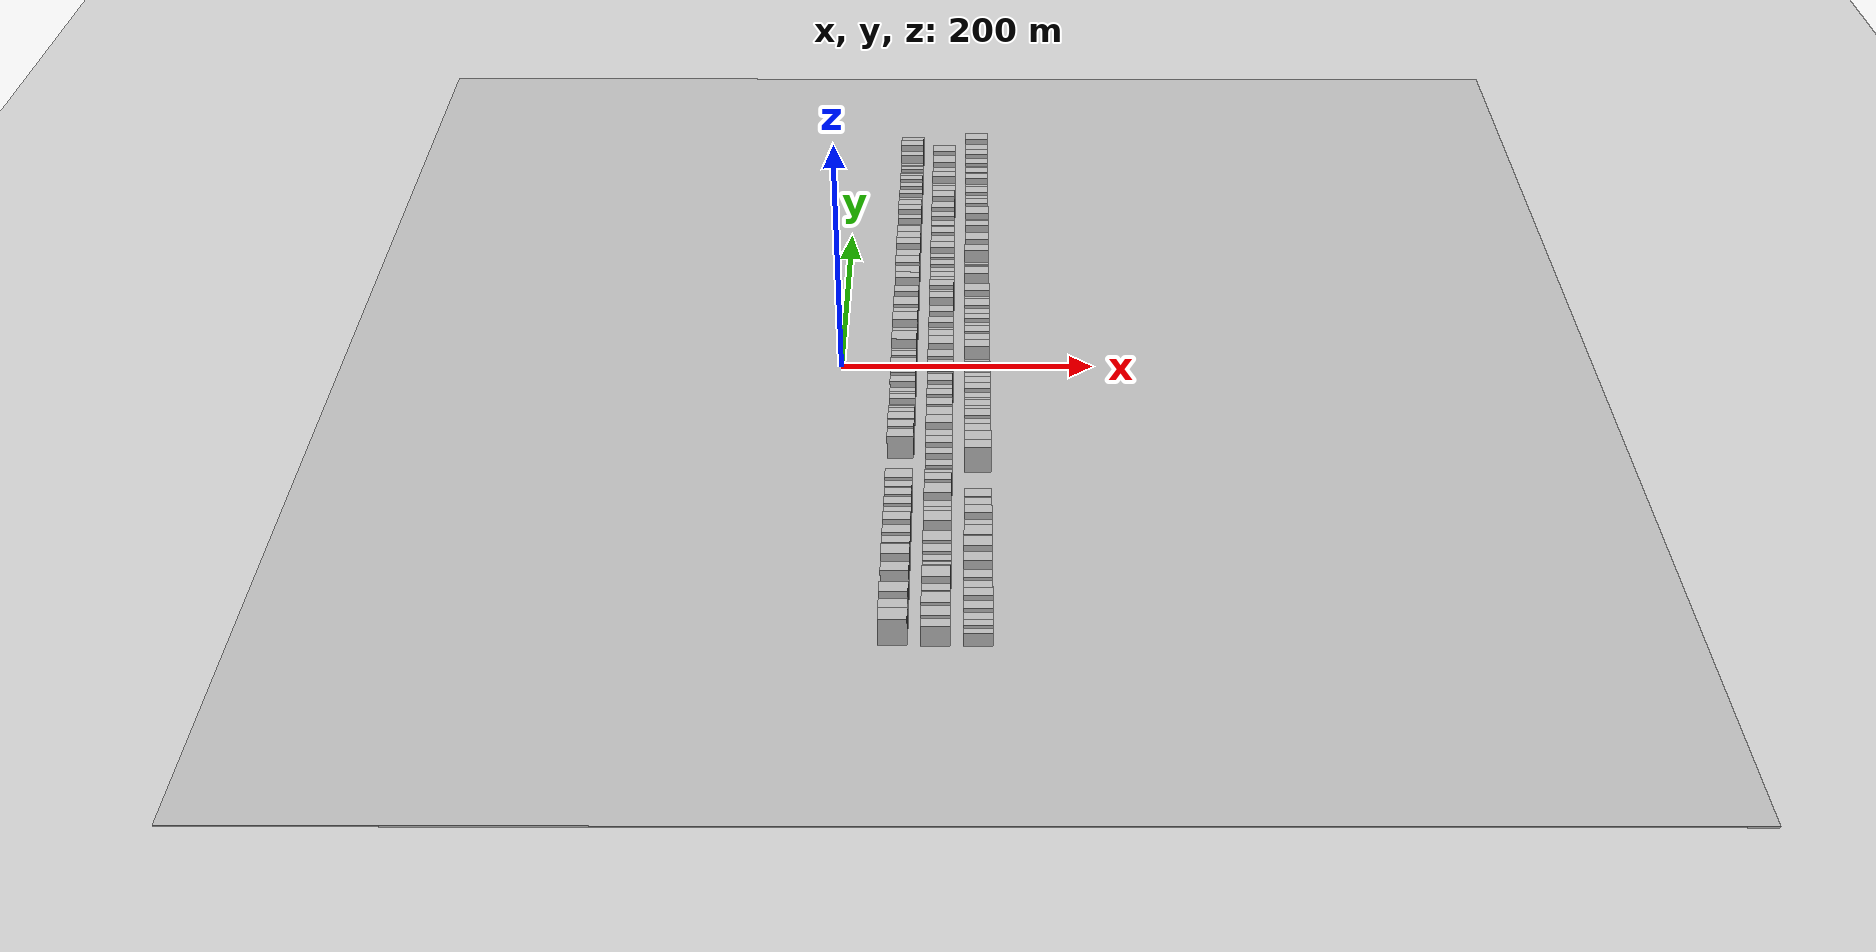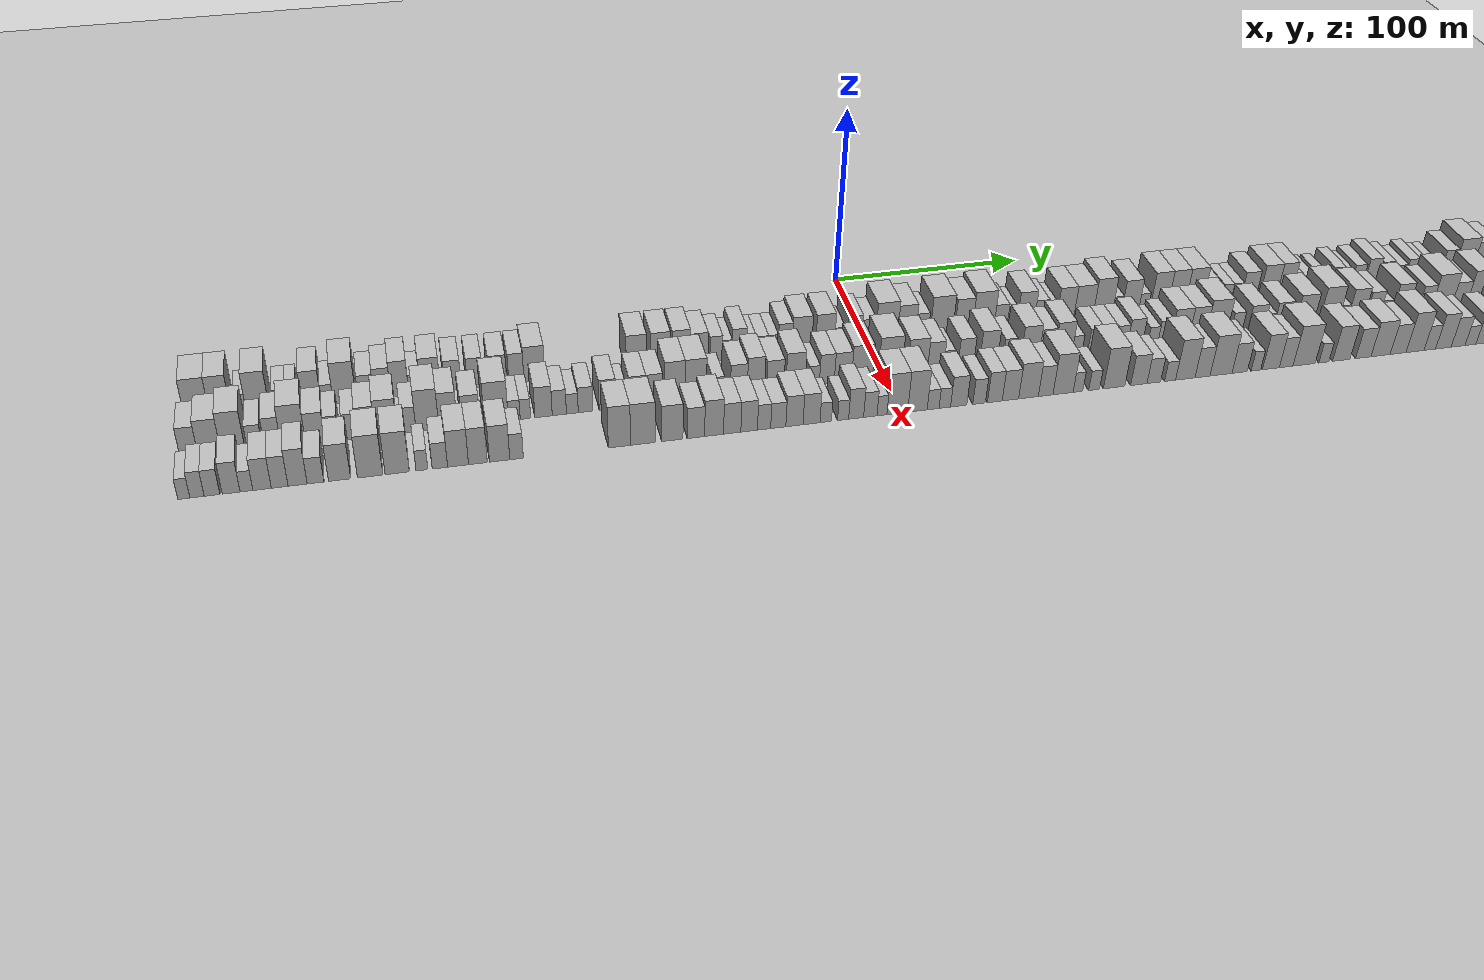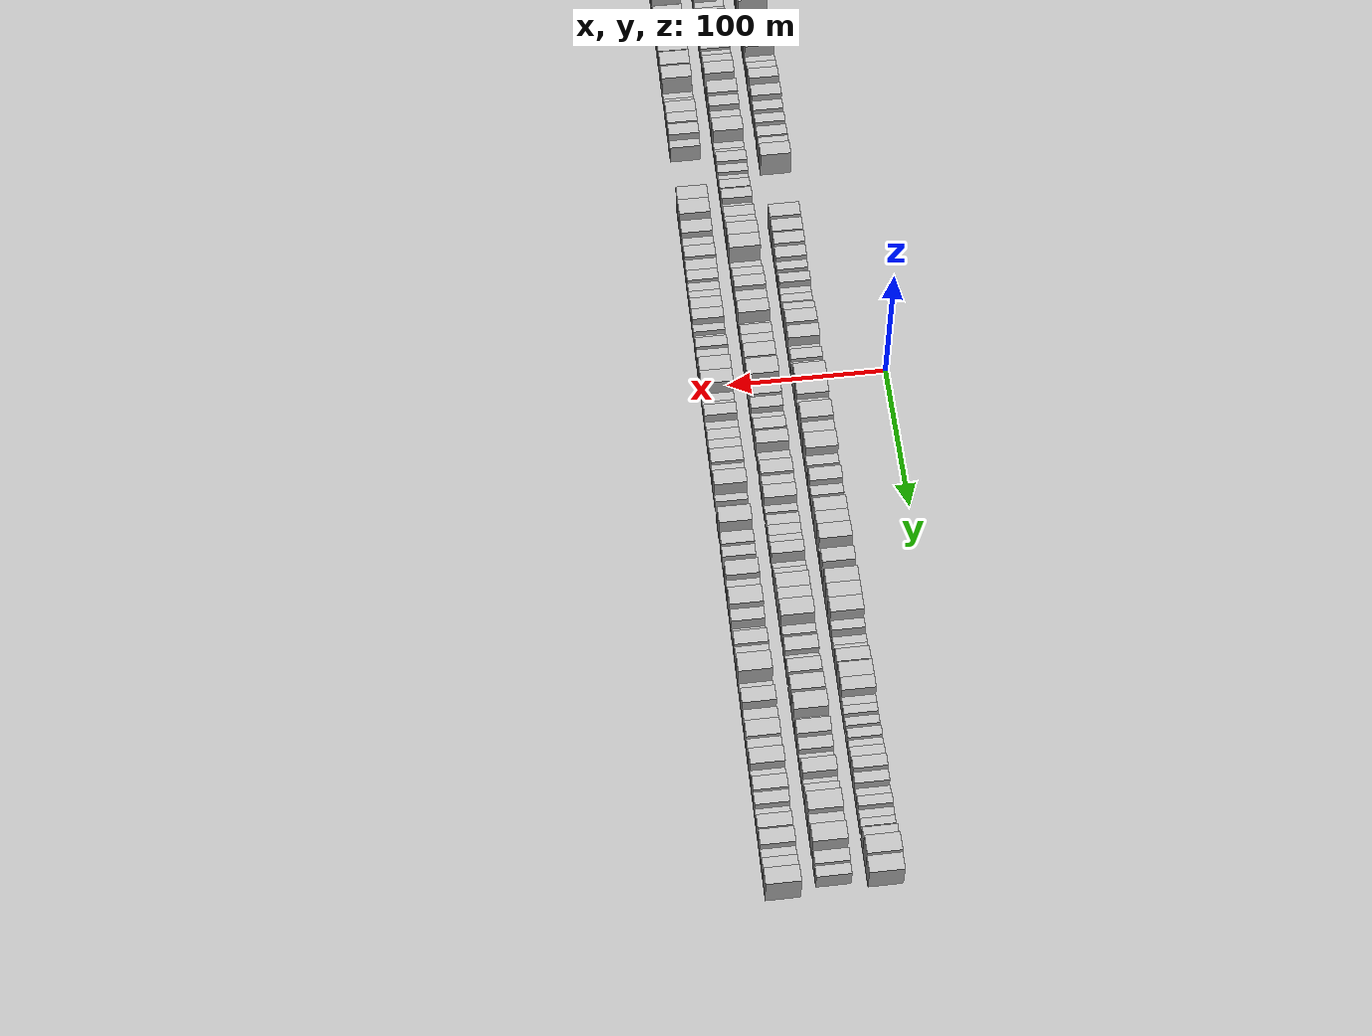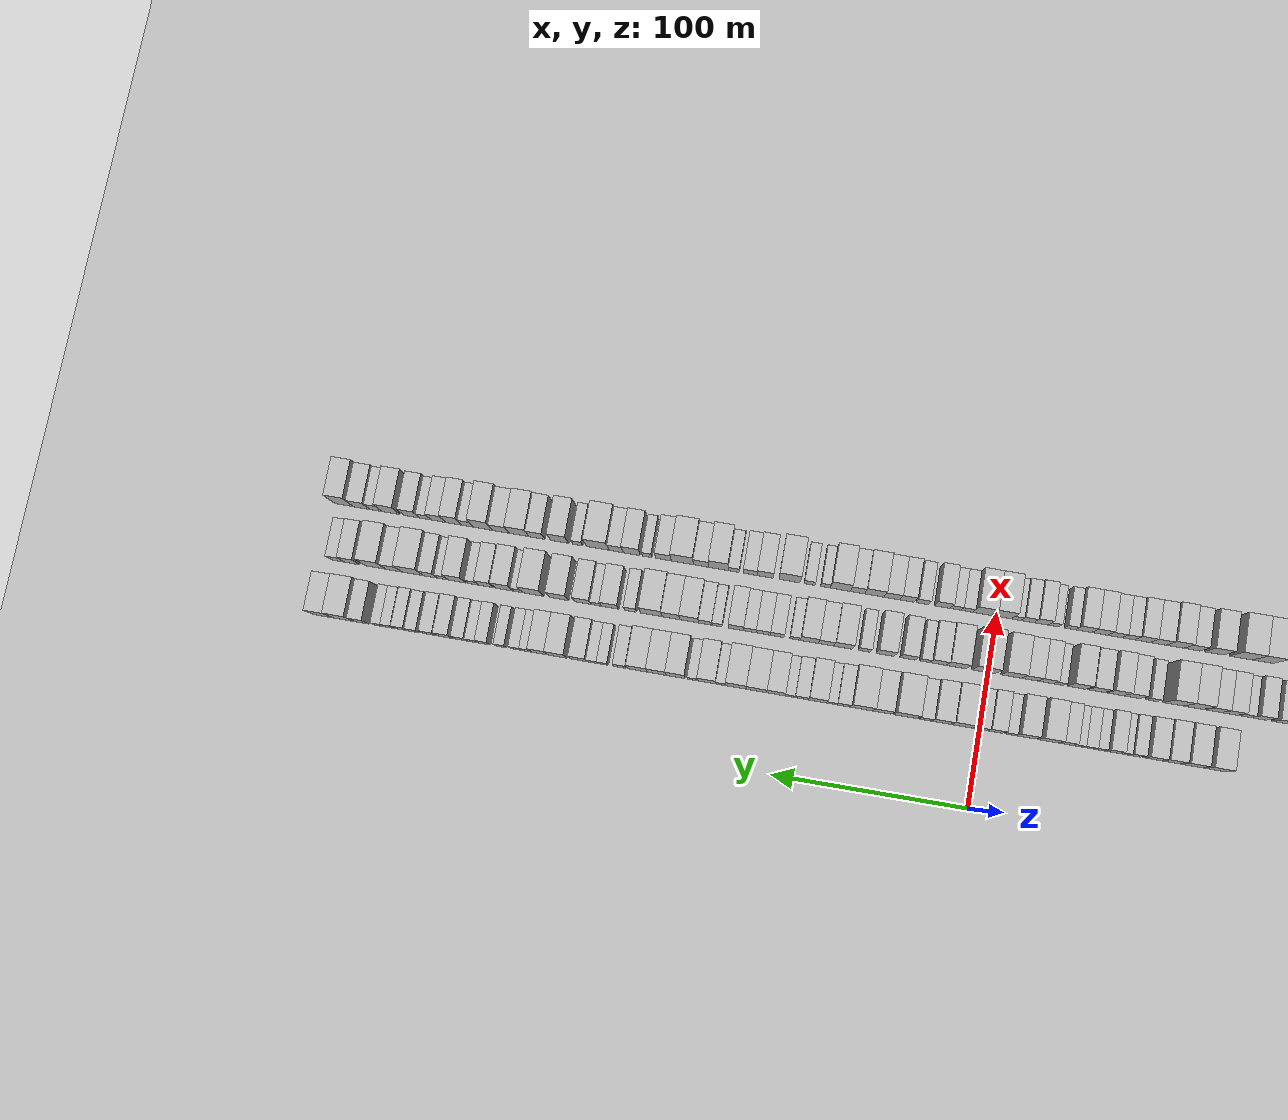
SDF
<?xml version="1.0" encoding="utf-8"?>

<sdf version="1.6">

   <world name="default">

      <gui fullscreen="0">

         <camera name="user_camera">

            <pose>-15 0 4.57585 0 0 0</pose>

            <view_controller>orbit</view_controller>

         </camera>

      </gui>

      <scene>

         <sky>

           <clouds>

             <speed>12</speed>

           </clouds>

         </sky>

         <ambient>0.4 0.4 0.4 1</ambient>

         <background>0.7 0.7 0.7 1</background>

         <shadows>1</shadows>

      </scene>

      <gravity>0 0 -9.8066</gravity>

      <magnetic_field>6e-06 2.3e-05 -4.2e-05</magnetic_field>

      <physics default="0" name="default_physics" type="ode">

         <ode>

            <solver>

               <type>quick</type>

               <iters>10</iters>

               <sor>1.0</sor>

               <use_dynamic_moi_rescaling>0</use_dynamic_moi_rescaling>

            </solver>

            <constraints>

               <cfm>0</cfm>

               <erp>0.2</erp>

               <contact_max_correcting_vel>100</contact_max_correcting_vel>

               <contact_surface_layer>0.001</contact_surface_layer>

            </constraints>

         </ode>

         <max_step_size>0.004</max_step_size>

         <real_time_factor>1</real_time_factor>

         <real_time_update_rate>250</real_time_update_rate>

      </physics>

      <light name="sun" type="directional">

         <cast_shadows>1</cast_shadows>

         <pose>0 0 10 0 0 0</pose>

         <diffuse>0.8 0.8 0.8 1</diffuse>

         <specular>0.2 0.2 0.2 1</specular>

         <attenuation>

            <range>1000</range>

            <constant>0.9</constant>

            <linear>0.01</linear>

            <quadratic>0.001</quadratic>

         </attenuation>

         <direction>-0.5 0.1 -0.9</direction>

      </light>

      <include>

         <name>ground_plane_1</name>

         <uri>model://HANNAS_ground_plane</uri>

         <pose>0 0 0  0 0 0</pose>

      </include>

      <include>

         <name>ground_plane_2</name>

         <uri>model://HANNAS_ground_plane</uri>

         <pose>100 0 0  0 0 0</pose>

      </include>

      <model name="building_1">

         <static>1</static>

         <pose frame="">50.0000 -328.2224 0 0.000000 0.000000 0.000000</pose>

         <link name="link">

            <pose frame="">0 0 12.00 0 0 0</pose>

            <collision name="collision">

               <geometry>

                  <box>

                     <size>20.0000 11.5552 24.0000</size>

                  </box>

               </geometry>

               <max_contacts>10</max_contacts>

               <surface>

                  <contact>

                     <ode/>

                  </contact>

                  <bounce/>

                  <friction>

                     <torsional>

                        <ode/>

                     </torsional>

                     <ode/>

                  </friction>

               </surface>

            </collision>

            <visual name="visual">

               <cast_shadows>0</cast_shadows>

               <geometry>

                  <box>

                     <size>20.0000 11.5552 24.0000</size>

                  </box>

               </geometry>

               <material>

                  <script>

                     <uri>model://HANNAS_wall/materials/scripts</uri>

                     <uri>model://HANNAS_wall/materials/textures</uri>

                     <name>vrc/HANNAS_wall</name>

                  </script>

               </material>

            </visual>

            <self_collide>0</self_collide>

            <enable_wind>0</enable_wind>

            <kinematic>0</kinematic>

         </link>

      </model>

      <model name="building_2">

         <static>1</static>

         <pose frame="">50.0000 -317.5008 0 0.000000 0.000000 0.000000</pose>

         <link name="link">

            <pose frame="">0 0 12.00 0 0 0</pose>

            <collision name="collision">

               <geometry>

                  <box>

                     <size>20.0000 9.8880 24.0000</size>

                  </box>

               </geometry>

               <max_contacts>10</max_contacts>

               <surface>

                  <contact>

                     <ode/>

                  </contact>

                  <bounce/>

                  <friction>

                     <torsional>

                        <ode/>

                     </torsional>

                     <ode/>

                  </friction>

               </surface>

            </collision>

            <visual name="visual">

               <cast_shadows>0</cast_shadows>

               <geometry>

                  <box>

                     <size>20.0000 9.8880 24.0000</size>

                  </box>

               </geometry>

               <material>

                  <script>

                     <uri>model://HANNAS_wall/materials/scripts</uri>

                     <uri>model://HANNAS_wall/materials/textures</uri>

                     <name>vrc/HANNAS_wall</name>

                  </script>

               </material>

            </visual>

            <self_collide>0</self_collide>

            <enable_wind>0</enable_wind>

            <kinematic>0</kinematic>

         </link>

      </model>

      <model name="building_3">

         <static>1</static>

         <pose frame="">50.0000 -308.0317 0 0.000000 0.000000 0.000000</pose>

         <link name="link">

            <pose frame="">0 0 6.00 0 0 0</pose>

            <collision name="collision">

               <geometry>

                  <box>

                     <size>20.0000 5.0502 12.0000</size>

                  </box>

               </geometry>

               <max_contacts>10</max_contacts>

               <surface>

                  <contact>

                     <ode/>

                  </contact>

                  <bounce/>

                  <friction>

                     <torsional>

                        <ode/>

                     </torsional>

                     <ode/>

                  </friction>

               </surface>

            </collision>

            <visual name="visual">

               <cast_shadows>0</cast_shadows>

               <geometry>

                  <box>

                     <size>20.0000 5.0502 12.0000</size>

                  </box>

               </geometry>

               <material>

                  <script>

                     <uri>model://HANNAS_wall/materials/scripts</uri>

                     <uri>model://HANNAS_wall/materials/textures</uri>

                     <name>vrc/HANNAS_wall</name>

                  </script>

               </material>

            </visual>

            <self_collide>0</self_collide>

            <enable_wind>0</enable_wind>

            <kinematic>0</kinematic>

         </link>

      </model>

      <model name="building_4">

         <static>1</static>

         <pose frame="">50.0000 -300.1355 0 0.000000 0.000000 0.000000</pose>

         <link name="link">

            <pose frame="">0 0 12.00 0 0 0</pose>

            <collision name="collision">

               <geometry>

                  <box>

                     <size>20.0000 10.7421 24.0000</size>

                  </box>

               </geometry>

               <max_contacts>10</max_contacts>

               <surface>

                  <contact>

                     <ode/>

                  </contact>

                  <bounce/>

                  <friction>

                     <torsional>

                        <ode/>

                     </torsional>

                     <ode/>

                  </friction>

               </surface>

            </collision>

            <visual name="visual">

               <cast_shadows>0</cast_shadows>

               <geometry>

                  <box>

                     <size>20.0000 10.7421 24.0000</size>

                  </box>

               </geometry>

               <material>

                  <script>

                     <uri>model://HANNAS_wall/materials/scripts</uri>

                     <uri>model://HANNAS_wall/materials/textures</uri>

                     <name>vrc/HANNAS_wall</name>

                  </script>

               </material>

            </visual>

            <self_collide>0</self_collide>

            <enable_wind>0</enable_wind>

            <kinematic>0</kinematic>

         </link>

      </model>

      <model name="building_5">

         <static>1</static>

         <pose frame="">50.0000 -289.7692 0 0.000000 0.000000 0.000000</pose>

         <link name="link">

            <pose frame="">0 0 6.00 0 0 0</pose>

            <collision name="collision">

               <geometry>

                  <box>

                     <size>20.0000 5.9904 12.0000</size>

                  </box>

               </geometry>

               <max_contacts>10</max_contacts>

               <surface>

                  <contact>

                     <ode/>

                  </contact>

                  <bounce/>

                  <friction>

                     <torsional>

                        <ode/>

                     </torsional>

                     <ode/>

                  </friction>

               </surface>

            </collision>

            <visual name="visual">

               <cast_shadows>0</cast_shadows>

               <geometry>

                  <box>

                     <size>20.0000 5.9904 12.0000</size>

                  </box>

               </geometry>

               <material>

                  <script>

                     <uri>model://HANNAS_wall/materials/scripts</uri>

                     <uri>model://HANNAS_wall/materials/textures</uri>

                     <name>vrc/HANNAS_wall</name>

                  </script>

               </material>

            </visual>

            <self_collide>0</self_collide>

            <enable_wind>0</enable_wind>

            <kinematic>0</kinematic>

         </link>

      </model>

      <model name="building_6">

         <static>1</static>

         <pose frame="">50.0000 -284.1062 0 0.000000 0.000000 0.000000</pose>

         <link name="link">

            <pose frame="">0 0 6.00 0 0 0</pose>

            <collision name="collision">

               <geometry>

                  <box>

                     <size>20.0000 5.3357 12.0000</size>

                  </box>

               </geometry>

               <max_contacts>10</max_contacts>

               <surface>

                  <contact>

                     <ode/>

                  </contact>

                  <bounce/>

                  <friction>

                     <torsional>

                        <ode/>

                     </torsional>

                     <ode/>

                  </friction>

               </surface>

            </collision>

            <visual name="visual">

               <cast_shadows>0</cast_shadows>

               <geometry>

                  <box>

                     <size>20.0000 5.3357 12.0000</size>

                  </box>

               </geometry>

               <material>

                  <script>

                     <uri>model://HANNAS_wall/materials/scripts</uri>

                     <uri>model://HANNAS_wall/materials/textures</uri>

                     <name>vrc/HANNAS_wall</name>

                  </script>

               </material>

            </visual>

            <self_collide>0</self_collide>

            <enable_wind>0</enable_wind>

            <kinematic>0</kinematic>

         </link>

      </model>

      <model name="building_7">

         <static>1</static>

         <pose frame="">50.0000 -274.8928 0 0.000000 0.000000 0.000000</pose>

         <link name="link">

            <pose frame="">0 0 10.50 0 0 0</pose>

            <collision name="collision">

               <geometry>

                  <box>

                     <size>20.0000 9.0911 21.0000</size>

                  </box>

               </geometry>

               <max_contacts>10</max_contacts>

               <surface>

                  <contact>

                     <ode/>

                  </contact>

                  <bounce/>

                  <friction>

                     <torsional>

                        <ode/>

                     </torsional>

                     <ode/>

                  </friction>

               </surface>

            </collision>

            <visual name="visual">

               <cast_shadows>0</cast_shadows>

               <geometry>

                  <box>

                     <size>20.0000 9.0911 21.0000</size>

                  </box>

               </geometry>

               <material>

                  <script>

                     <uri>model://HANNAS_wall/materials/scripts</uri>

                     <uri>model://HANNAS_wall/materials/textures</uri>

                     <name>vrc/HANNAS_wall</name>

                  </script>

               </material>

            </visual>

            <self_collide>0</self_collide>

            <enable_wind>0</enable_wind>

            <kinematic>0</kinematic>

         </link>

      </model>

      <model name="building_8">

         <static>1</static>

         <pose frame="">50.0000 -267.5456 0 0.000000 0.000000 0.000000</pose>

         <link name="link">

            <pose frame="">0 0 6.00 0 0 0</pose>

            <collision name="collision">

               <geometry>

                  <box>

                     <size>20.0000 5.6033 12.0000</size>

                  </box>

               </geometry>

               <max_contacts>10</max_contacts>

               <surface>

                  <contact>

                     <ode/>

                  </contact>

                  <bounce/>

                  <friction>

                     <torsional>

                        <ode/>

                     </torsional>

                     <ode/>

                  </friction>

               </surface>

            </collision>

            <visual name="visual">

               <cast_shadows>0</cast_shadows>

               <geometry>

                  <box>

                     <size>20.0000 5.6033 12.0000</size>

                  </box>

               </geometry>

               <material>

                  <script>

                     <uri>model://HANNAS_wall/materials/scripts</uri>

                     <uri>model://HANNAS_wall/materials/textures</uri>

                     <name>vrc/HANNAS_wall</name>

                  </script>

               </material>

            </visual>

            <self_collide>0</self_collide>

            <enable_wind>0</enable_wind>

            <kinematic>0</kinematic>

         </link>

      </model>

      <model name="building_9">

         <static>1</static>

         <pose frame="">50.0000 -259.3172 0 0.000000 0.000000 0.000000</pose>

         <link name="link">

            <pose frame="">0 0 12.00 0 0 0</pose>

            <collision name="collision">

               <geometry>

                  <box>

                     <size>20.0000 10.8535 24.0000</size>

                  </box>

               </geometry>

               <max_contacts>10</max_contacts>

               <surface>

                  <contact>

                     <ode/>

                  </contact>

                  <bounce/>

                  <friction>

                     <torsional>

                        <ode/>

                     </torsional>

                     <ode/>

                  </friction>

               </surface>

            </collision>

            <visual name="visual">

               <cast_shadows>0</cast_shadows>

               <geometry>

                  <box>

                     <size>20.0000 10.8535 24.0000</size>

                  </box>

               </geometry>

               <material>

                  <script>

                     <uri>model://HANNAS_wall/materials/scripts</uri>

                     <uri>model://HANNAS_wall/materials/textures</uri>

                     <name>vrc/HANNAS_wall</name>

                  </script>

               </material>

            </visual>

            <self_collide>0</self_collide>

            <enable_wind>0</enable_wind>

            <kinematic>0</kinematic>

         </link>

      </model>

      <model name="building_10">

         <static>1</static>

         <pose frame="">50.0000 -249.1697 0 0.000000 0.000000 0.000000</pose>

         <link name="link">

            <pose frame="">0 0 7.50 0 0 0</pose>

            <collision name="collision">

               <geometry>

                  <box>

                     <size>20.0000 7.4414 15.0000</size>

                  </box>

               </geometry>

               <max_contacts>10</max_contacts>

               <surface>

                  <contact>

                     <ode/>

                  </contact>

                  <bounce/>

                  <friction>

                     <torsional>

                        <ode/>

                     </torsional>

                     <ode/>

                  </friction>

               </surface>

            </collision>

            <visual name="visual">

               <cast_shadows>0</cast_shadows>

               <geometry>

                  <box>

                     <size>20.0000 7.4414 15.0000</size>

                  </box>

               </geometry>

               <material>

                  <script>

                     <uri>model://HANNAS_wall/materials/scripts</uri>

                     <uri>model://HANNAS_wall/materials/textures</uri>

                     <name>vrc/HANNAS_wall</name>

                  </script>

               </material>

            </visual>

            <self_collide>0</self_collide>

            <enable_wind>0</enable_wind>

            <kinematic>0</kinematic>

         </link>

      </model>

      <model name="building_11">

         <static>1</static>

         <pose frame="">50.0000 -241.4162 0 0.000000 0.000000 0.000000</pose>

         <link name="link">

            <pose frame="">0 0 9.00 0 0 0</pose>

            <collision name="collision">

               <geometry>

                  <box>

                     <size>20.0000 8.0657 18.0000</size>

                  </box>

               </geometry>

               <max_contacts>10</max_contacts>

               <surface>

                  <contact>

                     <ode/>

                  </contact>

                  <bounce/>

                  <friction>

                     <torsional>

                        <ode/>

                     </torsional>

                     <ode/>

                  </friction>

               </surface>

            </collision>

            <visual name="visual">

               <cast_shadows>0</cast_shadows>

               <geometry>

                  <box>

                     <size>20.0000 8.0657 18.0000</size>

                  </box>

               </geometry>

               <material>

                  <script>

                     <uri>model://HANNAS_wall/materials/scripts</uri>

                     <uri>model://HANNAS_wall/materials/textures</uri>

                     <name>vrc/HANNAS_wall</name>

                  </script>

               </material>

            </visual>

            <self_collide>0</self_collide>

            <enable_wind>0</enable_wind>

            <kinematic>0</kinematic>

         </link>

      </model>

      <model name="building_12">

         <static>1</static>

         <pose frame="">50.0000 -233.1106 0 0.000000 0.000000 0.000000</pose>

         <link name="link">

            <pose frame="">0 0 10.50 0 0 0</pose>

            <collision name="collision">

               <geometry>

                  <box>

                     <size>20.0000 8.5455 21.0000</size>

                  </box>

               </geometry>

               <max_contacts>10</max_contacts>

               <surface>

                  <contact>

                     <ode/>

                  </contact>

                  <bounce/>

                  <friction>

                     <torsional>

                        <ode/>

                     </torsional>

                     <ode/>

                  </friction>

               </surface>

            </collision>

            <visual name="visual">

               <cast_shadows>0</cast_shadows>

               <geometry>

                  <box>

                     <size>20.0000 8.5455 21.0000</size>

                  </box>

               </geometry>

               <material>

                  <script>

                     <uri>model://HANNAS_wall/materials/scripts</uri>

                     <uri>model://HANNAS_wall/materials/textures</uri>

                     <name>vrc/HANNAS_wall</name>

                  </script>

               </material>

            </visual>

            <self_collide>0</self_collide>

            <enable_wind>0</enable_wind>

            <kinematic>0</kinematic>

         </link>

      </model>

      <model name="building_13">

         <static>1</static>

         <pose frame="">50.0000 -226.0542 0 0.000000 0.000000 0.000000</pose>

         <link name="link">

            <pose frame="">0 0 6.00 0 0 0</pose>

            <collision name="collision">

               <geometry>

                  <box>

                     <size>20.0000 5.5673 12.0000</size>

                  </box>

               </geometry>

               <max_contacts>10</max_contacts>

               <surface>

                  <contact>

                     <ode/>

                  </contact>

                  <bounce/>

                  <friction>

                     <torsional>

                        <ode/>

                     </torsional>

                     <ode/>

                  </friction>

               </surface>

            </collision>

            <visual name="visual">

               <cast_shadows>0</cast_shadows>

               <geometry>

                  <box>

                     <size>20.0000 5.5673 12.0000</size>

                  </box>

               </geometry>

               <material>

                  <script>

                     <uri>model://HANNAS_wall/materials/scripts</uri>

                     <uri>model://HANNAS_wall/materials/textures</uri>

                     <name>vrc/HANNAS_wall</name>

                  </script>

               </material>

            </visual>

            <self_collide>0</self_collide>

            <enable_wind>0</enable_wind>

            <kinematic>0</kinematic>

         </link>

      </model>

      <model name="building_14">

         <static>1</static>

         <pose frame="">50.0000 -218.4649 0 0.000000 0.000000 0.000000</pose>

         <link name="link">

            <pose frame="">0 0 10.50 0 0 0</pose>

            <collision name="collision">

               <geometry>

                  <box>

                     <size>20.0000 9.6113 21.0000</size>

                  </box>

               </geometry>

               <max_contacts>10</max_contacts>

               <surface>

                  <contact>

                     <ode/>

                  </contact>

                  <bounce/>

                  <friction>

                     <torsional>

                        <ode/>

                     </torsional>

                     <ode/>

                  </friction>

               </surface>

            </collision>

            <visual name="visual">

               <cast_shadows>0</cast_shadows>

               <geometry>

                  <box>

                     <size>20.0000 9.6113 21.0000</size>

                  </box>

               </geometry>

               <material>

                  <script>

                     <uri>model://HANNAS_wall/materials/scripts</uri>

                     <uri>model://HANNAS_wall/materials/textures</uri>

                     <name>vrc/HANNAS_wall</name>

                  </script>

               </material>

            </visual>

            <self_collide>0</self_collide>

            <enable_wind>0</enable_wind>

            <kinematic>0</kinematic>

         </link>

      </model>

      <model name="building_15">

         <static>1</static>

         <pose frame="">50.0000 -207.6624 0 0.000000 0.000000 0.000000</pose>

         <link name="link">

            <pose frame="">0 0 9.00 0 0 0</pose>

            <collision name="collision">

               <geometry>

                  <box>

                     <size>20.0000 7.9937 18.0000</size>

                  </box>

               </geometry>

               <max_contacts>10</max_contacts>

               <surface>

                  <contact>

                     <ode/>

                  </contact>

                  <bounce/>

                  <friction>

                     <torsional>

                        <ode/>

                     </torsional>

                     <ode/>

                  </friction>

               </surface>

            </collision>

            <visual name="visual">

               <cast_shadows>0</cast_shadows>

               <geometry>

                  <box>

                     <size>20.0000 7.9937 18.0000</size>

                  </box>

               </geometry>

               <material>

                  <script>

                     <uri>model://HANNAS_wall/materials/scripts</uri>

                     <uri>model://HANNAS_wall/materials/textures</uri>

                     <name>vrc/HANNAS_wall</name>

                  </script>

               </material>

            </visual>

            <self_collide>0</self_collide>

            <enable_wind>0</enable_wind>

            <kinematic>0</kinematic>

         </link>

      </model>

      <model name="building_16">

         <static>1</static>

         <pose frame="">50.0000 -196.8680 0 0.000000 0.000000 0.000000</pose>

         <link name="link">

            <pose frame="">0 0 9.00 0 0 0</pose>

            <collision name="collision">

               <geometry>

                  <box>

                     <size>20.0000 7.5952 18.0000</size>

                  </box>

               </geometry>

               <max_contacts>10</max_contacts>

               <surface>

                  <contact>

                     <ode/>

                  </contact>

                  <bounce/>

                  <friction>

                     <torsional>

                        <ode/>

                     </torsional>

                     <ode/>

                  </friction>

               </surface>

            </collision>

            <visual name="visual">

               <cast_shadows>0</cast_shadows>

               <geometry>

                  <box>

                     <size>20.0000 7.5952 18.0000</size>

                  </box>

               </geometry>

               <material>

                  <script>

                     <uri>model://HANNAS_wall/materials/scripts</uri>

                     <uri>model://HANNAS_wall/materials/textures</uri>

                     <name>vrc/HANNAS_wall</name>

                  </script>

               </material>

            </visual>

            <self_collide>0</self_collide>

            <enable_wind>0</enable_wind>

            <kinematic>0</kinematic>

         </link>

      </model>

      <model name="building_17">

         <static>1</static>

         <pose frame="">50.0000 -185.8520 0 0.000000 0.000000 0.000000</pose>

         <link name="link">

            <pose frame="">0 0 9.00 0 0 0</pose>

            <collision name="collision">

               <geometry>

                  <box>

                     <size>20.0000 8.4368 18.0000</size>

                  </box>

               </geometry>

               <max_contacts>10</max_contacts>

               <surface>

                  <contact>

                     <ode/>

                  </contact>

                  <bounce/>

                  <friction>

                     <torsional>

                        <ode/>

                     </torsional>

                     <ode/>

                  </friction>

               </surface>

            </collision>

            <visual name="visual">

               <cast_shadows>0</cast_shadows>

               <geometry>

                  <box>

                     <size>20.0000 8.4368 18.0000</size>

                  </box>

               </geometry>

               <material>

                  <script>

                     <uri>model://HANNAS_wall/materials/scripts</uri>

                     <uri>model://HANNAS_wall/materials/textures</uri>

                     <name>vrc/HANNAS_wall</name>

                  </script>

               </material>

            </visual>

            <self_collide>0</self_collide>

            <enable_wind>0</enable_wind>

            <kinematic>0</kinematic>

         </link>

      </model>

      <model name="building_18">

         <static>1</static>

         <pose frame="">50.0000 -176.9500 0 0.000000 0.000000 0.000000</pose>

         <link name="link">

            <pose frame="">0 0 9.00 0 0 0</pose>

            <collision name="collision">

               <geometry>

                  <box>

                     <size>20.0000 7.3672 18.0000</size>

                  </box>

               </geometry>

               <max_contacts>10</max_contacts>

               <surface>

                  <contact>

                     <ode/>

                  </contact>

                  <bounce/>

                  <friction>

                     <torsional>

                        <ode/>

                     </torsional>

                     <ode/>

                  </friction>

               </surface>

            </collision>

            <visual name="visual">

               <cast_shadows>0</cast_shadows>

               <geometry>

                  <box>

                     <size>20.0000 7.3672 18.0000</size>

                  </box>

               </geometry>

               <material>

                  <script>

                     <uri>model://HANNAS_wall/materials/scripts</uri>

                     <uri>model://HANNAS_wall/materials/textures</uri>

                     <name>vrc/HANNAS_wall</name>

                  </script>

               </material>

            </visual>

            <self_collide>0</self_collide>

            <enable_wind>0</enable_wind>

            <kinematic>0</kinematic>

         </link>

      </model>

      <model name="building_19">

         <static>1</static>

         <pose frame="">50.0000 -168.1503 0 0.000000 0.000000 0.000000</pose>

         <link name="link">

            <pose frame="">0 0 10.50 0 0 0</pose>

            <collision name="collision">

               <geometry>

                  <box>

                     <size>20.0000 10.2322 21.0000</size>

                  </box>

               </geometry>

               <max_contacts>10</max_contacts>

               <surface>

                  <contact>

                     <ode/>

                  </contact>

                  <bounce/>

                  <friction>

                     <torsional>

                        <ode/>

                     </torsional>

                     <ode/>

                  </friction>

               </surface>

            </collision>

            <visual name="visual">

               <cast_shadows>0</cast_shadows>

               <geometry>

                  <box>

                     <size>20.0000 10.2322 21.0000</size>

                  </box>

               </geometry>

               <material>

                  <script>

                     <uri>model://HANNAS_wall/materials/scripts</uri>

                     <uri>model://HANNAS_wall/materials/textures</uri>

                     <name>vrc/HANNAS_wall</name>

                  </script>

               </material>

            </visual>

            <self_collide>0</self_collide>

            <enable_wind>0</enable_wind>

            <kinematic>0</kinematic>

         </link>

      </model>

      <model name="building_20">

         <static>1</static>

         <pose frame="">50.0000 -117.7029 0 0.000000 0.000000 0.000000</pose>

         <link name="link">

            <pose frame="">0 0 10.50 0 0 0</pose>

            <collision name="collision">

               <geometry>

                  <box>

                     <size>20.0000 10.2209 21.0000</size>

                  </box>

               </geometry>

               <max_contacts>10</max_contacts>

               <surface>

                  <contact>

                     <ode/>

                  </contact>

                  <bounce/>

                  <friction>

                     <torsional>

                        <ode/>

                     </torsional>

                     <ode/>

                  </friction>

               </surface>

            </collision>

            <visual name="visual">

               <cast_shadows>0</cast_shadows>

               <geometry>

                  <box>

                     <size>20.0000 10.2209 21.0000</size>

                  </box>

               </geometry>

               <material>

                  <script>

                     <uri>model://HANNAS_wall/materials/scripts</uri>

                     <uri>model://HANNAS_wall/materials/textures</uri>

                     <name>vrc/HANNAS_wall</name>

                  </script>

               </material>

            </visual>

            <self_collide>0</self_collide>

            <enable_wind>0</enable_wind>

            <kinematic>0</kinematic>

         </link>

      </model>

      <model name="building_21">

         <static>1</static>

         <pose frame="">50.0000 -105.7209 0 0.000000 0.000000 0.000000</pose>

         <link name="link">

            <pose frame="">0 0 10.50 0 0 0</pose>

            <collision name="collision">

               <geometry>

                  <box>

                     <size>20.0000 9.7430 21.0000</size>

                  </box>

               </geometry>

               <max_contacts>10</max_contacts>

               <surface>

                  <contact>

                     <ode/>

                  </contact>

                  <bounce/>

                  <friction>

                     <torsional>

                        <ode/>

                     </torsional>

                     <ode/>

                  </friction>

               </surface>

            </collision>

            <visual name="visual">

               <cast_shadows>0</cast_shadows>

               <geometry>

                  <box>

                     <size>20.0000 9.7430 21.0000</size>

                  </box>

               </geometry>

               <material>

                  <script>

                     <uri>model://HANNAS_wall/materials/scripts</uri>

                     <uri>model://HANNAS_wall/materials/textures</uri>

                     <name>vrc/HANNAS_wall</name>

                  </script>

               </material>

            </visual>

            <self_collide>0</self_collide>

            <enable_wind>0</enable_wind>

            <kinematic>0</kinematic>

         </link>

      </model>

      <model name="building_22">

         <static>1</static>

         <pose frame="">50.0000 -95.3315 0 0.000000 0.000000 0.000000</pose>

         <link name="link">

            <pose frame="">0 0 10.50 0 0 0</pose>

            <collision name="collision">

               <geometry>

                  <box>

                     <size>20.0000 9.0359 21.0000</size>

                  </box>

               </geometry>

               <max_contacts>10</max_contacts>

               <surface>

                  <contact>

                     <ode/>

                  </contact>

                  <bounce/>

                  <friction>

                     <torsional>

                        <ode/>

                     </torsional>

                     <ode/>

                  </friction>

               </surface>

            </collision>

            <visual name="visual">

               <cast_shadows>0</cast_shadows>

               <geometry>

                  <box>

                     <size>20.0000 9.0359 21.0000</size>

                  </box>

               </geometry>

               <material>

                  <script>

                     <uri>model://HANNAS_wall/materials/scripts</uri>

                     <uri>model://HANNAS_wall/materials/textures</uri>

                     <name>vrc/HANNAS_wall</name>

                  </script>

               </material>

            </visual>

            <self_collide>0</self_collide>

            <enable_wind>0</enable_wind>

            <kinematic>0</kinematic>

         </link>

      </model>

      <model name="building_23">

         <static>1</static>

         <pose frame="">50.0000 -86.3866 0 0.000000 0.000000 0.000000</pose>

         <link name="link">

            <pose frame="">0 0 9.00 0 0 0</pose>

            <collision name="collision">

               <geometry>

                  <box>

                     <size>20.0000 8.8540 18.0000</size>

                  </box>

               </geometry>

               <max_contacts>10</max_contacts>

               <surface>

                  <contact>

                     <ode/>

                  </contact>

                  <bounce/>

                  <friction>

                     <torsional>

                        <ode/>

                     </torsional>

                     <ode/>

                  </friction>

               </surface>

            </collision>

            <visual name="visual">

               <cast_shadows>0</cast_shadows>

               <geometry>

                  <box>

                     <size>20.0000 8.8540 18.0000</size>

                  </box>

               </geometry>

               <material>

                  <script>

                     <uri>model://HANNAS_wall/materials/scripts</uri>

                     <uri>model://HANNAS_wall/materials/textures</uri>

                     <name>vrc/HANNAS_wall</name>

                  </script>

               </material>

            </visual>

            <self_collide>0</self_collide>

            <enable_wind>0</enable_wind>

            <kinematic>0</kinematic>

         </link>

      </model>

      <model name="building_24">

         <static>1</static>

         <pose frame="">50.0000 -77.7692 0 0.000000 0.000000 0.000000</pose>

         <link name="link">

            <pose frame="">0 0 7.50 0 0 0</pose>

            <collision name="collision">

               <geometry>

                  <box>

                     <size>20.0000 6.3808 15.0000</size>

                  </box>

               </geometry>

               <max_contacts>10</max_contacts>

               <surface>

                  <contact>

                     <ode/>

                  </contact>

                  <bounce/>

                  <friction>

                     <torsional>

                        <ode/>

                     </torsional>

                     <ode/>

                  </friction>

               </surface>

            </collision>

            <visual name="visual">

               <cast_shadows>0</cast_shadows>

               <geometry>

                  <box>

                     <size>20.0000 6.3808 15.0000</size>

                  </box>

               </geometry>

               <material>

                  <script>

                     <uri>model://HANNAS_wall/materials/scripts</uri>

                     <uri>model://HANNAS_wall/materials/textures</uri>

                     <name>vrc/HANNAS_wall</name>

                  </script>

               </material>

            </visual>

            <self_collide>0</self_collide>

            <enable_wind>0</enable_wind>

            <kinematic>0</kinematic>

         </link>

      </model>

      <model name="building_25">

         <static>1</static>

         <pose frame="">50.0000 -72.1484 0 0.000000 0.000000 0.000000</pose>

         <link name="link">

            <pose frame="">0 0 6.00 0 0 0</pose>

            <collision name="collision">

               <geometry>

                  <box>

                     <size>20.0000 4.8608 12.0000</size>

                  </box>

               </geometry>

               <max_contacts>10</max_contacts>

               <surface>

                  <contact>

                     <ode/>

                  </contact>

                  <bounce/>

                  <friction>

                     <torsional>

                        <ode/>

                     </torsional>

                     <ode/>

                  </friction>

               </surface>

            </collision>

            <visual name="visual">

               <cast_shadows>0</cast_shadows>

               <geometry>

                  <box>

                     <size>20.0000 4.8608 12.0000</size>

                  </box>

               </geometry>

               <material>

                  <script>

                     <uri>model://HANNAS_wall/materials/scripts</uri>

                     <uri>model://HANNAS_wall/materials/textures</uri>

                     <name>vrc/HANNAS_wall</name>

                  </script>

               </material>

            </visual>

            <self_collide>0</self_collide>

            <enable_wind>0</enable_wind>

            <kinematic>0</kinematic>

         </link>

      </model>

      <model name="building_26">

         <static>1</static>

         <pose frame="">50.0000 -66.0389 0 0.000000 0.000000 0.000000</pose>

         <link name="link">

            <pose frame="">0 0 9.00 0 0 0</pose>

            <collision name="collision">

               <geometry>

                  <box>

                     <size>20.0000 7.3583 18.0000</size>

                  </box>

               </geometry>

               <max_contacts>10</max_contacts>

               <surface>

                  <contact>

                     <ode/>

                  </contact>

                  <bounce/>

                  <friction>

                     <torsional>

                        <ode/>

                     </torsional>

                     <ode/>

                  </friction>

               </surface>

            </collision>

            <visual name="visual">

               <cast_shadows>0</cast_shadows>

               <geometry>

                  <box>

                     <size>20.0000 7.3583 18.0000</size>

                  </box>

               </geometry>

               <material>

                  <script>

                     <uri>model://HANNAS_wall/materials/scripts</uri>

                     <uri>model://HANNAS_wall/materials/textures</uri>

                     <name>vrc/HANNAS_wall</name>

                  </script>

               </material>

            </visual>

            <self_collide>0</self_collide>

            <enable_wind>0</enable_wind>

            <kinematic>0</kinematic>

         </link>

      </model>

      <model name="building_27">

         <static>1</static>

         <pose frame="">50.0000 -59.8651 0 0.000000 0.000000 0.000000</pose>

         <link name="link">

            <pose frame="">0 0 6.00 0 0 0</pose>

            <collision name="collision">

               <geometry>

                  <box>

                     <size>20.0000 4.9893 12.0000</size>

                  </box>

               </geometry>

               <max_contacts>10</max_contacts>

               <surface>

                  <contact>

                     <ode/>

                  </contact>

                  <bounce/>

                  <friction>

                     <torsional>

                        <ode/>

                     </torsional>

                     <ode/>

                  </friction>

               </surface>

            </collision>

            <visual name="visual">

               <cast_shadows>0</cast_shadows>

               <geometry>

                  <box>

                     <size>20.0000 4.9893 12.0000</size>

                  </box>

               </geometry>

               <material>

                  <script>

                     <uri>model://HANNAS_wall/materials/scripts</uri>

                     <uri>model://HANNAS_wall/materials/textures</uri>

                     <name>vrc/HANNAS_wall</name>

                  </script>

               </material>

            </visual>

            <self_collide>0</self_collide>

            <enable_wind>0</enable_wind>

            <kinematic>0</kinematic>

         </link>

      </model>

      <model name="building_28">

         <static>1</static>

         <pose frame="">50.0000 -54.3744 0 0.000000 0.000000 0.000000</pose>

         <link name="link">

            <pose frame="">0 0 6.00 0 0 0</pose>

            <collision name="collision">

               <geometry>

                  <box>

                     <size>20.0000 5.9921 12.0000</size>

                  </box>

               </geometry>

               <max_contacts>10</max_contacts>

               <surface>

                  <contact>

                     <ode/>

                  </contact>

                  <bounce/>

                  <friction>

                     <torsional>

                        <ode/>

                     </torsional>

                     <ode/>

                  </friction>

               </surface>

            </collision>

            <visual name="visual">

               <cast_shadows>0</cast_shadows>

               <geometry>

                  <box>

                     <size>20.0000 5.9921 12.0000</size>

                  </box>

               </geometry>

               <material>

                  <script>

                     <uri>model://HANNAS_wall/materials/scripts</uri>

                     <uri>model://HANNAS_wall/materials/textures</uri>

                     <name>vrc/HANNAS_wall</name>

                  </script>

               </material>

            </visual>

            <self_collide>0</self_collide>

            <enable_wind>0</enable_wind>

            <kinematic>0</kinematic>

         </link>

      </model>

      <model name="building_29">

         <static>1</static>

         <pose frame="">50.0000 -48.8814 0 0.000000 0.000000 0.000000</pose>

         <link name="link">

            <pose frame="">0 0 6.00 0 0 0</pose>

            <collision name="collision">

               <geometry>

                  <box>

                     <size>20.0000 4.9938 12.0000</size>

                  </box>

               </geometry>

               <max_contacts>10</max_contacts>

               <surface>

                  <contact>

                     <ode/>

                  </contact>

                  <bounce/>

                  <friction>

                     <torsional>

                        <ode/>

                     </torsional>

                     <ode/>

                  </friction>

               </surface>

            </collision>

            <visual name="visual">

               <cast_shadows>0</cast_shadows>

               <geometry>

                  <box>

                     <size>20.0000 4.9938 12.0000</size>

                  </box>

               </geometry>

               <material>

                  <script>

                     <uri>model://HANNAS_wall/materials/scripts</uri>

                     <uri>model://HANNAS_wall/materials/textures</uri>

                     <name>vrc/HANNAS_wall</name>

                  </script>

               </material>

            </visual>

            <self_collide>0</self_collide>

            <enable_wind>0</enable_wind>

            <kinematic>0</kinematic>

         </link>

      </model>

      <model name="building_30">

         <static>1</static>

         <pose frame="">50.0000 -42.7141 0 0.000000 0.000000 0.000000</pose>

         <link name="link">

            <pose frame="">0 0 9.00 0 0 0</pose>

            <collision name="collision">

               <geometry>

                  <box>

                     <size>20.0000 7.3408 18.0000</size>

                  </box>

               </geometry>

               <max_contacts>10</max_contacts>

               <surface>

                  <contact>

                     <ode/>

                  </contact>

                  <bounce/>

                  <friction>

                     <torsional>

                        <ode/>

                     </torsional>

                     <ode/>

                  </friction>

               </surface>

            </collision>

            <visual name="visual">

               <cast_shadows>0</cast_shadows>

               <geometry>

                  <box>

                     <size>20.0000 7.3408 18.0000</size>

                  </box>

               </geometry>

               <material>

                  <script>

                     <uri>model://HANNAS_wall/materials/scripts</uri>

                     <uri>model://HANNAS_wall/materials/textures</uri>

                     <name>vrc/HANNAS_wall</name>

                  </script>

               </material>

            </visual>

            <self_collide>0</self_collide>

            <enable_wind>0</enable_wind>

            <kinematic>0</kinematic>

         </link>

      </model>

      <model name="building_31">

         <static>1</static>

         <pose frame="">50.0000 -34.0689 0 0.000000 0.000000 0.000000</pose>

         <link name="link">

            <pose frame="">0 0 10.50 0 0 0</pose>

            <collision name="collision">

               <geometry>

                  <box>

                     <size>20.0000 9.9496 21.0000</size>

                  </box>

               </geometry>

               <max_contacts>10</max_contacts>

               <surface>

                  <contact>

                     <ode/>

                  </contact>

                  <bounce/>

                  <friction>

                     <torsional>

                        <ode/>

                     </torsional>

                     <ode/>

                  </friction>

               </surface>

            </collision>

            <visual name="visual">

               <cast_shadows>0</cast_shadows>

               <geometry>

                  <box>

                     <size>20.0000 9.9496 21.0000</size>

                  </box>

               </geometry>

               <material>

                  <script>

                     <uri>model://HANNAS_wall/materials/scripts</uri>

                     <uri>model://HANNAS_wall/materials/textures</uri>

                     <name>vrc/HANNAS_wall</name>

                  </script>

               </material>

            </visual>

            <self_collide>0</self_collide>

            <enable_wind>0</enable_wind>

            <kinematic>0</kinematic>

         </link>

      </model>

      <model name="building_32">

         <static>1</static>

         <pose frame="">50.0000 -22.2317 0 0.000000 0.000000 0.000000</pose>

         <link name="link">

            <pose frame="">0 0 10.50 0 0 0</pose>

            <collision name="collision">

               <geometry>

                  <box>

                     <size>20.0000 9.7248 21.0000</size>

                  </box>

               </geometry>

               <max_contacts>10</max_contacts>

               <surface>

                  <contact>

                     <ode/>

                  </contact>

                  <bounce/>

                  <friction>

                     <torsional>

                        <ode/>

                     </torsional>

                     <ode/>

                  </friction>

               </surface>

            </collision>

            <visual name="visual">

               <cast_shadows>0</cast_shadows>

               <geometry>

                  <box>

                     <size>20.0000 9.7248 21.0000</size>

                  </box>

               </geometry>

               <material>

                  <script>

                     <uri>model://HANNAS_wall/materials/scripts</uri>

                     <uri>model://HANNAS_wall/materials/textures</uri>

                     <name>vrc/HANNAS_wall</name>

                  </script>

               </material>

            </visual>

            <self_collide>0</self_collide>

            <enable_wind>0</enable_wind>

            <kinematic>0</kinematic>

         </link>

      </model>

      <model name="building_33">

         <static>1</static>

         <pose frame="">50.0000 -14.7225 0 0.000000 0.000000 0.000000</pose>

         <link name="link">

            <pose frame="">0 0 6.00 0 0 0</pose>

            <collision name="collision">

               <geometry>

                  <box>

                     <size>20.0000 5.2937 12.0000</size>

                  </box>

               </geometry>

               <max_contacts>10</max_contacts>

               <surface>

                  <contact>

                     <ode/>

                  </contact>

                  <bounce/>

                  <friction>

                     <torsional>

                        <ode/>

                     </torsional>

                     <ode/>

                  </friction>

               </surface>

            </collision>

            <visual name="visual">

               <cast_shadows>0</cast_shadows>

               <geometry>

                  <box>

                     <size>20.0000 5.2937 12.0000</size>

                  </box>

               </geometry>

               <material>

                  <script>

                     <uri>model://HANNAS_wall/materials/scripts</uri>

                     <uri>model://HANNAS_wall/materials/textures</uri>

                     <name>vrc/HANNAS_wall</name>

                  </script>

               </material>

            </visual>

            <self_collide>0</self_collide>

            <enable_wind>0</enable_wind>

            <kinematic>0</kinematic>

         </link>

      </model>

      <model name="building_34">

         <static>1</static>

         <pose frame="">50.0000 -7.1864 0 0.000000 0.000000 0.000000</pose>

         <link name="link">

            <pose frame="">0 0 9.00 0 0 0</pose>

            <collision name="collision">

               <geometry>

                  <box>

                     <size>20.0000 7.7785 18.0000</size>

                  </box>

               </geometry>

               <max_contacts>10</max_contacts>

               <surface>

                  <contact>

                     <ode/>

                  </contact>

                  <bounce/>

                  <friction>

                     <torsional>

                        <ode/>

                     </torsional>

                     <ode/>

                  </friction>

               </surface>

            </collision>

            <visual name="visual">

               <cast_shadows>0</cast_shadows>

               <geometry>

                  <box>

                     <size>20.0000 7.7785 18.0000</size>

                  </box>

               </geometry>

               <material>

                  <script>

                     <uri>model://HANNAS_wall/materials/scripts</uri>

                     <uri>model://HANNAS_wall/materials/textures</uri>

                     <name>vrc/HANNAS_wall</name>

                  </script>

               </material>

            </visual>

            <self_collide>0</self_collide>

            <enable_wind>0</enable_wind>

            <kinematic>0</kinematic>

         </link>

      </model>

      <model name="building_35">

         <static>1</static>

         <pose frame="">50.0000 0.2506 0 0.000000 0.000000 0.000000</pose>

         <link name="link">

            <pose frame="">0 0 7.50 0 0 0</pose>

            <collision name="collision">

               <geometry>

                  <box>

                     <size>20.0000 7.0955 15.0000</size>

                  </box>

               </geometry>

               <max_contacts>10</max_contacts>

               <surface>

                  <contact>

                     <ode/>

                  </contact>

                  <bounce/>

                  <friction>

                     <torsional>

                        <ode/>

                     </torsional>

                     <ode/>

                  </friction>

               </surface>

            </collision>

            <visual name="visual">

               <cast_shadows>0</cast_shadows>

               <geometry>

                  <box>

                     <size>20.0000 7.0955 15.0000</size>

                  </box>

               </geometry>

               <material>

                  <script>

                     <uri>model://HANNAS_wall/materials/scripts</uri>

                     <uri>model://HANNAS_wall/materials/textures</uri>

                     <name>vrc/HANNAS_wall</name>

                  </script>

               </material>

            </visual>

            <self_collide>0</self_collide>

            <enable_wind>0</enable_wind>

            <kinematic>0</kinematic>

         </link>

      </model>

      <model name="building_36">

         <static>1</static>

         <pose frame="">50.0000 9.5792 0 0.000000 0.000000 0.000000</pose>

         <link name="link">

            <pose frame="">0 0 12.00 0 0 0</pose>

            <collision name="collision">

               <geometry>

                  <box>

                     <size>20.0000 11.5617 24.0000</size>

                  </box>

               </geometry>

               <max_contacts>10</max_contacts>

               <surface>

                  <contact>

                     <ode/>

                  </contact>

                  <bounce/>

                  <friction>

                     <torsional>

                        <ode/>

                     </torsional>

                     <ode/>

                  </friction>

               </surface>

            </collision>

            <visual name="visual">

               <cast_shadows>0</cast_shadows>

               <geometry>

                  <box>

                     <size>20.0000 11.5617 24.0000</size>

                  </box>

               </geometry>

               <material>

                  <script>

                     <uri>model://HANNAS_wall/materials/scripts</uri>

                     <uri>model://HANNAS_wall/materials/textures</uri>

                     <name>vrc/HANNAS_wall</name>

                  </script>

               </material>

            </visual>

            <self_collide>0</self_collide>

            <enable_wind>0</enable_wind>

            <kinematic>0</kinematic>

         </link>

      </model>

      <model name="building_37">

         <static>1</static>

         <pose frame="">50.0000 20.1480 0 0.000000 0.000000 0.000000</pose>

         <link name="link">

            <pose frame="">0 0 10.50 0 0 0</pose>

            <collision name="collision">

               <geometry>

                  <box>

                     <size>20.0000 9.5758 21.0000</size>

                  </box>

               </geometry>

               <max_contacts>10</max_contacts>

               <surface>

                  <contact>

                     <ode/>

                  </contact>

                  <bounce/>

                  <friction>

                     <torsional>

                        <ode/>

                     </torsional>

                     <ode/>

                  </friction>

               </surface>

            </collision>

            <visual name="visual">

               <cast_shadows>0</cast_shadows>

               <geometry>

                  <box>

                     <size>20.0000 9.5758 21.0000</size>

                  </box>

               </geometry>

               <material>

                  <script>

                     <uri>model://HANNAS_wall/materials/scripts</uri>

                     <uri>model://HANNAS_wall/materials/textures</uri>

                     <name>vrc/HANNAS_wall</name>

                  </script>

               </material>

            </visual>

            <self_collide>0</self_collide>

            <enable_wind>0</enable_wind>

            <kinematic>0</kinematic>

         </link>

      </model>

      <model name="building_38">

         <static>1</static>

         <pose frame="">50.0000 28.1841 0 0.000000 0.000000 0.000000</pose>

         <link name="link">

            <pose frame="">0 0 7.50 0 0 0</pose>

            <collision name="collision">

               <geometry>

                  <box>

                     <size>20.0000 6.4964 15.0000</size>

                  </box>

               </geometry>

               <max_contacts>10</max_contacts>

               <surface>

                  <contact>

                     <ode/>

                  </contact>

                  <bounce/>

                  <friction>

                     <torsional>

                        <ode/>

                     </torsional>

                     <ode/>

                  </friction>

               </surface>

            </collision>

            <visual name="visual">

               <cast_shadows>0</cast_shadows>

               <geometry>

                  <box>

                     <size>20.0000 6.4964 15.0000</size>

                  </box>

               </geometry>

               <material>

                  <script>

                     <uri>model://HANNAS_wall/materials/scripts</uri>

                     <uri>model://HANNAS_wall/materials/textures</uri>

                     <name>vrc/HANNAS_wall</name>

                  </script>

               </material>

            </visual>

            <self_collide>0</self_collide>

            <enable_wind>0</enable_wind>

            <kinematic>0</kinematic>

         </link>

      </model>

      <model name="building_39">

         <static>1</static>

         <pose frame="">50.0000 38.3976 0 0.000000 0.000000 0.000000</pose>

         <link name="link">

            <pose frame="">0 0 12.00 0 0 0</pose>

            <collision name="collision">

               <geometry>

                  <box>

                     <size>20.0000 11.9307 24.0000</size>

                  </box>

               </geometry>

               <max_contacts>10</max_contacts>

               <surface>

                  <contact>

                     <ode/>

                  </contact>

                  <bounce/>

                  <friction>

                     <torsional>

                        <ode/>

                     </torsional>

                     <ode/>

                  </friction>

               </surface>

            </collision>

            <visual name="visual">

               <cast_shadows>0</cast_shadows>

               <geometry>

                  <box>

                     <size>20.0000 11.9307 24.0000</size>

                  </box>

               </geometry>

               <material>

                  <script>

                     <uri>model://HANNAS_wall/materials/scripts</uri>

                     <uri>model://HANNAS_wall/materials/textures</uri>

                     <name>vrc/HANNAS_wall</name>

                  </script>

               </material>

            </visual>

            <self_collide>0</self_collide>

            <enable_wind>0</enable_wind>

            <kinematic>0</kinematic>

         </link>

      </model>

      <model name="building_40">

         <static>1</static>

         <pose frame="">50.0000 50.0715 0 0.000000 0.000000 0.000000</pose>

         <link name="link">

            <pose frame="">0 0 10.50 0 0 0</pose>

            <collision name="collision">

               <geometry>

                  <box>

                     <size>20.0000 9.4170 21.0000</size>

                  </box>

               </geometry>

               <max_contacts>10</max_contacts>

               <surface>

                  <contact>

                     <ode/>

                  </contact>

                  <bounce/>

                  <friction>

                     <torsional>

                        <ode/>

                     </torsional>

                     <ode/>

                  </friction>

               </surface>

            </collision>

            <visual name="visual">

               <cast_shadows>0</cast_shadows>

               <geometry>

                  <box>

                     <size>20.0000 9.4170 21.0000</size>

                  </box>

               </geometry>

               <material>

                  <script>

                     <uri>model://HANNAS_wall/materials/scripts</uri>

                     <uri>model://HANNAS_wall/materials/textures</uri>

                     <name>vrc/HANNAS_wall</name>

                  </script>

               </material>

            </visual>

            <self_collide>0</self_collide>

            <enable_wind>0</enable_wind>

            <kinematic>0</kinematic>

         </link>

      </model>

      <model name="building_41">

         <static>1</static>

         <pose frame="">50.0000 60.5149 0 0.000000 0.000000 0.000000</pose>

         <link name="link">

            <pose frame="">0 0 12.00 0 0 0</pose>

            <collision name="collision">

               <geometry>

                  <box>

                     <size>20.0000 11.4699 24.0000</size>

                  </box>

               </geometry>

               <max_contacts>10</max_contacts>

               <surface>

                  <contact>

                     <ode/>

                  </contact>

                  <bounce/>

                  <friction>

                     <torsional>

                        <ode/>

                     </torsional>

                     <ode/>

                  </friction>

               </surface>

            </collision>

            <visual name="visual">

               <cast_shadows>0</cast_shadows>

               <geometry>

                  <box>

                     <size>20.0000 11.4699 24.0000</size>

                  </box>

               </geometry>

               <material>

                  <script>

                     <uri>model://HANNAS_wall/materials/scripts</uri>

                     <uri>model://HANNAS_wall/materials/textures</uri>

                     <name>vrc/HANNAS_wall</name>

                  </script>

               </material>

            </visual>

            <self_collide>0</self_collide>

            <enable_wind>0</enable_wind>

            <kinematic>0</kinematic>

         </link>

      </model>

      <model name="building_42">

         <static>1</static>

         <pose frame="">50.0000 69.7422 0 0.000000 0.000000 0.000000</pose>

         <link name="link">

            <pose frame="">0 0 7.50 0 0 0</pose>

            <collision name="collision">

               <geometry>

                  <box>

                     <size>20.0000 6.9846 15.0000</size>

                  </box>

               </geometry>

               <max_contacts>10</max_contacts>

               <surface>

                  <contact>

                     <ode/>

                  </contact>

                  <bounce/>

                  <friction>

                     <torsional>

                        <ode/>

                     </torsional>

                     <ode/>

                  </friction>

               </surface>

            </collision>

            <visual name="visual">

               <cast_shadows>0</cast_shadows>

               <geometry>

                  <box>

                     <size>20.0000 6.9846 15.0000</size>

                  </box>

               </geometry>

               <material>

                  <script>

                     <uri>model://HANNAS_wall/materials/scripts</uri>

                     <uri>model://HANNAS_wall/materials/textures</uri>

                     <name>vrc/HANNAS_wall</name>

                  </script>

               </material>

            </visual>

            <self_collide>0</self_collide>

            <enable_wind>0</enable_wind>

            <kinematic>0</kinematic>

         </link>

      </model>

      <model name="building_43">

         <static>1</static>

         <pose frame="">50.0000 75.8215 0 0.000000 0.000000 0.000000</pose>

         <link name="link">

            <pose frame="">0 0 6.00 0 0 0</pose>

            <collision name="collision">

               <geometry>

                  <box>

                     <size>20.0000 5.1740 12.0000</size>

                  </box>

               </geometry>

               <max_contacts>10</max_contacts>

               <surface>

                  <contact>

                     <ode/>

                  </contact>

                  <bounce/>

                  <friction>

                     <torsional>

                        <ode/>

                     </torsional>

                     <ode/>

                  </friction>

               </surface>

            </collision>

            <visual name="visual">

               <cast_shadows>0</cast_shadows>

               <geometry>

                  <box>

                     <size>20.0000 5.1740 12.0000</size>

                  </box>

               </geometry>

               <material>

                  <script>

                     <uri>model://HANNAS_wall/materials/scripts</uri>

                     <uri>model://HANNAS_wall/materials/textures</uri>

                     <name>vrc/HANNAS_wall</name>

                  </script>

               </material>

            </visual>

            <self_collide>0</self_collide>

            <enable_wind>0</enable_wind>

            <kinematic>0</kinematic>

         </link>

      </model>

      <model name="building_44">

         <static>1</static>

         <pose frame="">50.0000 83.0262 0 0.000000 0.000000 0.000000</pose>

         <link name="link">

            <pose frame="">0 0 10.50 0 0 0</pose>

            <collision name="collision">

               <geometry>

                  <box>

                     <size>20.0000 9.2354 21.0000</size>

                  </box>

               </geometry>

               <max_contacts>10</max_contacts>

               <surface>

                  <contact>

                     <ode/>

                  </contact>

                  <bounce/>

                  <friction>

                     <torsional>

                        <ode/>

                     </torsional>

                     <ode/>

                  </friction>

               </surface>

            </collision>

            <visual name="visual">

               <cast_shadows>0</cast_shadows>

               <geometry>

                  <box>

                     <size>20.0000 9.2354 21.0000</size>

                  </box>

               </geometry>

               <material>

                  <script>

                     <uri>model://HANNAS_wall/materials/scripts</uri>

                     <uri>model://HANNAS_wall/materials/textures</uri>

                     <name>vrc/HANNAS_wall</name>

                  </script>

               </material>

            </visual>

            <self_collide>0</self_collide>

            <enable_wind>0</enable_wind>

            <kinematic>0</kinematic>

         </link>

      </model>

      <model name="building_45">

         <static>1</static>

         <pose frame="">50.0000 91.1143 0 0.000000 0.000000 0.000000</pose>

         <link name="link">

            <pose frame="">0 0 7.50 0 0 0</pose>

            <collision name="collision">

               <geometry>

                  <box>

                     <size>20.0000 6.9408 15.0000</size>

                  </box>

               </geometry>

               <max_contacts>10</max_contacts>

               <surface>

                  <contact>

                     <ode/>

                  </contact>

                  <bounce/>

                  <friction>

                     <torsional>

                        <ode/>

                     </torsional>

                     <ode/>

                  </friction>

               </surface>

            </collision>

            <visual name="visual">

               <cast_shadows>0</cast_shadows>

               <geometry>

                  <box>

                     <size>20.0000 6.9408 15.0000</size>

                  </box>

               </geometry>

               <material>

                  <script>

                     <uri>model://HANNAS_wall/materials/scripts</uri>

                     <uri>model://HANNAS_wall/materials/textures</uri>

                     <name>vrc/HANNAS_wall</name>

                  </script>

               </material>

            </visual>

            <self_collide>0</self_collide>

            <enable_wind>0</enable_wind>

            <kinematic>0</kinematic>

         </link>

      </model>

      <model name="building_46">

         <static>1</static>

         <pose frame="">50.0000 97.1220 0 0.000000 0.000000 0.000000</pose>

         <link name="link">

            <pose frame="">0 0 6.00 0 0 0</pose>

            <collision name="collision">

               <geometry>

                  <box>

                     <size>20.0000 5.0745 12.0000</size>

                  </box>

               </geometry>

               <max_contacts>10</max_contacts>

               <surface>

                  <contact>

                     <ode/>

                  </contact>

                  <bounce/>

                  <friction>

                     <torsional>

                        <ode/>

                     </torsional>

                     <ode/>

                  </friction>

               </surface>

            </collision>

            <visual name="visual">

               <cast_shadows>0</cast_shadows>

               <geometry>

                  <box>

                     <size>20.0000 5.0745 12.0000</size>

                  </box>

               </geometry>

               <material>

                  <script>

                     <uri>model://HANNAS_wall/materials/scripts</uri>

                     <uri>model://HANNAS_wall/materials/textures</uri>

                     <name>vrc/HANNAS_wall</name>

                  </script>

               </material>

            </visual>

            <self_collide>0</self_collide>

            <enable_wind>0</enable_wind>

            <kinematic>0</kinematic>

         </link>

      </model>

      <model name="building_47">

         <static>1</static>

         <pose frame="">50.0000 104.3414 0 0.000000 0.000000 0.000000</pose>

         <link name="link">

            <pose frame="">0 0 10.50 0 0 0</pose>

            <collision name="collision">

               <geometry>

                  <box>

                     <size>20.0000 9.3645 21.0000</size>

                  </box>

               </geometry>

               <max_contacts>10</max_contacts>

               <surface>

                  <contact>

                     <ode/>

                  </contact>

                  <bounce/>

                  <friction>

                     <torsional>

                        <ode/>

                     </torsional>

                     <ode/>

                  </friction>

               </surface>

            </collision>

            <visual name="visual">

               <cast_shadows>0</cast_shadows>

               <geometry>

                  <box>

                     <size>20.0000 9.3645 21.0000</size>

                  </box>

               </geometry>

               <material>

                  <script>

                     <uri>model://HANNAS_wall/materials/scripts</uri>

                     <uri>model://HANNAS_wall/materials/textures</uri>

                     <name>vrc/HANNAS_wall</name>

                  </script>

               </material>

            </visual>

            <self_collide>0</self_collide>

            <enable_wind>0</enable_wind>

            <kinematic>0</kinematic>

         </link>

      </model>

      <model name="building_48">

         <static>1</static>

         <pose frame="">50.0000 114.2384 0 0.000000 0.000000 0.000000</pose>

         <link name="link">

            <pose frame="">0 0 10.50 0 0 0</pose>

            <collision name="collision">

               <geometry>

                  <box>

                     <size>20.0000 10.4295 21.0000</size>

                  </box>

               </geometry>

               <max_contacts>10</max_contacts>

               <surface>

                  <contact>

                     <ode/>

                  </contact>

                  <bounce/>

                  <friction>

                     <torsional>

                        <ode/>

                     </torsional>

                     <ode/>

                  </friction>

               </surface>

            </collision>

            <visual name="visual">

               <cast_shadows>0</cast_shadows>

               <geometry>

                  <box>

                     <size>20.0000 10.4295 21.0000</size>

                  </box>

               </geometry>

               <material>

                  <script>

                     <uri>model://HANNAS_wall/materials/scripts</uri>

                     <uri>model://HANNAS_wall/materials/textures</uri>

                     <name>vrc/HANNAS_wall</name>

                  </script>

               </material>

            </visual>

            <self_collide>0</self_collide>

            <enable_wind>0</enable_wind>

            <kinematic>0</kinematic>

         </link>

      </model>

      <model name="building_49">

         <static>1</static>

         <pose frame="">50.0000 124.6758 0 0.000000 0.000000 0.000000</pose>

         <link name="link">

            <pose frame="">0 0 12.00 0 0 0</pose>

            <collision name="collision">

               <geometry>

                  <box>

                     <size>20.0000 10.4453 24.0000</size>

                  </box>

               </geometry>

               <max_contacts>10</max_contacts>

               <surface>

                  <contact>

                     <ode/>

                  </contact>

                  <bounce/>

                  <friction>

                     <torsional>

                        <ode/>

                     </torsional>

                     <ode/>

                  </friction>

               </surface>

            </collision>

            <visual name="visual">

               <cast_shadows>0</cast_shadows>

               <geometry>

                  <box>

                     <size>20.0000 10.4453 24.0000</size>

                  </box>

               </geometry>

               <material>

                  <script>

                     <uri>model://HANNAS_wall/materials/scripts</uri>

                     <uri>model://HANNAS_wall/materials/textures</uri>

                     <name>vrc/HANNAS_wall</name>

                  </script>

               </material>

            </visual>

            <self_collide>0</self_collide>

            <enable_wind>0</enable_wind>

            <kinematic>0</kinematic>

         </link>

      </model>

      <model name="building_50">

         <static>1</static>

         <pose frame="">50.0000 132.4219 0 0.000000 0.000000 0.000000</pose>

         <link name="link">

            <pose frame="">0 0 6.00 0 0 0</pose>

            <collision name="collision">

               <geometry>

                  <box>

                     <size>20.0000 5.0470 12.0000</size>

                  </box>

               </geometry>

               <max_contacts>10</max_contacts>

               <surface>

                  <contact>

                     <ode/>

                  </contact>

                  <bounce/>

                  <friction>

                     <torsional>

                        <ode/>

                     </torsional>

                     <ode/>

                  </friction>

               </surface>

            </collision>

            <visual name="visual">

               <cast_shadows>0</cast_shadows>

               <geometry>

                  <box>

                     <size>20.0000 5.0470 12.0000</size>

                  </box>

               </geometry>

               <material>

                  <script>

                     <uri>model://HANNAS_wall/materials/scripts</uri>

                     <uri>model://HANNAS_wall/materials/textures</uri>

                     <name>vrc/HANNAS_wall</name>

                  </script>

               </material>

            </visual>

            <self_collide>0</self_collide>

            <enable_wind>0</enable_wind>

            <kinematic>0</kinematic>

         </link>

      </model>

      <model name="building_51">

         <static>1</static>

         <pose frame="">50.0000 139.6037 0 0.000000 0.000000 0.000000</pose>

         <link name="link">

            <pose frame="">0 0 10.50 0 0 0</pose>

            <collision name="collision">

               <geometry>

                  <box>

                     <size>20.0000 9.3167 21.0000</size>

                  </box>

               </geometry>

               <max_contacts>10</max_contacts>

               <surface>

                  <contact>

                     <ode/>

                  </contact>

                  <bounce/>

                  <friction>

                     <torsional>

                        <ode/>

                     </torsional>

                     <ode/>

                  </friction>

               </surface>

            </collision>

            <visual name="visual">

               <cast_shadows>0</cast_shadows>

               <geometry>

                  <box>

                     <size>20.0000 9.3167 21.0000</size>

                  </box>

               </geometry>

               <material>

                  <script>

                     <uri>model://HANNAS_wall/materials/scripts</uri>

                     <uri>model://HANNAS_wall/materials/textures</uri>

                     <name>vrc/HANNAS_wall</name>

                  </script>

               </material>

            </visual>

            <self_collide>0</self_collide>

            <enable_wind>0</enable_wind>

            <kinematic>0</kinematic>

         </link>

      </model>

      <model name="building_52">

         <static>1</static>

         <pose frame="">50.0000 146.8711 0 0.000000 0.000000 0.000000</pose>

         <link name="link">

            <pose frame="">0 0 6.00 0 0 0</pose>

            <collision name="collision">

               <geometry>

                  <box>

                     <size>20.0000 5.2180 12.0000</size>

                  </box>

               </geometry>

               <max_contacts>10</max_contacts>

               <surface>

                  <contact>

                     <ode/>

                  </contact>

                  <bounce/>

                  <friction>

                     <torsional>

                        <ode/>

                     </torsional>

                     <ode/>

                  </friction>

               </surface>

            </collision>

            <visual name="visual">

               <cast_shadows>0</cast_shadows>

               <geometry>

                  <box>

                     <size>20.0000 5.2180 12.0000</size>

                  </box>

               </geometry>

               <material>

                  <script>

                     <uri>model://HANNAS_wall/materials/scripts</uri>

                     <uri>model://HANNAS_wall/materials/textures</uri>

                     <name>vrc/HANNAS_wall</name>

                  </script>

               </material>

            </visual>

            <self_collide>0</self_collide>

            <enable_wind>0</enable_wind>

            <kinematic>0</kinematic>

         </link>

      </model>

      <model name="building_53">

         <static>1</static>

         <pose frame="">50.0000 155.3191 0 0.000000 0.000000 0.000000</pose>

         <link name="link">

            <pose frame="">0 0 12.00 0 0 0</pose>

            <collision name="collision">

               <geometry>

                  <box>

                     <size>20.0000 9.6781 24.0000</size>

                  </box>

               </geometry>

               <max_contacts>10</max_contacts>

               <surface>

                  <contact>

                     <ode/>

                  </contact>

                  <bounce/>

                  <friction>

                     <torsional>

                        <ode/>

                     </torsional>

                     <ode/>

                  </friction>

               </surface>

            </collision>

            <visual name="visual">

               <cast_shadows>0</cast_shadows>

               <geometry>

                  <box>

                     <size>20.0000 9.6781 24.0000</size>

                  </box>

               </geometry>

               <material>

                  <script>

                     <uri>model://HANNAS_wall/materials/scripts</uri>

                     <uri>model://HANNAS_wall/materials/textures</uri>

                     <name>vrc/HANNAS_wall</name>

                  </script>

               </material>

            </visual>

            <self_collide>0</self_collide>

            <enable_wind>0</enable_wind>

            <kinematic>0</kinematic>

         </link>

      </model>

      <model name="building_54">

         <static>1</static>

         <pose frame="">50.0000 164.9699 0 0.000000 0.000000 0.000000</pose>

         <link name="link">

            <pose frame="">0 0 12.00 0 0 0</pose>

            <collision name="collision">

               <geometry>

                  <box>

                     <size>20.0000 9.6233 24.0000</size>

                  </box>

               </geometry>

               <max_contacts>10</max_contacts>

               <surface>

                  <contact>

                     <ode/>

                  </contact>

                  <bounce/>

                  <friction>

                     <torsional>

                        <ode/>

                     </torsional>

                     <ode/>

                  </friction>

               </surface>

            </collision>

            <visual name="visual">

               <cast_shadows>0</cast_shadows>

               <geometry>

                  <box>

                     <size>20.0000 9.6233 24.0000</size>

                  </box>

               </geometry>

               <material>

                  <script>

                     <uri>model://HANNAS_wall/materials/scripts</uri>

                     <uri>model://HANNAS_wall/materials/textures</uri>

                     <name>vrc/HANNAS_wall</name>

                  </script>

               </material>

            </visual>

            <self_collide>0</self_collide>

            <enable_wind>0</enable_wind>

            <kinematic>0</kinematic>

         </link>

      </model>

      <model name="building_55">

         <static>1</static>

         <pose frame="">50.0000 174.7138 0 0.000000 0.000000 0.000000</pose>

         <link name="link">

            <pose frame="">0 0 12.00 0 0 0</pose>

            <collision name="collision">

               <geometry>

                  <box>

                     <size>20.0000 9.8645 24.0000</size>

                  </box>

               </geometry>

               <max_contacts>10</max_contacts>

               <surface>

                  <contact>

                     <ode/>

                  </contact>

                  <bounce/>

                  <friction>

                     <torsional>

                        <ode/>

                     </torsional>

                     <ode/>

                  </friction>

               </surface>

            </collision>

            <visual name="visual">

               <cast_shadows>0</cast_shadows>

               <geometry>

                  <box>

                     <size>20.0000 9.8645 24.0000</size>

                  </box>

               </geometry>

               <material>

                  <script>

                     <uri>model://HANNAS_wall/materials/scripts</uri>

                     <uri>model://HANNAS_wall/materials/textures</uri>

                     <name>vrc/HANNAS_wall</name>

                  </script>

               </material>

            </visual>

            <self_collide>0</self_collide>

            <enable_wind>0</enable_wind>

            <kinematic>0</kinematic>

         </link>

      </model>

      <model name="building_56">

         <static>1</static>

         <pose frame="">50.0000 183.8379 0 0.000000 0.000000 0.000000</pose>

         <link name="link">

            <pose frame="">0 0 7.50 0 0 0</pose>

            <collision name="collision">

               <geometry>

                  <box>

                     <size>20.0000 6.3838 15.0000</size>

                  </box>

               </geometry>

               <max_contacts>10</max_contacts>

               <surface>

                  <contact>

                     <ode/>

                  </contact>

                  <bounce/>

                  <friction>

                     <torsional>

                        <ode/>

                     </torsional>

                     <ode/>

                  </friction>

               </surface>

            </collision>

            <visual name="visual">

               <cast_shadows>0</cast_shadows>

               <geometry>

                  <box>

                     <size>20.0000 6.3838 15.0000</size>

                  </box>

               </geometry>

               <material>

                  <script>

                     <uri>model://HANNAS_wall/materials/scripts</uri>

                     <uri>model://HANNAS_wall/materials/textures</uri>

                     <name>vrc/HANNAS_wall</name>

                  </script>

               </material>

            </visual>

            <self_collide>0</self_collide>

            <enable_wind>0</enable_wind>

            <kinematic>0</kinematic>

         </link>

      </model>

      <model name="building_57">

         <static>1</static>

         <pose frame="">50.0000 192.7290 0 0.000000 0.000000 0.000000</pose>

         <link name="link">

            <pose frame="">0 0 6.00 0 0 0</pose>

            <collision name="collision">

               <geometry>

                  <box>

                     <size>20.0000 5.3985 12.0000</size>

                  </box>

               </geometry>

               <max_contacts>10</max_contacts>

               <surface>

                  <contact>

                     <ode/>

                  </contact>

                  <bounce/>

                  <friction>

                     <torsional>

                        <ode/>

                     </torsional>

                     <ode/>

                  </friction>

               </surface>

            </collision>

            <visual name="visual">

               <cast_shadows>0</cast_shadows>

               <geometry>

                  <box>

                     <size>20.0000 5.3985 12.0000</size>

                  </box>

               </geometry>

               <material>

                  <script>

                     <uri>model://HANNAS_wall/materials/scripts</uri>

                     <uri>model://HANNAS_wall/materials/textures</uri>

                     <name>vrc/HANNAS_wall</name>

                  </script>

               </material>

            </visual>

            <self_collide>0</self_collide>

            <enable_wind>0</enable_wind>

            <kinematic>0</kinematic>

         </link>

      </model>

      <model name="building_58">

         <static>1</static>

         <pose frame="">50.0000 198.1115 0 0.000000 0.000000 0.000000</pose>

         <link name="link">

            <pose frame="">0 0 6.00 0 0 0</pose>

            <collision name="collision">

               <geometry>

                  <box>

                     <size>20.0000 5.3664 12.0000</size>

                  </box>

               </geometry>

               <max_contacts>10</max_contacts>

               <surface>

                  <contact>

                     <ode/>

                  </contact>

                  <bounce/>

                  <friction>

                     <torsional>

                        <ode/>

                     </torsional>

                     <ode/>

                  </friction>

               </surface>

            </collision>

            <visual name="visual">

               <cast_shadows>0</cast_shadows>

               <geometry>

                  <box>

                     <size>20.0000 5.3664 12.0000</size>

                  </box>

               </geometry>

               <material>

                  <script>

                     <uri>model://HANNAS_wall/materials/scripts</uri>

                     <uri>model://HANNAS_wall/materials/textures</uri>

                     <name>vrc/HANNAS_wall</name>

                  </script>

               </material>

            </visual>

            <self_collide>0</self_collide>

            <enable_wind>0</enable_wind>

            <kinematic>0</kinematic>

         </link>

      </model>

      <model name="building_59">

         <static>1</static>

         <pose frame="">50.0000 205.0000 0 0.000000 0.000000 0.000000</pose>

         <link name="link">

            <pose frame="">0 0 9.00 0 0 0</pose>

            <collision name="collision">

               <geometry>

                  <box>

                     <size>20.0000 8.4107 18.0000</size>

                  </box>

               </geometry>

               <max_contacts>10</max_contacts>

               <surface>

                  <contact>

                     <ode/>

                  </contact>

                  <bounce/>

                  <friction>

                     <torsional>

                        <ode/>

                     </torsional>

                     <ode/>

                  </friction>

               </surface>

            </collision>

            <visual name="visual">

               <cast_shadows>0</cast_shadows>

               <geometry>

                  <box>

                     <size>20.0000 8.4107 18.0000</size>

                  </box>

               </geometry>

               <material>

                  <script>

                     <uri>model://HANNAS_wall/materials/scripts</uri>

                     <uri>model://HANNAS_wall/materials/textures</uri>

                     <name>vrc/HANNAS_wall</name>

                  </script>

               </material>

            </visual>

            <self_collide>0</self_collide>

            <enable_wind>0</enable_wind>

            <kinematic>0</kinematic>

         </link>

      </model>

      <model name="building_60">

         <static>1</static>

         <pose frame="">50.0000 216.0947 0 0.000000 0.000000 0.000000</pose>

         <link name="link">

            <pose frame="">0 0 10.50 0 0 0</pose>

            <collision name="collision">

               <geometry>

                  <box>

                     <size>20.0000 9.7789 21.0000</size>

                  </box>

               </geometry>

               <max_contacts>10</max_contacts>

               <surface>

                  <contact>

                     <ode/>

                  </contact>

                  <bounce/>

                  <friction>

                     <torsional>

                        <ode/>

                     </torsional>

                     <ode/>

                  </friction>

               </surface>

            </collision>

            <visual name="visual">

               <cast_shadows>0</cast_shadows>

               <geometry>

                  <box>

                     <size>20.0000 9.7789 21.0000</size>

                  </box>

               </geometry>

               <material>

                  <script>

                     <uri>model://HANNAS_wall/materials/scripts</uri>

                     <uri>model://HANNAS_wall/materials/textures</uri>

                     <name>vrc/HANNAS_wall</name>

                  </script>

               </material>

            </visual>

            <self_collide>0</self_collide>

            <enable_wind>0</enable_wind>

            <kinematic>0</kinematic>

         </link>

      </model>

      <model name="building_61">

         <static>1</static>

         <pose frame="">50.0000 225.1886 0 0.000000 0.000000 0.000000</pose>

         <link name="link">

            <pose frame="">0 0 10.50 0 0 0</pose>

            <collision name="collision">

               <geometry>

                  <box>

                     <size>20.0000 8.4089 21.0000</size>

                  </box>

               </geometry>

               <max_contacts>10</max_contacts>

               <surface>

                  <contact>

                     <ode/>

                  </contact>

                  <bounce/>

                  <friction>

                     <torsional>

                        <ode/>

                     </torsional>

                     <ode/>

                  </friction>

               </surface>

            </collision>

            <visual name="visual">

               <cast_shadows>0</cast_shadows>

               <geometry>

                  <box>

                     <size>20.0000 8.4089 21.0000</size>

                  </box>

               </geometry>

               <material>

                  <script>

                     <uri>model://HANNAS_wall/materials/scripts</uri>

                     <uri>model://HANNAS_wall/materials/textures</uri>

                     <name>vrc/HANNAS_wall</name>

                  </script>

               </material>

            </visual>

            <self_collide>0</self_collide>

            <enable_wind>0</enable_wind>

            <kinematic>0</kinematic>

         </link>

      </model>

      <model name="building_62">

         <static>1</static>

         <pose frame="">50.0000 232.0882 0 0.000000 0.000000 0.000000</pose>

         <link name="link">

            <pose frame="">0 0 6.00 0 0 0</pose>

            <collision name="collision">

               <geometry>

                  <box>

                     <size>20.0000 5.3902 12.0000</size>

                  </box>

               </geometry>

               <max_contacts>10</max_contacts>

               <surface>

                  <contact>

                     <ode/>

                  </contact>

                  <bounce/>

                  <friction>

                     <torsional>

                        <ode/>

                     </torsional>

                     <ode/>

                  </friction>

               </surface>

            </collision>

            <visual name="visual">

               <cast_shadows>0</cast_shadows>

               <geometry>

                  <box>

                     <size>20.0000 5.3902 12.0000</size>

                  </box>

               </geometry>

               <material>

                  <script>

                     <uri>model://HANNAS_wall/materials/scripts</uri>

                     <uri>model://HANNAS_wall/materials/textures</uri>

                     <name>vrc/HANNAS_wall</name>

                  </script>

               </material>

            </visual>

            <self_collide>0</self_collide>

            <enable_wind>0</enable_wind>

            <kinematic>0</kinematic>

         </link>

      </model>

      <model name="building_63">

         <static>1</static>

         <pose frame="">50.0000 237.5400 0 0.000000 0.000000 0.000000</pose>

         <link name="link">

            <pose frame="">0 0 6.00 0 0 0</pose>

            <collision name="collision">

               <geometry>

                  <box>

                     <size>20.0000 5.5133 12.0000</size>

                  </box>

               </geometry>

               <max_contacts>10</max_contacts>

               <surface>

                  <contact>

                     <ode/>

                  </contact>

                  <bounce/>

                  <friction>

                     <torsional>

                        <ode/>

                     </torsional>

                     <ode/>

                  </friction>

               </surface>

            </collision>

            <visual name="visual">

               <cast_shadows>0</cast_shadows>

               <geometry>

                  <box>

                     <size>20.0000 5.5133 12.0000</size>

                  </box>

               </geometry>

               <material>

                  <script>

                     <uri>model://HANNAS_wall/materials/scripts</uri>

                     <uri>model://HANNAS_wall/materials/textures</uri>

                     <name>vrc/HANNAS_wall</name>

                  </script>

               </material>

            </visual>

            <self_collide>0</self_collide>

            <enable_wind>0</enable_wind>

            <kinematic>0</kinematic>

         </link>

      </model>

      <model name="building_64">

         <static>1</static>

         <pose frame="">50.0000 245.0487 0 0.000000 0.000000 0.000000</pose>

         <link name="link">

            <pose frame="">0 0 6.00 0 0 0</pose>

            <collision name="collision">

               <geometry>

                  <box>

                     <size>20.0000 5.5042 12.0000</size>

                  </box>

               </geometry>

               <max_contacts>10</max_contacts>

               <surface>

                  <contact>

                     <ode/>

                  </contact>

                  <bounce/>

                  <friction>

                     <torsional>

                        <ode/>

                     </torsional>

                     <ode/>

                  </friction>

               </surface>

            </collision>

            <visual name="visual">

               <cast_shadows>0</cast_shadows>

               <geometry>

                  <box>

                     <size>20.0000 5.5042 12.0000</size>

                  </box>

               </geometry>

               <material>

                  <script>

                     <uri>model://HANNAS_wall/materials/scripts</uri>

                     <uri>model://HANNAS_wall/materials/textures</uri>

                     <name>vrc/HANNAS_wall</name>

                  </script>

               </material>

            </visual>

            <self_collide>0</self_collide>

            <enable_wind>0</enable_wind>

            <kinematic>0</kinematic>

         </link>

      </model>

      <model name="building_65">

         <static>1</static>

         <pose frame="">50.0000 253.8620 0 0.000000 0.000000 0.000000</pose>

         <link name="link">

            <pose frame="">0 0 7.50 0 0 0</pose>

            <collision name="collision">

               <geometry>

                  <box>

                     <size>20.0000 6.1223 15.0000</size>

                  </box>

               </geometry>

               <max_contacts>10</max_contacts>

               <surface>

                  <contact>

                     <ode/>

                  </contact>

                  <bounce/>

                  <friction>

                     <torsional>

                        <ode/>

                     </torsional>

                     <ode/>

                  </friction>

               </surface>

            </collision>

            <visual name="visual">

               <cast_shadows>0</cast_shadows>

               <geometry>

                  <box>

                     <size>20.0000 6.1223 15.0000</size>

                  </box>

               </geometry>

               <material>

                  <script>

                     <uri>model://HANNAS_wall/materials/scripts</uri>

                     <uri>model://HANNAS_wall/materials/textures</uri>

                     <name>vrc/HANNAS_wall</name>

                  </script>

               </material>

            </visual>

            <self_collide>0</self_collide>

            <enable_wind>0</enable_wind>

            <kinematic>0</kinematic>

         </link>

      </model>

      <model name="building_66">

         <static>1</static>

         <pose frame="">50.0000 259.7737 0 0.000000 0.000000 0.000000</pose>

         <link name="link">

            <pose frame="">0 0 6.00 0 0 0</pose>

            <collision name="collision">

               <geometry>

                  <box>

                     <size>20.0000 5.7011 12.0000</size>

                  </box>

               </geometry>

               <max_contacts>10</max_contacts>

               <surface>

                  <contact>

                     <ode/>

                  </contact>

                  <bounce/>

                  <friction>

                     <torsional>

                        <ode/>

                     </torsional>

                     <ode/>

                  </friction>

               </surface>

            </collision>

            <visual name="visual">

               <cast_shadows>0</cast_shadows>

               <geometry>

                  <box>

                     <size>20.0000 5.7011 12.0000</size>

                  </box>

               </geometry>

               <material>

                  <script>

                     <uri>model://HANNAS_wall/materials/scripts</uri>

                     <uri>model://HANNAS_wall/materials/textures</uri>

                     <name>vrc/HANNAS_wall</name>

                  </script>

               </material>

            </visual>

            <self_collide>0</self_collide>

            <enable_wind>0</enable_wind>

            <kinematic>0</kinematic>

         </link>

      </model>

      <model name="building_67">

         <static>1</static>

         <pose frame="">50.0000 265.8581 0 0.000000 0.000000 0.000000</pose>

         <link name="link">

            <pose frame="">0 0 7.50 0 0 0</pose>

            <collision name="collision">

               <geometry>

                  <box>

                     <size>20.0000 6.4677 15.0000</size>

                  </box>

               </geometry>

               <max_contacts>10</max_contacts>

               <surface>

                  <contact>

                     <ode/>

                  </contact>

                  <bounce/>

                  <friction>

                     <torsional>

                        <ode/>

                     </torsional>

                     <ode/>

                  </friction>

               </surface>

            </collision>

            <visual name="visual">

               <cast_shadows>0</cast_shadows>

               <geometry>

                  <box>

                     <size>20.0000 6.4677 15.0000</size>

                  </box>

               </geometry>

               <material>

                  <script>

                     <uri>model://HANNAS_wall/materials/scripts</uri>

                     <uri>model://HANNAS_wall/materials/textures</uri>

                     <name>vrc/HANNAS_wall</name>

                  </script>

               </material>

            </visual>

            <self_collide>0</self_collide>

            <enable_wind>0</enable_wind>

            <kinematic>0</kinematic>

         </link>

      </model>

      <model name="building_68">

         <static>1</static>

         <pose frame="">50.0000 273.8118 0 0.000000 0.000000 0.000000</pose>

         <link name="link">

            <pose frame="">0 0 9.00 0 0 0</pose>

            <collision name="collision">

               <geometry>

                  <box>

                     <size>20.0000 7.4396 18.0000</size>

                  </box>

               </geometry>

               <max_contacts>10</max_contacts>

               <surface>

                  <contact>

                     <ode/>

                  </contact>

                  <bounce/>

                  <friction>

                     <torsional>

                        <ode/>

                     </torsional>

                     <ode/>

                  </friction>

               </surface>

            </collision>

            <visual name="visual">

               <cast_shadows>0</cast_shadows>

               <geometry>

                  <box>

                     <size>20.0000 7.4396 18.0000</size>

                  </box>

               </geometry>

               <material>

                  <script>

                     <uri>model://HANNAS_wall/materials/scripts</uri>

                     <uri>model://HANNAS_wall/materials/textures</uri>

                     <name>vrc/HANNAS_wall</name>

                  </script>

               </material>

            </visual>

            <self_collide>0</self_collide>

            <enable_wind>0</enable_wind>

            <kinematic>0</kinematic>

         </link>

      </model>

      <model name="building_69">

         <static>1</static>

         <pose frame="">50.0000 281.9479 0 0.000000 0.000000 0.000000</pose>

         <link name="link">

            <pose frame="">0 0 7.50 0 0 0</pose>

            <collision name="collision">

               <geometry>

                  <box>

                     <size>20.0000 6.8326 15.0000</size>

                  </box>

               </geometry>

               <max_contacts>10</max_contacts>

               <surface>

                  <contact>

                     <ode/>

                  </contact>

                  <bounce/>

                  <friction>

                     <torsional>

                        <ode/>

                     </torsional>

                     <ode/>

                  </friction>

               </surface>

            </collision>

            <visual name="visual">

               <cast_shadows>0</cast_shadows>

               <geometry>

                  <box>

                     <size>20.0000 6.8326 15.0000</size>

                  </box>

               </geometry>

               <material>

                  <script>

                     <uri>model://HANNAS_wall/materials/scripts</uri>

                     <uri>model://HANNAS_wall/materials/textures</uri>

                     <name>vrc/HANNAS_wall</name>

                  </script>

               </material>

            </visual>

            <self_collide>0</self_collide>

            <enable_wind>0</enable_wind>

            <kinematic>0</kinematic>

         </link>

      </model>

      <model name="building_70">

         <static>1</static>

         <pose frame="">50.0000 290.3290 0 0.000000 0.000000 0.000000</pose>

         <link name="link">

            <pose frame="">0 0 6.00 0 0 0</pose>

            <collision name="collision">

               <geometry>

                  <box>

                     <size>20.0000 5.9297 12.0000</size>

                  </box>

               </geometry>

               <max_contacts>10</max_contacts>

               <surface>

                  <contact>

                     <ode/>

                  </contact>

                  <bounce/>

                  <friction>

                     <torsional>

                        <ode/>

                     </torsional>

                     <ode/>

                  </friction>

               </surface>

            </collision>

            <visual name="visual">

               <cast_shadows>0</cast_shadows>

               <geometry>

                  <box>

                     <size>20.0000 5.9297 12.0000</size>

                  </box>

               </geometry>

               <material>

                  <script>

                     <uri>model://HANNAS_wall/materials/scripts</uri>

                     <uri>model://HANNAS_wall/materials/textures</uri>

                     <name>vrc/HANNAS_wall</name>

                  </script>

               </material>

            </visual>

            <self_collide>0</self_collide>

            <enable_wind>0</enable_wind>

            <kinematic>0</kinematic>

         </link>

      </model>

      <model name="building_71">

         <static>1</static>

         <pose frame="">50.0000 296.3519 0 0.000000 0.000000 0.000000</pose>

         <link name="link">

            <pose frame="">0 0 7.50 0 0 0</pose>

            <collision name="collision">

               <geometry>

                  <box>

                     <size>20.0000 6.1161 15.0000</size>

                  </box>

               </geometry>

               <max_contacts>10</max_contacts>

               <surface>

                  <contact>

                     <ode/>

                  </contact>

                  <bounce/>

                  <friction>

                     <torsional>

                        <ode/>

                     </torsional>

                     <ode/>

                  </friction>

               </surface>

            </collision>

            <visual name="visual">

               <cast_shadows>0</cast_shadows>

               <geometry>

                  <box>

                     <size>20.0000 6.1161 15.0000</size>

                  </box>

               </geometry>

               <material>

                  <script>

                     <uri>model://HANNAS_wall/materials/scripts</uri>

                     <uri>model://HANNAS_wall/materials/textures</uri>

                     <name>vrc/HANNAS_wall</name>

                  </script>

               </material>

            </visual>

            <self_collide>0</self_collide>

            <enable_wind>0</enable_wind>

            <kinematic>0</kinematic>

         </link>

      </model>

      <model name="building_72">

         <static>1</static>

         <pose frame="">50.0000 303.0239 0 0.000000 0.000000 0.000000</pose>

         <link name="link">

            <pose frame="">0 0 6.00 0 0 0</pose>

            <collision name="collision">

               <geometry>

                  <box>

                     <size>20.0000 5.2278 12.0000</size>

                  </box>

               </geometry>

               <max_contacts>10</max_contacts>

               <surface>

                  <contact>

                     <ode/>

                  </contact>

                  <bounce/>

                  <friction>

                     <torsional>

                        <ode/>

                     </torsional>

                     <ode/>

                  </friction>

               </surface>

            </collision>

            <visual name="visual">

               <cast_shadows>0</cast_shadows>

               <geometry>

                  <box>

                     <size>20.0000 5.2278 12.0000</size>

                  </box>

               </geometry>

               <material>

                  <script>

                     <uri>model://HANNAS_wall/materials/scripts</uri>

                     <uri>model://HANNAS_wall/materials/textures</uri>

                     <name>vrc/HANNAS_wall</name>

                  </script>

               </material>

            </visual>

            <self_collide>0</self_collide>

            <enable_wind>0</enable_wind>

            <kinematic>0</kinematic>

         </link>

      </model>

      <model name="building_73">

         <static>1</static>

         <pose frame="">50.0000 308.1065 0 0.000000 0.000000 0.000000</pose>

         <link name="link">

            <pose frame="">0 0 6.00 0 0 0</pose>

            <collision name="collision">

               <geometry>

                  <box>

                     <size>20.0000 4.9374 12.0000</size>

                  </box>

               </geometry>

               <max_contacts>10</max_contacts>

               <surface>

                  <contact>

                     <ode/>

                  </contact>

                  <bounce/>

                  <friction>

                     <torsional>

                        <ode/>

                     </torsional>

                     <ode/>

                  </friction>

               </surface>

            </collision>

            <visual name="visual">

               <cast_shadows>0</cast_shadows>

               <geometry>

                  <box>

                     <size>20.0000 4.9374 12.0000</size>

                  </box>

               </geometry>

               <material>

                  <script>

                     <uri>model://HANNAS_wall/materials/scripts</uri>

                     <uri>model://HANNAS_wall/materials/textures</uri>

                     <name>vrc/HANNAS_wall</name>

                  </script>

               </material>

            </visual>

            <self_collide>0</self_collide>

            <enable_wind>0</enable_wind>

            <kinematic>0</kinematic>

         </link>

      </model>

      <model name="building_74">

         <static>1</static>

         <pose frame="">50.0000 317.3158 0 0.000000 0.000000 0.000000</pose>

         <link name="link">

            <pose frame="">0 0 9.00 0 0 0</pose>

            <collision name="collision">

               <geometry>

                  <box>

                     <size>20.0000 7.4814 18.0000</size>

                  </box>

               </geometry>

               <max_contacts>10</max_contacts>

               <surface>

                  <contact>

                     <ode/>

                  </contact>

                  <bounce/>

                  <friction>

                     <torsional>

                        <ode/>

                     </torsional>

                     <ode/>

                  </friction>

               </surface>

            </collision>

            <visual name="visual">

               <cast_shadows>0</cast_shadows>

               <geometry>

                  <box>

                     <size>20.0000 7.4814 18.0000</size>

                  </box>

               </geometry>

               <material>

                  <script>

                     <uri>model://HANNAS_wall/materials/scripts</uri>

                     <uri>model://HANNAS_wall/materials/textures</uri>

                     <name>vrc/HANNAS_wall</name>

                  </script>

               </material>

            </visual>

            <self_collide>0</self_collide>

            <enable_wind>0</enable_wind>

            <kinematic>0</kinematic>

         </link>

      </model>

      <model name="building_75">

         <static>1</static>

         <pose frame="">50.0000 326.5363 0 0.000000 0.000000 0.000000</pose>

         <link name="link">

            <pose frame="">0 0 12.00 0 0 0</pose>

            <collision name="collision">

               <geometry>

                  <box>

                     <size>20.0000 10.9596 24.0000</size>

                  </box>

               </geometry>

               <max_contacts>10</max_contacts>

               <surface>

                  <contact>

                     <ode/>

                  </contact>

                  <bounce/>

                  <friction>

                     <torsional>

                        <ode/>

                     </torsional>

                     <ode/>

                  </friction>

               </surface>

            </collision>

            <visual name="visual">

               <cast_shadows>0</cast_shadows>

               <geometry>

                  <box>

                     <size>20.0000 10.9596 24.0000</size>

                  </box>

               </geometry>

               <material>

                  <script>

                     <uri>model://HANNAS_wall/materials/scripts</uri>

                     <uri>model://HANNAS_wall/materials/textures</uri>

                     <name>vrc/HANNAS_wall</name>

                  </script>

               </material>

            </visual>

            <self_collide>0</self_collide>

            <enable_wind>0</enable_wind>

            <kinematic>0</kinematic>

         </link>

      </model>

      <model name="building_76">

         <static>1</static>

         <pose frame="">50.0000 337.1239 0 0.000000 0.000000 0.000000</pose>

         <link name="link">

            <pose frame="">0 0 10.50 0 0 0</pose>

            <collision name="collision">

               <geometry>

                  <box>

                     <size>20.0000 10.2155 21.0000</size>

                  </box>

               </geometry>

               <max_contacts>10</max_contacts>

               <surface>

                  <contact>

                     <ode/>

                  </contact>

                  <bounce/>

                  <friction>

                     <torsional>

                        <ode/>

                     </torsional>

                     <ode/>

                  </friction>

               </surface>

            </collision>

            <visual name="visual">

               <cast_shadows>0</cast_shadows>

               <geometry>

                  <box>

                     <size>20.0000 10.2155 21.0000</size>

                  </box>

               </geometry>

               <material>

                  <script>

                     <uri>model://HANNAS_wall/materials/scripts</uri>

                     <uri>model://HANNAS_wall/materials/textures</uri>

                     <name>vrc/HANNAS_wall</name>

                  </script>

               </material>

            </visual>

            <self_collide>0</self_collide>

            <enable_wind>0</enable_wind>

            <kinematic>0</kinematic>

         </link>

      </model>

      <model name="building_77">

         <static>1</static>

         <pose frame="">79.0000 -330.9791 0 0.000000 0.000000 0.000000</pose>

         <link name="link">

            <pose frame="">0 0 9.00 0 0 0</pose>

            <collision name="collision">

               <geometry>

                  <box>

                     <size>20.0000 8.0417 18.0000</size>

                  </box>

               </geometry>

               <max_contacts>10</max_contacts>

               <surface>

                  <contact>

                     <ode/>

                  </contact>

                  <bounce/>

                  <friction>

                     <torsional>

                        <ode/>

                     </torsional>

                     <ode/>

                  </friction>

               </surface>

            </collision>

            <visual name="visual">

               <cast_shadows>0</cast_shadows>

               <geometry>

                  <box>

                     <size>20.0000 8.0417 18.0000</size>

                  </box>

               </geometry>

               <material>

                  <script>

                     <uri>model://HANNAS_wall/materials/scripts</uri>

                     <uri>model://HANNAS_wall/materials/textures</uri>

                     <name>vrc/HANNAS_wall</name>

                  </script>

               </material>

            </visual>

            <self_collide>0</self_collide>

            <enable_wind>0</enable_wind>

            <kinematic>0</kinematic>

         </link>

      </model>

      <model name="building_78">

         <static>1</static>

         <pose frame="">79.0000 -321.8254 0 0.000000 0.000000 0.000000</pose>

         <link name="link">

            <pose frame="">0 0 10.50 0 0 0</pose>

            <collision name="collision">

               <geometry>

                  <box>

                     <size>20.0000 10.2656 21.0000</size>

                  </box>

               </geometry>

               <max_contacts>10</max_contacts>

               <surface>

                  <contact>

                     <ode/>

                  </contact>

                  <bounce/>

                  <friction>

                     <torsional>

                        <ode/>

                     </torsional>

                     <ode/>

                  </friction>

               </surface>

            </collision>

            <visual name="visual">

               <cast_shadows>0</cast_shadows>

               <geometry>

                  <box>

                     <size>20.0000 10.2656 21.0000</size>

                  </box>

               </geometry>

               <material>

                  <script>

                     <uri>model://HANNAS_wall/materials/scripts</uri>

                     <uri>model://HANNAS_wall/materials/textures</uri>

                     <name>vrc/HANNAS_wall</name>

                  </script>

               </material>

            </visual>

            <self_collide>0</self_collide>

            <enable_wind>0</enable_wind>

            <kinematic>0</kinematic>

         </link>

      </model>

      <model name="building_79">

         <static>1</static>

         <pose frame="">79.0000 -311.2287 0 0.000000 0.000000 0.000000</pose>

         <link name="link">

            <pose frame="">0 0 12.00 0 0 0</pose>

            <collision name="collision">

               <geometry>

                  <box>

                     <size>20.0000 10.9279 24.0000</size>

                  </box>

               </geometry>

               <max_contacts>10</max_contacts>

               <surface>

                  <contact>

                     <ode/>

                  </contact>

                  <bounce/>

                  <friction>

                     <torsional>

                        <ode/>

                     </torsional>

                     <ode/>

                  </friction>

               </surface>

            </collision>

            <visual name="visual">

               <cast_shadows>0</cast_shadows>

               <geometry>

                  <box>

                     <size>20.0000 10.9279 24.0000</size>

                  </box>

               </geometry>

               <material>

                  <script>

                     <uri>model://HANNAS_wall/materials/scripts</uri>

                     <uri>model://HANNAS_wall/materials/textures</uri>

                     <name>vrc/HANNAS_wall</name>

                  </script>

               </material>

            </visual>

            <self_collide>0</self_collide>

            <enable_wind>0</enable_wind>

            <kinematic>0</kinematic>

         </link>

      </model>

      <model name="building_80">

         <static>1</static>

         <pose frame="">79.0000 -301.3405 0 0.000000 0.000000 0.000000</pose>

         <link name="link">

            <pose frame="">0 0 7.50 0 0 0</pose>

            <collision name="collision">

               <geometry>

                  <box>

                     <size>20.0000 6.8485 15.0000</size>

                  </box>

               </geometry>

               <max_contacts>10</max_contacts>

               <surface>

                  <contact>

                     <ode/>

                  </contact>

                  <bounce/>

                  <friction>

                     <torsional>

                        <ode/>

                     </torsional>

                     <ode/>

                  </friction>

               </surface>

            </collision>

            <visual name="visual">

               <cast_shadows>0</cast_shadows>

               <geometry>

                  <box>

                     <size>20.0000 6.8485 15.0000</size>

                  </box>

               </geometry>

               <material>

                  <script>

                     <uri>model://HANNAS_wall/materials/scripts</uri>

                     <uri>model://HANNAS_wall/materials/textures</uri>

                     <name>vrc/HANNAS_wall</name>

                  </script>

               </material>

            </visual>

            <self_collide>0</self_collide>

            <enable_wind>0</enable_wind>

            <kinematic>0</kinematic>

         </link>

      </model>

      <model name="building_81">

         <static>1</static>

         <pose frame="">79.0000 -293.2056 0 0.000000 0.000000 0.000000</pose>

         <link name="link">

            <pose frame="">0 0 9.00 0 0 0</pose>

            <collision name="collision">

               <geometry>

                  <box>

                     <size>20.0000 7.4212 18.0000</size>

                  </box>

               </geometry>

               <max_contacts>10</max_contacts>

               <surface>

                  <contact>

                     <ode/>

                  </contact>

                  <bounce/>

                  <friction>

                     <torsional>

                        <ode/>

                     </torsional>

                     <ode/>

                  </friction>

               </surface>

            </collision>

            <visual name="visual">

               <cast_shadows>0</cast_shadows>

               <geometry>

                  <box>

                     <size>20.0000 7.4212 18.0000</size>

                  </box>

               </geometry>

               <material>

                  <script>

                     <uri>model://HANNAS_wall/materials/scripts</uri>

                     <uri>model://HANNAS_wall/materials/textures</uri>

                     <name>vrc/HANNAS_wall</name>

                  </script>

               </material>

            </visual>

            <self_collide>0</self_collide>

            <enable_wind>0</enable_wind>

            <kinematic>0</kinematic>

         </link>

      </model>

      <model name="building_82">

         <static>1</static>

         <pose frame="">79.0000 -283.8848 0 0.000000 0.000000 0.000000</pose>

         <link name="link">

            <pose frame="">0 0 12.00 0 0 0</pose>

            <collision name="collision">

               <geometry>

                  <box>

                     <size>20.0000 11.2203 24.0000</size>

                  </box>

               </geometry>

               <max_contacts>10</max_contacts>

               <surface>

                  <contact>

                     <ode/>

                  </contact>

                  <bounce/>

                  <friction>

                     <torsional>

                        <ode/>

                     </torsional>

                     <ode/>

                  </friction>

               </surface>

            </collision>

            <visual name="visual">

               <cast_shadows>0</cast_shadows>

               <geometry>

                  <box>

                     <size>20.0000 11.2203 24.0000</size>

                  </box>

               </geometry>

               <material>

                  <script>

                     <uri>model://HANNAS_wall/materials/scripts</uri>

                     <uri>model://HANNAS_wall/materials/textures</uri>

                     <name>vrc/HANNAS_wall</name>

                  </script>

               </material>

            </visual>

            <self_collide>0</self_collide>

            <enable_wind>0</enable_wind>

            <kinematic>0</kinematic>

         </link>

      </model>

      <model name="building_83">

         <static>1</static>

         <pose frame="">79.0000 -273.8857 0 0.000000 0.000000 0.000000</pose>

         <link name="link">

            <pose frame="">0 0 9.00 0 0 0</pose>

            <collision name="collision">

               <geometry>

                  <box>

                     <size>20.0000 8.7779 18.0000</size>

                  </box>

               </geometry>

               <max_contacts>10</max_contacts>

               <surface>

                  <contact>

                     <ode/>

                  </contact>

                  <bounce/>

                  <friction>

                     <torsional>

                        <ode/>

                     </torsional>

                     <ode/>

                  </friction>

               </surface>

            </collision>

            <visual name="visual">

               <cast_shadows>0</cast_shadows>

               <geometry>

                  <box>

                     <size>20.0000 8.7779 18.0000</size>

                  </box>

               </geometry>

               <material>

                  <script>

                     <uri>model://HANNAS_wall/materials/scripts</uri>

                     <uri>model://HANNAS_wall/materials/textures</uri>

                     <name>vrc/HANNAS_wall</name>

                  </script>

               </material>

            </visual>

            <self_collide>0</self_collide>

            <enable_wind>0</enable_wind>

            <kinematic>0</kinematic>

         </link>

      </model>

      <model name="building_84">

         <static>1</static>

         <pose frame="">79.0000 -266.2394 0 0.000000 0.000000 0.000000</pose>

         <link name="link">

            <pose frame="">0 0 7.50 0 0 0</pose>

            <collision name="collision">

               <geometry>

                  <box>

                     <size>20.0000 6.5146 15.0000</size>

                  </box>

               </geometry>

               <max_contacts>10</max_contacts>

               <surface>

                  <contact>

                     <ode/>

                  </contact>

                  <bounce/>

                  <friction>

                     <torsional>

                        <ode/>

                     </torsional>

                     <ode/>

                  </friction>

               </surface>

            </collision>

            <visual name="visual">

               <cast_shadows>0</cast_shadows>

               <geometry>

                  <box>

                     <size>20.0000 6.5146 15.0000</size>

                  </box>

               </geometry>

               <material>

                  <script>

                     <uri>model://HANNAS_wall/materials/scripts</uri>

                     <uri>model://HANNAS_wall/materials/textures</uri>

                     <name>vrc/HANNAS_wall</name>

                  </script>

               </material>

            </visual>

            <self_collide>0</self_collide>

            <enable_wind>0</enable_wind>

            <kinematic>0</kinematic>

         </link>

      </model>

      <model name="building_85">

         <static>1</static>

         <pose frame="">79.0000 -257.9208 0 0.000000 0.000000 0.000000</pose>

         <link name="link">

            <pose frame="">0 0 7.50 0 0 0</pose>

            <collision name="collision">

               <geometry>

                  <box>

                     <size>20.0000 6.1226 15.0000</size>

                  </box>

               </geometry>

               <max_contacts>10</max_contacts>

               <surface>

                  <contact>

                     <ode/>

                  </contact>

                  <bounce/>

                  <friction>

                     <torsional>

                        <ode/>

                     </torsional>

                     <ode/>

                  </friction>

               </surface>

            </collision>

            <visual name="visual">

               <cast_shadows>0</cast_shadows>

               <geometry>

                  <box>

                     <size>20.0000 6.1226 15.0000</size>

                  </box>

               </geometry>

               <material>

                  <script>

                     <uri>model://HANNAS_wall/materials/scripts</uri>

                     <uri>model://HANNAS_wall/materials/textures</uri>

                     <name>vrc/HANNAS_wall</name>

                  </script>

               </material>

            </visual>

            <self_collide>0</self_collide>

            <enable_wind>0</enable_wind>

            <kinematic>0</kinematic>

         </link>

      </model>

      <model name="building_86">

         <static>1</static>

         <pose frame="">79.0000 -250.6059 0 0.000000 0.000000 0.000000</pose>

         <link name="link">

            <pose frame="">0 0 9.00 0 0 0</pose>

            <collision name="collision">

               <geometry>

                  <box>

                     <size>20.0000 8.5072 18.0000</size>

                  </box>

               </geometry>

               <max_contacts>10</max_contacts>

               <surface>

                  <contact>

                     <ode/>

                  </contact>

                  <bounce/>

                  <friction>

                     <torsional>

                        <ode/>

                     </torsional>

                     <ode/>

                  </friction>

               </surface>

            </collision>

            <visual name="visual">

               <cast_shadows>0</cast_shadows>

               <geometry>

                  <box>

                     <size>20.0000 8.5072 18.0000</size>

                  </box>

               </geometry>

               <material>

                  <script>

                     <uri>model://HANNAS_wall/materials/scripts</uri>

                     <uri>model://HANNAS_wall/materials/textures</uri>

                     <name>vrc/HANNAS_wall</name>

                  </script>

               </material>

            </visual>

            <self_collide>0</self_collide>

            <enable_wind>0</enable_wind>

            <kinematic>0</kinematic>

         </link>

      </model>

      <model name="building_87">

         <static>1</static>

         <pose frame="">79.0000 -241.1945 0 0.000000 0.000000 0.000000</pose>

         <link name="link">

            <pose frame="">0 0 10.50 0 0 0</pose>

            <collision name="collision">

               <geometry>

                  <box>

                     <size>20.0000 10.3157 21.0000</size>

                  </box>

               </geometry>

               <max_contacts>10</max_contacts>

               <surface>

                  <contact>

                     <ode/>

                  </contact>

                  <bounce/>

                  <friction>

                     <torsional>

                        <ode/>

                     </torsional>

                     <ode/>

                  </friction>

               </surface>

            </collision>

            <visual name="visual">

               <cast_shadows>0</cast_shadows>

               <geometry>

                  <box>

                     <size>20.0000 10.3157 21.0000</size>

                  </box>

               </geometry>

               <material>

                  <script>

                     <uri>model://HANNAS_wall/materials/scripts</uri>

                     <uri>model://HANNAS_wall/materials/textures</uri>

                     <name>vrc/HANNAS_wall</name>

                  </script>

               </material>

            </visual>

            <self_collide>0</self_collide>

            <enable_wind>0</enable_wind>

            <kinematic>0</kinematic>

         </link>

      </model>

      <model name="building_88">

         <static>1</static>

         <pose frame="">79.0000 -230.7562 0 0.000000 0.000000 0.000000</pose>

         <link name="link">

            <pose frame="">0 0 7.50 0 0 0</pose>

            <collision name="collision">

               <geometry>

                  <box>

                     <size>20.0000 6.5608 15.0000</size>

                  </box>

               </geometry>

               <max_contacts>10</max_contacts>

               <surface>

                  <contact>

                     <ode/>

                  </contact>

                  <bounce/>

                  <friction>

                     <torsional>

                        <ode/>

                     </torsional>

                     <ode/>

                  </friction>

               </surface>

            </collision>

            <visual name="visual">

               <cast_shadows>0</cast_shadows>

               <geometry>

                  <box>

                     <size>20.0000 6.5608 15.0000</size>

                  </box>

               </geometry>

               <material>

                  <script>

                     <uri>model://HANNAS_wall/materials/scripts</uri>

                     <uri>model://HANNAS_wall/materials/textures</uri>

                     <name>vrc/HANNAS_wall</name>

                  </script>

               </material>

            </visual>

            <self_collide>0</self_collide>

            <enable_wind>0</enable_wind>

            <kinematic>0</kinematic>

         </link>

      </model>

      <model name="building_89">

         <static>1</static>

         <pose frame="">79.0000 -222.1416 0 0.000000 0.000000 0.000000</pose>

         <link name="link">

            <pose frame="">0 0 12.00 0 0 0</pose>

            <collision name="collision">

               <geometry>

                  <box>

                     <size>20.0000 10.6684 24.0000</size>

                  </box>

               </geometry>

               <max_contacts>10</max_contacts>

               <surface>

                  <contact>

                     <ode/>

                  </contact>

                  <bounce/>

                  <friction>

                     <torsional>

                        <ode/>

                     </torsional>

                     <ode/>

                  </friction>

               </surface>

            </collision>

            <visual name="visual">

               <cast_shadows>0</cast_shadows>

               <geometry>

                  <box>

                     <size>20.0000 10.6684 24.0000</size>

                  </box>

               </geometry>

               <material>

                  <script>

                     <uri>model://HANNAS_wall/materials/scripts</uri>

                     <uri>model://HANNAS_wall/materials/textures</uri>

                     <name>vrc/HANNAS_wall</name>

                  </script>

               </material>

            </visual>

            <self_collide>0</self_collide>

            <enable_wind>0</enable_wind>

            <kinematic>0</kinematic>

         </link>

      </model>

      <model name="building_90">

         <static>1</static>

         <pose frame="">79.0000 -212.4891 0 0.000000 0.000000 0.000000</pose>

         <link name="link">

            <pose frame="">0 0 10.50 0 0 0</pose>

            <collision name="collision">

               <geometry>

                  <box>

                     <size>20.0000 8.6366 21.0000</size>

                  </box>

               </geometry>

               <max_contacts>10</max_contacts>

               <surface>

                  <contact>

                     <ode/>

                  </contact>

                  <bounce/>

                  <friction>

                     <torsional>

                        <ode/>

                     </torsional>

                     <ode/>

                  </friction>

               </surface>

            </collision>

            <visual name="visual">

               <cast_shadows>0</cast_shadows>

               <geometry>

                  <box>

                     <size>20.0000 8.6366 21.0000</size>

                  </box>

               </geometry>

               <material>

                  <script>

                     <uri>model://HANNAS_wall/materials/scripts</uri>

                     <uri>model://HANNAS_wall/materials/textures</uri>

                     <name>vrc/HANNAS_wall</name>

                  </script>

               </material>

            </visual>

            <self_collide>0</self_collide>

            <enable_wind>0</enable_wind>

            <kinematic>0</kinematic>

         </link>

      </model>

      <model name="building_91">

         <static>1</static>

         <pose frame="">79.0000 -201.8551 0 0.000000 0.000000 0.000000</pose>

         <link name="link">

            <pose frame="">0 0 9.00 0 0 0</pose>

            <collision name="collision">

               <geometry>

                  <box>

                     <size>20.0000 8.6316 18.0000</size>

                  </box>

               </geometry>

               <max_contacts>10</max_contacts>

               <surface>

                  <contact>

                     <ode/>

                  </contact>

                  <bounce/>

                  <friction>

                     <torsional>

                        <ode/>

                     </torsional>

                     <ode/>

                  </friction>

               </surface>

            </collision>

            <visual name="visual">

               <cast_shadows>0</cast_shadows>

               <geometry>

                  <box>

                     <size>20.0000 8.6316 18.0000</size>

                  </box>

               </geometry>

               <material>

                  <script>

                     <uri>model://HANNAS_wall/materials/scripts</uri>

                     <uri>model://HANNAS_wall/materials/textures</uri>

                     <name>vrc/HANNAS_wall</name>

                  </script>

               </material>

            </visual>

            <self_collide>0</self_collide>

            <enable_wind>0</enable_wind>

            <kinematic>0</kinematic>

         </link>

      </model>

      <model name="building_92">

         <static>1</static>

         <pose frame="">79.0000 -189.8855 0 0.000000 0.000000 0.000000</pose>

         <link name="link">

            <pose frame="">0 0 12.00 0 0 0</pose>

            <collision name="collision">

               <geometry>

                  <box>

                     <size>20.0000 11.3077 24.0000</size>

                  </box>

               </geometry>

               <max_contacts>10</max_contacts>

               <surface>

                  <contact>

                     <ode/>

                  </contact>

                  <bounce/>

                  <friction>

                     <torsional>

                        <ode/>

                     </torsional>

                     <ode/>

                  </friction>

               </surface>

            </collision>

            <visual name="visual">

               <cast_shadows>0</cast_shadows>

               <geometry>

                  <box>

                     <size>20.0000 11.3077 24.0000</size>

                  </box>

               </geometry>

               <material>

                  <script>

                     <uri>model://HANNAS_wall/materials/scripts</uri>

                     <uri>model://HANNAS_wall/materials/textures</uri>

                     <name>vrc/HANNAS_wall</name>

                  </script>

               </material>

            </visual>

            <self_collide>0</self_collide>

            <enable_wind>0</enable_wind>

            <kinematic>0</kinematic>

         </link>

      </model>

      <model name="building_93">

         <static>1</static>

         <pose frame="">79.0000 -181.4176 0 0.000000 0.000000 0.000000</pose>

         <link name="link">

            <pose frame="">0 0 6.00 0 0 0</pose>

            <collision name="collision">

               <geometry>

                  <box>

                     <size>20.0000 5.6279 12.0000</size>

                  </box>

               </geometry>

               <max_contacts>10</max_contacts>

               <surface>

                  <contact>

                     <ode/>

                  </contact>

                  <bounce/>

                  <friction>

                     <torsional>

                        <ode/>

                     </torsional>

                     <ode/>

                  </friction>

               </surface>

            </collision>

            <visual name="visual">

               <cast_shadows>0</cast_shadows>

               <geometry>

                  <box>

                     <size>20.0000 5.6279 12.0000</size>

                  </box>

               </geometry>

               <material>

                  <script>

                     <uri>model://HANNAS_wall/materials/scripts</uri>

                     <uri>model://HANNAS_wall/materials/textures</uri>

                     <name>vrc/HANNAS_wall</name>

                  </script>

               </material>

            </visual>

            <self_collide>0</self_collide>

            <enable_wind>0</enable_wind>

            <kinematic>0</kinematic>

         </link>

      </model>

      <model name="building_94">

         <static>1</static>

         <pose frame="">79.0000 -176.1201 0 0.000000 0.000000 0.000000</pose>

         <link name="link">

            <pose frame="">0 0 6.00 0 0 0</pose>

            <collision name="collision">

               <geometry>

                  <box>

                     <size>20.0000 4.9671 12.0000</size>

                  </box>

               </geometry>

               <max_contacts>10</max_contacts>

               <surface>

                  <contact>

                     <ode/>

                  </contact>

                  <bounce/>

                  <friction>

                     <torsional>

                        <ode/>

                     </torsional>

                     <ode/>

                  </friction>

               </surface>

            </collision>

            <visual name="visual">

               <cast_shadows>0</cast_shadows>

               <geometry>

                  <box>

                     <size>20.0000 4.9671 12.0000</size>

                  </box>

               </geometry>

               <material>

                  <script>

                     <uri>model://HANNAS_wall/materials/scripts</uri>

                     <uri>model://HANNAS_wall/materials/textures</uri>

                     <name>vrc/HANNAS_wall</name>

                  </script>

               </material>

            </visual>

            <self_collide>0</self_collide>

            <enable_wind>0</enable_wind>

            <kinematic>0</kinematic>

         </link>

      </model>

      <model name="building_95">

         <static>1</static>

         <pose frame="">79.0000 -167.5046 0 0.000000 0.000000 0.000000</pose>

         <link name="link">

            <pose frame="">0 0 9.00 0 0 0</pose>

            <collision name="collision">

               <geometry>

                  <box>

                     <size>20.0000 8.2639 18.0000</size>

                  </box>

               </geometry>

               <max_contacts>10</max_contacts>

               <surface>

                  <contact>

                     <ode/>

                  </contact>

                  <bounce/>

                  <friction>

                     <torsional>

                        <ode/>

                     </torsional>

                     <ode/>

                  </friction>

               </surface>

            </collision>

            <visual name="visual">

               <cast_shadows>0</cast_shadows>

               <geometry>

                  <box>

                     <size>20.0000 8.2639 18.0000</size>

                  </box>

               </geometry>

               <material>

                  <script>

                     <uri>model://HANNAS_wall/materials/scripts</uri>

                     <uri>model://HANNAS_wall/materials/textures</uri>

                     <name>vrc/HANNAS_wall</name>

                  </script>

               </material>

            </visual>

            <self_collide>0</self_collide>

            <enable_wind>0</enable_wind>

            <kinematic>0</kinematic>

         </link>

      </model>

      <model name="building_96">

         <static>1</static>

         <pose frame="">79.0000 -159.9873 0 0.000000 0.000000 0.000000</pose>

         <link name="link">

            <pose frame="">0 0 7.50 0 0 0</pose>

            <collision name="collision">

               <geometry>

                  <box>

                     <size>20.0000 6.7706 15.0000</size>

                  </box>

               </geometry>

               <max_contacts>10</max_contacts>

               <surface>

                  <contact>

                     <ode/>

                  </contact>

                  <bounce/>

                  <friction>

                     <torsional>

                        <ode/>

                     </torsional>

                     <ode/>

                  </friction>

               </surface>

            </collision>

            <visual name="visual">

               <cast_shadows>0</cast_shadows>

               <geometry>

                  <box>

                     <size>20.0000 6.7706 15.0000</size>

                  </box>

               </geometry>

               <material>

                  <script>

                     <uri>model://HANNAS_wall/materials/scripts</uri>

                     <uri>model://HANNAS_wall/materials/textures</uri>

                     <name>vrc/HANNAS_wall</name>

                  </script>

               </material>

            </visual>

            <self_collide>0</self_collide>

            <enable_wind>0</enable_wind>

            <kinematic>0</kinematic>

         </link>

      </model>

      <model name="building_97">

         <static>1</static>

         <pose frame="">79.0000 -153.7625 0 0.000000 0.000000 0.000000</pose>

         <link name="link">

            <pose frame="">0 0 6.00 0 0 0</pose>

            <collision name="collision">

               <geometry>

                  <box>

                     <size>20.0000 5.6791 12.0000</size>

                  </box>

               </geometry>

               <max_contacts>10</max_contacts>

               <surface>

                  <contact>

                     <ode/>

                  </contact>

                  <bounce/>

                  <friction>

                     <torsional>

                        <ode/>

                     </torsional>

                     <ode/>

                  </friction>

               </surface>

            </collision>

            <visual name="visual">

               <cast_shadows>0</cast_shadows>

               <geometry>

                  <box>

                     <size>20.0000 5.6791 12.0000</size>

                  </box>

               </geometry>

               <material>

                  <script>

                     <uri>model://HANNAS_wall/materials/scripts</uri>

                     <uri>model://HANNAS_wall/materials/textures</uri>

                     <name>vrc/HANNAS_wall</name>

                  </script>

               </material>

            </visual>

            <self_collide>0</self_collide>

            <enable_wind>0</enable_wind>

            <kinematic>0</kinematic>

         </link>

      </model>

      <model name="building_98">

         <static>1</static>

         <pose frame="">79.0000 -147.4094 0 0.000000 0.000000 0.000000</pose>

         <link name="link">

            <pose frame="">0 0 7.50 0 0 0</pose>

            <collision name="collision">

               <geometry>

                  <box>

                     <size>20.0000 7.0272 15.0000</size>

                  </box>

               </geometry>

               <max_contacts>10</max_contacts>

               <surface>

                  <contact>

                     <ode/>

                  </contact>

                  <bounce/>

                  <friction>

                     <torsional>

                        <ode/>

                     </torsional>

                     <ode/>

                  </friction>

               </surface>

            </collision>

            <visual name="visual">

               <cast_shadows>0</cast_shadows>

               <geometry>

                  <box>

                     <size>20.0000 7.0272 15.0000</size>

                  </box>

               </geometry>

               <material>

                  <script>

                     <uri>model://HANNAS_wall/materials/scripts</uri>

                     <uri>model://HANNAS_wall/materials/textures</uri>

                     <name>vrc/HANNAS_wall</name>

                  </script>

               </material>

            </visual>

            <self_collide>0</self_collide>

            <enable_wind>0</enable_wind>

            <kinematic>0</kinematic>

         </link>

      </model>

      <model name="building_99">

         <static>1</static>

         <pose frame="">79.0000 -136.8767 0 0.000000 0.000000 0.000000</pose>

         <link name="link">

            <pose frame="">0 0 9.00 0 0 0</pose>

            <collision name="collision">

               <geometry>

                  <box>

                     <size>20.0000 8.0382 18.0000</size>

                  </box>

               </geometry>

               <max_contacts>10</max_contacts>

               <surface>

                  <contact>

                     <ode/>

                  </contact>

                  <bounce/>

                  <friction>

                     <torsional>

                        <ode/>

                     </torsional>

                     <ode/>

                  </friction>

               </surface>

            </collision>

            <visual name="visual">

               <cast_shadows>0</cast_shadows>

               <geometry>

                  <box>

                     <size>20.0000 8.0382 18.0000</size>

                  </box>

               </geometry>

               <material>

                  <script>

                     <uri>model://HANNAS_wall/materials/scripts</uri>

                     <uri>model://HANNAS_wall/materials/textures</uri>

                     <name>vrc/HANNAS_wall</name>

                  </script>

               </material>

            </visual>

            <self_collide>0</self_collide>

            <enable_wind>0</enable_wind>

            <kinematic>0</kinematic>

         </link>

      </model>

      <model name="building_100">

         <static>1</static>

         <pose frame="">79.0000 -130.1507 0 0.000000 0.000000 0.000000</pose>

         <link name="link">

            <pose frame="">0 0 6.00 0 0 0</pose>

            <collision name="collision">

               <geometry>

                  <box>

                     <size>20.0000 5.4139 12.0000</size>

                  </box>

               </geometry>

               <max_contacts>10</max_contacts>

               <surface>

                  <contact>

                     <ode/>

                  </contact>

                  <bounce/>

                  <friction>

                     <torsional>

                        <ode/>

                     </torsional>

                     <ode/>

                  </friction>

               </surface>

            </collision>

            <visual name="visual">

               <cast_shadows>0</cast_shadows>

               <geometry>

                  <box>

                     <size>20.0000 5.4139 12.0000</size>

                  </box>

               </geometry>

               <material>

                  <script>

                     <uri>model://HANNAS_wall/materials/scripts</uri>

                     <uri>model://HANNAS_wall/materials/textures</uri>

                     <name>vrc/HANNAS_wall</name>

                  </script>

               </material>

            </visual>

            <self_collide>0</self_collide>

            <enable_wind>0</enable_wind>

            <kinematic>0</kinematic>

         </link>

      </model>

      <model name="building_101">

         <static>1</static>

         <pose frame="">79.0000 -122.3337 0 0.000000 0.000000 0.000000</pose>

         <link name="link">

            <pose frame="">0 0 9.00 0 0 0</pose>

            <collision name="collision">

               <geometry>

                  <box>

                     <size>20.0000 8.2200 18.0000</size>

                  </box>

               </geometry>

               <max_contacts>10</max_contacts>

               <surface>

                  <contact>

                     <ode/>

                  </contact>

                  <bounce/>

                  <friction>

                     <torsional>

                        <ode/>

                     </torsional>

                     <ode/>

                  </friction>

               </surface>

            </collision>

            <visual name="visual">

               <cast_shadows>0</cast_shadows>

               <geometry>

                  <box>

                     <size>20.0000 8.2200 18.0000</size>

                  </box>

               </geometry>

               <material>

                  <script>

                     <uri>model://HANNAS_wall/materials/scripts</uri>

                     <uri>model://HANNAS_wall/materials/textures</uri>

                     <name>vrc/HANNAS_wall</name>

                  </script>

               </material>

            </visual>

            <self_collide>0</self_collide>

            <enable_wind>0</enable_wind>

            <kinematic>0</kinematic>

         </link>

      </model>

      <model name="building_102">

         <static>1</static>

         <pose frame="">79.0000 -114.1577 0 0.000000 0.000000 0.000000</pose>

         <link name="link">

            <pose frame="">0 0 9.00 0 0 0</pose>

            <collision name="collision">

               <geometry>

                  <box>

                     <size>20.0000 8.1321 18.0000</size>

                  </box>

               </geometry>

               <max_contacts>10</max_contacts>

               <surface>

                  <contact>

                     <ode/>

                  </contact>

                  <bounce/>

                  <friction>

                     <torsional>

                        <ode/>

                     </torsional>

                     <ode/>

                  </friction>

               </surface>

            </collision>

            <visual name="visual">

               <cast_shadows>0</cast_shadows>

               <geometry>

                  <box>

                     <size>20.0000 8.1321 18.0000</size>

                  </box>

               </geometry>

               <material>

                  <script>

                     <uri>model://HANNAS_wall/materials/scripts</uri>

                     <uri>model://HANNAS_wall/materials/textures</uri>

                     <name>vrc/HANNAS_wall</name>

                  </script>

               </material>

            </visual>

            <self_collide>0</self_collide>

            <enable_wind>0</enable_wind>

            <kinematic>0</kinematic>

         </link>

      </model>

      <model name="building_103">

         <static>1</static>

         <pose frame="">79.0000 -104.1636 0 0.000000 0.000000 0.000000</pose>

         <link name="link">

            <pose frame="">0 0 12.00 0 0 0</pose>

            <collision name="collision">

               <geometry>

                  <box>

                     <size>20.0000 9.8561 24.0000</size>

                  </box>

               </geometry>

               <max_contacts>10</max_contacts>

               <surface>

                  <contact>

                     <ode/>

                  </contact>

                  <bounce/>

                  <friction>

                     <torsional>

                        <ode/>

                     </torsional>

                     <ode/>

                  </friction>

               </surface>

            </collision>

            <visual name="visual">

               <cast_shadows>0</cast_shadows>

               <geometry>

                  <box>

                     <size>20.0000 9.8561 24.0000</size>

                  </box>

               </geometry>

               <material>

                  <script>

                     <uri>model://HANNAS_wall/materials/scripts</uri>

                     <uri>model://HANNAS_wall/materials/textures</uri>

                     <name>vrc/HANNAS_wall</name>

                  </script>

               </material>

            </visual>

            <self_collide>0</self_collide>

            <enable_wind>0</enable_wind>

            <kinematic>0</kinematic>

         </link>

      </model>

      <model name="building_104">

         <static>1</static>

         <pose frame="">79.0000 -94.0075 0 0.000000 0.000000 0.000000</pose>

         <link name="link">

            <pose frame="">0 0 12.00 0 0 0</pose>

            <collision name="collision">

               <geometry>

                  <box>

                     <size>20.0000 10.4560 24.0000</size>

                  </box>

               </geometry>

               <max_contacts>10</max_contacts>

               <surface>

                  <contact>

                     <ode/>

                  </contact>

                  <bounce/>

                  <friction>

                     <torsional>

                        <ode/>

                     </torsional>

                     <ode/>

                  </friction>

               </surface>

            </collision>

            <visual name="visual">

               <cast_shadows>0</cast_shadows>

               <geometry>

                  <box>

                     <size>20.0000 10.4560 24.0000</size>

                  </box>

               </geometry>

               <material>

                  <script>

                     <uri>model://HANNAS_wall/materials/scripts</uri>

                     <uri>model://HANNAS_wall/materials/textures</uri>

                     <name>vrc/HANNAS_wall</name>

                  </script>

               </material>

            </visual>

            <self_collide>0</self_collide>

            <enable_wind>0</enable_wind>

            <kinematic>0</kinematic>

         </link>

      </model>

      <model name="building_105">

         <static>1</static>

         <pose frame="">79.0000 -82.8937 0 0.000000 0.000000 0.000000</pose>

         <link name="link">

            <pose frame="">0 0 6.00 0 0 0</pose>

            <collision name="collision">

               <geometry>

                  <box>

                     <size>20.0000 5.7716 12.0000</size>

                  </box>

               </geometry>

               <max_contacts>10</max_contacts>

               <surface>

                  <contact>

                     <ode/>

                  </contact>

                  <bounce/>

                  <friction>

                     <torsional>

                        <ode/>

                     </torsional>

                     <ode/>

                  </friction>

               </surface>

            </collision>

            <visual name="visual">

               <cast_shadows>0</cast_shadows>

               <geometry>

                  <box>

                     <size>20.0000 5.7716 12.0000</size>

                  </box>

               </geometry>

               <material>

                  <script>

                     <uri>model://HANNAS_wall/materials/scripts</uri>

                     <uri>model://HANNAS_wall/materials/textures</uri>

                     <name>vrc/HANNAS_wall</name>

                  </script>

               </material>

            </visual>

            <self_collide>0</self_collide>

            <enable_wind>0</enable_wind>

            <kinematic>0</kinematic>

         </link>

      </model>

      <model name="building_106">

         <static>1</static>

         <pose frame="">79.0000 -72.8455 0 0.000000 0.000000 0.000000</pose>

         <link name="link">

            <pose frame="">0 0 9.00 0 0 0</pose>

            <collision name="collision">

               <geometry>

                  <box>

                     <size>20.0000 8.3248 18.0000</size>

                  </box>

               </geometry>

               <max_contacts>10</max_contacts>

               <surface>

                  <contact>

                     <ode/>

                  </contact>

                  <bounce/>

                  <friction>

                     <torsional>

                        <ode/>

                     </torsional>

                     <ode/>

                  </friction>

               </surface>

            </collision>

            <visual name="visual">

               <cast_shadows>0</cast_shadows>

               <geometry>

                  <box>

                     <size>20.0000 8.3248 18.0000</size>

                  </box>

               </geometry>

               <material>

                  <script>

                     <uri>model://HANNAS_wall/materials/scripts</uri>

                     <uri>model://HANNAS_wall/materials/textures</uri>

                     <name>vrc/HANNAS_wall</name>

                  </script>

               </material>

            </visual>

            <self_collide>0</self_collide>

            <enable_wind>0</enable_wind>

            <kinematic>0</kinematic>

         </link>

      </model>

      <model name="building_107">

         <static>1</static>

         <pose frame="">79.0000 -64.3880 0 0.000000 0.000000 0.000000</pose>

         <link name="link">

            <pose frame="">0 0 10.50 0 0 0</pose>

            <collision name="collision">

               <geometry>

                  <box>

                     <size>20.0000 8.5904 21.0000</size>

                  </box>

               </geometry>

               <max_contacts>10</max_contacts>

               <surface>

                  <contact>

                     <ode/>

                  </contact>

                  <bounce/>

                  <friction>

                     <torsional>

                        <ode/>

                     </torsional>

                     <ode/>

                  </friction>

               </surface>

            </collision>

            <visual name="visual">

               <cast_shadows>0</cast_shadows>

               <geometry>

                  <box>

                     <size>20.0000 8.5904 21.0000</size>

                  </box>

               </geometry>

               <material>

                  <script>

                     <uri>model://HANNAS_wall/materials/scripts</uri>

                     <uri>model://HANNAS_wall/materials/textures</uri>

                     <name>vrc/HANNAS_wall</name>

                  </script>

               </material>

            </visual>

            <self_collide>0</self_collide>

            <enable_wind>0</enable_wind>

            <kinematic>0</kinematic>

         </link>

      </model>

      <model name="building_108">

         <static>1</static>

         <pose frame="">79.0000 -54.8262 0 0.000000 0.000000 0.000000</pose>

         <link name="link">

            <pose frame="">0 0 9.00 0 0 0</pose>

            <collision name="collision">

               <geometry>

                  <box>

                     <size>20.0000 8.5331 18.0000</size>

                  </box>

               </geometry>

               <max_contacts>10</max_contacts>

               <surface>

                  <contact>

                     <ode/>

                  </contact>

                  <bounce/>

                  <friction>

                     <torsional>

                        <ode/>

                     </torsional>

                     <ode/>

                  </friction>

               </surface>

            </collision>

            <visual name="visual">

               <cast_shadows>0</cast_shadows>

               <geometry>

                  <box>

                     <size>20.0000 8.5331 18.0000</size>

                  </box>

               </geometry>

               <material>

                  <script>

                     <uri>model://HANNAS_wall/materials/scripts</uri>

                     <uri>model://HANNAS_wall/materials/textures</uri>

                     <name>vrc/HANNAS_wall</name>

                  </script>

               </material>

            </visual>

            <self_collide>0</self_collide>

            <enable_wind>0</enable_wind>

            <kinematic>0</kinematic>

         </link>

      </model>

      <model name="building_109">

         <static>1</static>

         <pose frame="">79.0000 -44.7989 0 0.000000 0.000000 0.000000</pose>

         <link name="link">

            <pose frame="">0 0 10.50 0 0 0</pose>

            <collision name="collision">

               <geometry>

                  <box>

                     <size>20.0000 9.5216 21.0000</size>

                  </box>

               </geometry>

               <max_contacts>10</max_contacts>

               <surface>

                  <contact>

                     <ode/>

                  </contact>

                  <bounce/>

                  <friction>

                     <torsional>

                        <ode/>

                     </torsional>

                     <ode/>

                  </friction>

               </surface>

            </collision>

            <visual name="visual">

               <cast_shadows>0</cast_shadows>

               <geometry>

                  <box>

                     <size>20.0000 9.5216 21.0000</size>

                  </box>

               </geometry>

               <material>

                  <script>

                     <uri>model://HANNAS_wall/materials/scripts</uri>

                     <uri>model://HANNAS_wall/materials/textures</uri>

                     <name>vrc/HANNAS_wall</name>

                  </script>

               </material>

            </visual>

            <self_collide>0</self_collide>

            <enable_wind>0</enable_wind>

            <kinematic>0</kinematic>

         </link>

      </model>

      <model name="building_110">

         <static>1</static>

         <pose frame="">79.0000 -35.4423 0 0.000000 0.000000 0.000000</pose>

         <link name="link">

            <pose frame="">0 0 6.00 0 0 0</pose>

            <collision name="collision">

               <geometry>

                  <box>

                     <size>20.0000 5.1914 12.0000</size>

                  </box>

               </geometry>

               <max_contacts>10</max_contacts>

               <surface>

                  <contact>

                     <ode/>

                  </contact>

                  <bounce/>

                  <friction>

                     <torsional>

                        <ode/>

                     </torsional>

                     <ode/>

                  </friction>

               </surface>

            </collision>

            <visual name="visual">

               <cast_shadows>0</cast_shadows>

               <geometry>

                  <box>

                     <size>20.0000 5.1914 12.0000</size>

                  </box>

               </geometry>

               <material>

                  <script>

                     <uri>model://HANNAS_wall/materials/scripts</uri>

                     <uri>model://HANNAS_wall/materials/textures</uri>

                     <name>vrc/HANNAS_wall</name>

                  </script>

               </material>

            </visual>

            <self_collide>0</self_collide>

            <enable_wind>0</enable_wind>

            <kinematic>0</kinematic>

         </link>

      </model>

      <model name="building_111">

         <static>1</static>

         <pose frame="">79.0000 -29.1045 0 0.000000 0.000000 0.000000</pose>

         <link name="link">

            <pose frame="">0 0 9.00 0 0 0</pose>

            <collision name="collision">

               <geometry>

                  <box>

                     <size>20.0000 7.4842 18.0000</size>

                  </box>

               </geometry>

               <max_contacts>10</max_contacts>

               <surface>

                  <contact>

                     <ode/>

                  </contact>

                  <bounce/>

                  <friction>

                     <torsional>

                        <ode/>

                     </torsional>

                     <ode/>

                  </friction>

               </surface>

            </collision>

            <visual name="visual">

               <cast_shadows>0</cast_shadows>

               <geometry>

                  <box>

                     <size>20.0000 7.4842 18.0000</size>

                  </box>

               </geometry>

               <material>

                  <script>

                     <uri>model://HANNAS_wall/materials/scripts</uri>

                     <uri>model://HANNAS_wall/materials/textures</uri>

                     <name>vrc/HANNAS_wall</name>

                  </script>

               </material>

            </visual>

            <self_collide>0</self_collide>

            <enable_wind>0</enable_wind>

            <kinematic>0</kinematic>

         </link>

      </model>

      <model name="building_112">

         <static>1</static>

         <pose frame="">79.0000 -21.0315 0 0.000000 0.000000 0.000000</pose>

         <link name="link">

            <pose frame="">0 0 9.00 0 0 0</pose>

            <collision name="collision">

               <geometry>

                  <box>

                     <size>20.0000 8.6617 18.0000</size>

                  </box>

               </geometry>

               <max_contacts>10</max_contacts>

               <surface>

                  <contact>

                     <ode/>

                  </contact>

                  <bounce/>

                  <friction>

                     <torsional>

                        <ode/>

                     </torsional>

                     <ode/>

                  </friction>

               </surface>

            </collision>

            <visual name="visual">

               <cast_shadows>0</cast_shadows>

               <geometry>

                  <box>

                     <size>20.0000 8.6617 18.0000</size>

                  </box>

               </geometry>

               <material>

                  <script>

                     <uri>model://HANNAS_wall/materials/scripts</uri>

                     <uri>model://HANNAS_wall/materials/textures</uri>

                     <name>vrc/HANNAS_wall</name>

                  </script>

               </material>

            </visual>

            <self_collide>0</self_collide>

            <enable_wind>0</enable_wind>

            <kinematic>0</kinematic>

         </link>

      </model>

      <model name="building_113">

         <static>1</static>

         <pose frame="">79.0000 -11.4626 0 0.000000 0.000000 0.000000</pose>

         <link name="link">

            <pose frame="">0 0 10.50 0 0 0</pose>

            <collision name="collision">

               <geometry>

                  <box>

                     <size>20.0000 10.4762 21.0000</size>

                  </box>

               </geometry>

               <max_contacts>10</max_contacts>

               <surface>

                  <contact>

                     <ode/>

                  </contact>

                  <bounce/>

                  <friction>

                     <torsional>

                        <ode/>

                     </torsional>

                     <ode/>

                  </friction>

               </surface>

            </collision>

            <visual name="visual">

               <cast_shadows>0</cast_shadows>

               <geometry>

                  <box>

                     <size>20.0000 10.4762 21.0000</size>

                  </box>

               </geometry>

               <material>

                  <script>

                     <uri>model://HANNAS_wall/materials/scripts</uri>

                     <uri>model://HANNAS_wall/materials/textures</uri>

                     <name>vrc/HANNAS_wall</name>

                  </script>

               </material>

            </visual>

            <self_collide>0</self_collide>

            <enable_wind>0</enable_wind>

            <kinematic>0</kinematic>

         </link>

      </model>

      <model name="building_114">

         <static>1</static>

         <pose frame="">79.0000 2.7333 0 0.000000 0.000000 0.000000</pose>

         <link name="link">

            <pose frame="">0 0 12.00 0 0 0</pose>

            <collision name="collision">

               <geometry>

                  <box>

                     <size>20.0000 11.9155 24.0000</size>

                  </box>

               </geometry>

               <max_contacts>10</max_contacts>

               <surface>

                  <contact>

                     <ode/>

                  </contact>

                  <bounce/>

                  <friction>

                     <torsional>

                        <ode/>

                     </torsional>

                     <ode/>

                  </friction>

               </surface>

            </collision>

            <visual name="visual">

               <cast_shadows>0</cast_shadows>

               <geometry>

                  <box>

                     <size>20.0000 11.9155 24.0000</size>

                  </box>

               </geometry>

               <material>

                  <script>

                     <uri>model://HANNAS_wall/materials/scripts</uri>

                     <uri>model://HANNAS_wall/materials/textures</uri>

                     <name>vrc/HANNAS_wall</name>

                  </script>

               </material>

            </visual>

            <self_collide>0</self_collide>

            <enable_wind>0</enable_wind>

            <kinematic>0</kinematic>

         </link>

      </model>

      <model name="building_115">

         <static>1</static>

         <pose frame="">79.0000 16.7274 0 0.000000 0.000000 0.000000</pose>

         <link name="link">

            <pose frame="">0 0 10.50 0 0 0</pose>

            <collision name="collision">

               <geometry>

                  <box>

                     <size>20.0000 10.0727 21.0000</size>

                  </box>

               </geometry>

               <max_contacts>10</max_contacts>

               <surface>

                  <contact>

                     <ode/>

                  </contact>

                  <bounce/>

                  <friction>

                     <torsional>

                        <ode/>

                     </torsional>

                     <ode/>

                  </friction>

               </surface>

            </collision>

            <visual name="visual">

               <cast_shadows>0</cast_shadows>

               <geometry>

                  <box>

                     <size>20.0000 10.0727 21.0000</size>

                  </box>

               </geometry>

               <material>

                  <script>

                     <uri>model://HANNAS_wall/materials/scripts</uri>

                     <uri>model://HANNAS_wall/materials/textures</uri>

                     <name>vrc/HANNAS_wall</name>

                  </script>

               </material>

            </visual>

            <self_collide>0</self_collide>

            <enable_wind>0</enable_wind>

            <kinematic>0</kinematic>

         </link>

      </model>

      <model name="building_116">

         <static>1</static>

         <pose frame="">79.0000 25.8752 0 0.000000 0.000000 0.000000</pose>

         <link name="link">

            <pose frame="">0 0 9.00 0 0 0</pose>

            <collision name="collision">

               <geometry>

                  <box>

                     <size>20.0000 8.2229 18.0000</size>

                  </box>

               </geometry>

               <max_contacts>10</max_contacts>

               <surface>

                  <contact>

                     <ode/>

                  </contact>

                  <bounce/>

                  <friction>

                     <torsional>

                        <ode/>

                     </torsional>

                     <ode/>

                  </friction>

               </surface>

            </collision>

            <visual name="visual">

               <cast_shadows>0</cast_shadows>

               <geometry>

                  <box>

                     <size>20.0000 8.2229 18.0000</size>

                  </box>

               </geometry>

               <material>

                  <script>

                     <uri>model://HANNAS_wall/materials/scripts</uri>

                     <uri>model://HANNAS_wall/materials/textures</uri>

                     <name>vrc/HANNAS_wall</name>

                  </script>

               </material>

            </visual>

            <self_collide>0</self_collide>

            <enable_wind>0</enable_wind>

            <kinematic>0</kinematic>

         </link>

      </model>

      <model name="building_117">

         <static>1</static>

         <pose frame="">79.0000 32.6592 0 0.000000 0.000000 0.000000</pose>

         <link name="link">

            <pose frame="">0 0 6.00 0 0 0</pose>

            <collision name="collision">

               <geometry>

                  <box>

                     <size>20.0000 5.3452 12.0000</size>

                  </box>

               </geometry>

               <max_contacts>10</max_contacts>

               <surface>

                  <contact>

                     <ode/>

                  </contact>

                  <bounce/>

                  <friction>

                     <torsional>

                        <ode/>

                     </torsional>

                     <ode/>

                  </friction>

               </surface>

            </collision>

            <visual name="visual">

               <cast_shadows>0</cast_shadows>

               <geometry>

                  <box>

                     <size>20.0000 5.3452 12.0000</size>

                  </box>

               </geometry>

               <material>

                  <script>

                     <uri>model://HANNAS_wall/materials/scripts</uri>

                     <uri>model://HANNAS_wall/materials/textures</uri>

                     <name>vrc/HANNAS_wall</name>

                  </script>

               </material>

            </visual>

            <self_collide>0</self_collide>

            <enable_wind>0</enable_wind>

            <kinematic>0</kinematic>

         </link>

      </model>

      <model name="building_118">

         <static>1</static>

         <pose frame="">79.0000 41.3565 0 0.000000 0.000000 0.000000</pose>

         <link name="link">

            <pose frame="">0 0 9.00 0 0 0</pose>

            <collision name="collision">

               <geometry>

                  <box>

                     <size>20.0000 8.0492 18.0000</size>

                  </box>

               </geometry>

               <max_contacts>10</max_contacts>

               <surface>

                  <contact>

                     <ode/>

                  </contact>

                  <bounce/>

                  <friction>

                     <torsional>

                        <ode/>

                     </torsional>

                     <ode/>

                  </friction>

               </surface>

            </collision>

            <visual name="visual">

               <cast_shadows>0</cast_shadows>

               <geometry>

                  <box>

                     <size>20.0000 8.0492 18.0000</size>

                  </box>

               </geometry>

               <material>

                  <script>

                     <uri>model://HANNAS_wall/materials/scripts</uri>

                     <uri>model://HANNAS_wall/materials/textures</uri>

                     <name>vrc/HANNAS_wall</name>

                  </script>

               </material>

            </visual>

            <self_collide>0</self_collide>

            <enable_wind>0</enable_wind>

            <kinematic>0</kinematic>

         </link>

      </model>

      <model name="building_119">

         <static>1</static>

         <pose frame="">79.0000 52.9645 0 0.000000 0.000000 0.000000</pose>

         <link name="link">

            <pose frame="">0 0 10.50 0 0 0</pose>

            <collision name="collision">

               <geometry>

                  <box>

                     <size>20.0000 9.1668 21.0000</size>

                  </box>

               </geometry>

               <max_contacts>10</max_contacts>

               <surface>

                  <contact>

                     <ode/>

                  </contact>

                  <bounce/>

                  <friction>

                     <torsional>

                        <ode/>

                     </torsional>

                     <ode/>

                  </friction>

               </surface>

            </collision>

            <visual name="visual">

               <cast_shadows>0</cast_shadows>

               <geometry>

                  <box>

                     <size>20.0000 9.1668 21.0000</size>

                  </box>

               </geometry>

               <material>

                  <script>

                     <uri>model://HANNAS_wall/materials/scripts</uri>

                     <uri>model://HANNAS_wall/materials/textures</uri>

                     <name>vrc/HANNAS_wall</name>

                  </script>

               </material>

            </visual>

            <self_collide>0</self_collide>

            <enable_wind>0</enable_wind>

            <kinematic>0</kinematic>

         </link>

      </model>

      <model name="building_120">

         <static>1</static>

         <pose frame="">79.0000 63.6351 0 0.000000 0.000000 0.000000</pose>

         <link name="link">

            <pose frame="">0 0 7.50 0 0 0</pose>

            <collision name="collision">

               <geometry>

                  <box>

                     <size>20.0000 6.1743 15.0000</size>

                  </box>

               </geometry>

               <max_contacts>10</max_contacts>

               <surface>

                  <contact>

                     <ode/>

                  </contact>

                  <bounce/>

                  <friction>

                     <torsional>

                        <ode/>

                     </torsional>

                     <ode/>

                  </friction>

               </surface>

            </collision>

            <visual name="visual">

               <cast_shadows>0</cast_shadows>

               <geometry>

                  <box>

                     <size>20.0000 6.1743 15.0000</size>

                  </box>

               </geometry>

               <material>

                  <script>

                     <uri>model://HANNAS_wall/materials/scripts</uri>

                     <uri>model://HANNAS_wall/materials/textures</uri>

                     <name>vrc/HANNAS_wall</name>

                  </script>

               </material>

            </visual>

            <self_collide>0</self_collide>

            <enable_wind>0</enable_wind>

            <kinematic>0</kinematic>

         </link>

      </model>

      <model name="building_121">

         <static>1</static>

         <pose frame="">79.0000 74.4459 0 0.000000 0.000000 0.000000</pose>

         <link name="link">

            <pose frame="">0 0 10.50 0 0 0</pose>

            <collision name="collision">

               <geometry>

                  <box>

                     <size>20.0000 9.4473 21.0000</size>

                  </box>

               </geometry>

               <max_contacts>10</max_contacts>

               <surface>

                  <contact>

                     <ode/>

                  </contact>

                  <bounce/>

                  <friction>

                     <torsional>

                        <ode/>

                     </torsional>

                     <ode/>

                  </friction>

               </surface>

            </collision>

            <visual name="visual">

               <cast_shadows>0</cast_shadows>

               <geometry>

                  <box>

                     <size>20.0000 9.4473 21.0000</size>

                  </box>

               </geometry>

               <material>

                  <script>

                     <uri>model://HANNAS_wall/materials/scripts</uri>

                     <uri>model://HANNAS_wall/materials/textures</uri>

                     <name>vrc/HANNAS_wall</name>

                  </script>

               </material>

            </visual>

            <self_collide>0</self_collide>

            <enable_wind>0</enable_wind>

            <kinematic>0</kinematic>

         </link>

      </model>

      <model name="building_122">

         <static>1</static>

         <pose frame="">79.0000 83.2457 0 0.000000 0.000000 0.000000</pose>

         <link name="link">

            <pose frame="">0 0 9.00 0 0 0</pose>

            <collision name="collision">

               <geometry>

                  <box>

                     <size>20.0000 8.1524 18.0000</size>

                  </box>

               </geometry>

               <max_contacts>10</max_contacts>

               <surface>

                  <contact>

                     <ode/>

                  </contact>

                  <bounce/>

                  <friction>

                     <torsional>

                        <ode/>

                     </torsional>

                     <ode/>

                  </friction>

               </surface>

            </collision>

            <visual name="visual">

               <cast_shadows>0</cast_shadows>

               <geometry>

                  <box>

                     <size>20.0000 8.1524 18.0000</size>

                  </box>

               </geometry>

               <material>

                  <script>

                     <uri>model://HANNAS_wall/materials/scripts</uri>

                     <uri>model://HANNAS_wall/materials/textures</uri>

                     <name>vrc/HANNAS_wall</name>

                  </script>

               </material>

            </visual>

            <self_collide>0</self_collide>

            <enable_wind>0</enable_wind>

            <kinematic>0</kinematic>

         </link>

      </model>

      <model name="building_123">

         <static>1</static>

         <pose frame="">79.0000 91.9345 0 0.000000 0.000000 0.000000</pose>

         <link name="link">

            <pose frame="">0 0 10.50 0 0 0</pose>

            <collision name="collision">

               <geometry>

                  <box>

                     <size>20.0000 9.2253 21.0000</size>

                  </box>

               </geometry>

               <max_contacts>10</max_contacts>

               <surface>

                  <contact>

                     <ode/>

                  </contact>

                  <bounce/>

                  <friction>

                     <torsional>

                        <ode/>

                     </torsional>

                     <ode/>

                  </friction>

               </surface>

            </collision>

            <visual name="visual">

               <cast_shadows>0</cast_shadows>

               <geometry>

                  <box>

                     <size>20.0000 9.2253 21.0000</size>

                  </box>

               </geometry>

               <material>

                  <script>

                     <uri>model://HANNAS_wall/materials/scripts</uri>

                     <uri>model://HANNAS_wall/materials/textures</uri>

                     <name>vrc/HANNAS_wall</name>

                  </script>

               </material>

            </visual>

            <self_collide>0</self_collide>

            <enable_wind>0</enable_wind>

            <kinematic>0</kinematic>

         </link>

      </model>

      <model name="building_124">

         <static>1</static>

         <pose frame="">79.0000 99.2142 0 0.000000 0.000000 0.000000</pose>

         <link name="link">

            <pose frame="">0 0 6.00 0 0 0</pose>

            <collision name="collision">

               <geometry>

                  <box>

                     <size>20.0000 5.3341 12.0000</size>

                  </box>

               </geometry>

               <max_contacts>10</max_contacts>

               <surface>

                  <contact>

                     <ode/>

                  </contact>

                  <bounce/>

                  <friction>

                     <torsional>

                        <ode/>

                     </torsional>

                     <ode/>

                  </friction>

               </surface>

            </collision>

            <visual name="visual">

               <cast_shadows>0</cast_shadows>

               <geometry>

                  <box>

                     <size>20.0000 5.3341 12.0000</size>

                  </box>

               </geometry>

               <material>

                  <script>

                     <uri>model://HANNAS_wall/materials/scripts</uri>

                     <uri>model://HANNAS_wall/materials/textures</uri>

                     <name>vrc/HANNAS_wall</name>

                  </script>

               </material>

            </visual>

            <self_collide>0</self_collide>

            <enable_wind>0</enable_wind>

            <kinematic>0</kinematic>

         </link>

      </model>

      <model name="building_125">

         <static>1</static>

         <pose frame="">79.0000 108.4288 0 0.000000 0.000000 0.000000</pose>

         <link name="link">

            <pose frame="">0 0 7.50 0 0 0</pose>

            <collision name="collision">

               <geometry>

                  <box>

                     <size>20.0000 7.0950 15.0000</size>

                  </box>

               </geometry>

               <max_contacts>10</max_contacts>

               <surface>

                  <contact>

                     <ode/>

                  </contact>

                  <bounce/>

                  <friction>

                     <torsional>

                        <ode/>

                     </torsional>

                     <ode/>

                  </friction>

               </surface>

            </collision>

            <visual name="visual">

               <cast_shadows>0</cast_shadows>

               <geometry>

                  <box>

                     <size>20.0000 7.0950 15.0000</size>

                  </box>

               </geometry>

               <material>

                  <script>

                     <uri>model://HANNAS_wall/materials/scripts</uri>

                     <uri>model://HANNAS_wall/materials/textures</uri>

                     <name>vrc/HANNAS_wall</name>

                  </script>

               </material>

            </visual>

            <self_collide>0</self_collide>

            <enable_wind>0</enable_wind>

            <kinematic>0</kinematic>

         </link>

      </model>

      <model name="building_126">

         <static>1</static>

         <pose frame="">79.0000 115.6472 0 0.000000 0.000000 0.000000</pose>

         <link name="link">

            <pose frame="">0 0 7.50 0 0 0</pose>

            <collision name="collision">

               <geometry>

                  <box>

                     <size>20.0000 7.3418 15.0000</size>

                  </box>

               </geometry>

               <max_contacts>10</max_contacts>

               <surface>

                  <contact>

                     <ode/>

                  </contact>

                  <bounce/>

                  <friction>

                     <torsional>

                        <ode/>

                     </torsional>

                     <ode/>

                  </friction>

               </surface>

            </collision>

            <visual name="visual">

               <cast_shadows>0</cast_shadows>

               <geometry>

                  <box>

                     <size>20.0000 7.3418 15.0000</size>

                  </box>

               </geometry>

               <material>

                  <script>

                     <uri>model://HANNAS_wall/materials/scripts</uri>

                     <uri>model://HANNAS_wall/materials/textures</uri>

                     <name>vrc/HANNAS_wall</name>

                  </script>

               </material>

            </visual>

            <self_collide>0</self_collide>

            <enable_wind>0</enable_wind>

            <kinematic>0</kinematic>

         </link>

      </model>

      <model name="building_127">

         <static>1</static>

         <pose frame="">79.0000 122.4901 0 0.000000 0.000000 0.000000</pose>

         <link name="link">

            <pose frame="">0 0 7.50 0 0 0</pose>

            <collision name="collision">

               <geometry>

                  <box>

                     <size>20.0000 6.3440 15.0000</size>

                  </box>

               </geometry>

               <max_contacts>10</max_contacts>

               <surface>

                  <contact>

                     <ode/>

                  </contact>

                  <bounce/>

                  <friction>

                     <torsional>

                        <ode/>

                     </torsional>

                     <ode/>

                  </friction>

               </surface>

            </collision>

            <visual name="visual">

               <cast_shadows>0</cast_shadows>

               <geometry>

                  <box>

                     <size>20.0000 6.3440 15.0000</size>

                  </box>

               </geometry>

               <material>

                  <script>

                     <uri>model://HANNAS_wall/materials/scripts</uri>

                     <uri>model://HANNAS_wall/materials/textures</uri>

                     <name>vrc/HANNAS_wall</name>

                  </script>

               </material>

            </visual>

            <self_collide>0</self_collide>

            <enable_wind>0</enable_wind>

            <kinematic>0</kinematic>

         </link>

      </model>

      <model name="building_128">

         <static>1</static>

         <pose frame="">79.0000 129.6379 0 0.000000 0.000000 0.000000</pose>

         <link name="link">

            <pose frame="">0 0 9.00 0 0 0</pose>

            <collision name="collision">

               <geometry>

                  <box>

                     <size>20.0000 7.9515 18.0000</size>

                  </box>

               </geometry>

               <max_contacts>10</max_contacts>

               <surface>

                  <contact>

                     <ode/>

                  </contact>

                  <bounce/>

                  <friction>

                     <torsional>

                        <ode/>

                     </torsional>

                     <ode/>

                  </friction>

               </surface>

            </collision>

            <visual name="visual">

               <cast_shadows>0</cast_shadows>

               <geometry>

                  <box>

                     <size>20.0000 7.9515 18.0000</size>

                  </box>

               </geometry>

               <material>

                  <script>

                     <uri>model://HANNAS_wall/materials/scripts</uri>

                     <uri>model://HANNAS_wall/materials/textures</uri>

                     <name>vrc/HANNAS_wall</name>

                  </script>

               </material>

            </visual>

            <self_collide>0</self_collide>

            <enable_wind>0</enable_wind>

            <kinematic>0</kinematic>

         </link>

      </model>

      <model name="building_129">

         <static>1</static>

         <pose frame="">79.0000 139.2753 0 0.000000 0.000000 0.000000</pose>

         <link name="link">

            <pose frame="">0 0 6.00 0 0 0</pose>

            <collision name="collision">

               <geometry>

                  <box>

                     <size>20.0000 5.3234 12.0000</size>

                  </box>

               </geometry>

               <max_contacts>10</max_contacts>

               <surface>

                  <contact>

                     <ode/>

                  </contact>

                  <bounce/>

                  <friction>

                     <torsional>

                        <ode/>

                     </torsional>

                     <ode/>

                  </friction>

               </surface>

            </collision>

            <visual name="visual">

               <cast_shadows>0</cast_shadows>

               <geometry>

                  <box>

                     <size>20.0000 5.3234 12.0000</size>

                  </box>

               </geometry>

               <material>

                  <script>

                     <uri>model://HANNAS_wall/materials/scripts</uri>

                     <uri>model://HANNAS_wall/materials/textures</uri>

                     <name>vrc/HANNAS_wall</name>

                  </script>

               </material>

            </visual>

            <self_collide>0</self_collide>

            <enable_wind>0</enable_wind>

            <kinematic>0</kinematic>

         </link>

      </model>

      <model name="building_130">

         <static>1</static>

         <pose frame="">79.0000 145.3394 0 0.000000 0.000000 0.000000</pose>

         <link name="link">

            <pose frame="">0 0 7.50 0 0 0</pose>

            <collision name="collision">

               <geometry>

                  <box>

                     <size>20.0000 6.8048 15.0000</size>

                  </box>

               </geometry>

               <max_contacts>10</max_contacts>

               <surface>

                  <contact>

                     <ode/>

                  </contact>

                  <bounce/>

                  <friction>

                     <torsional>

                        <ode/>

                     </torsional>

                     <ode/>

                  </friction>

               </surface>

            </collision>

            <visual name="visual">

               <cast_shadows>0</cast_shadows>

               <geometry>

                  <box>

                     <size>20.0000 6.8048 15.0000</size>

                  </box>

               </geometry>

               <material>

                  <script>

                     <uri>model://HANNAS_wall/materials/scripts</uri>

                     <uri>model://HANNAS_wall/materials/textures</uri>

                     <name>vrc/HANNAS_wall</name>

                  </script>

               </material>

            </visual>

            <self_collide>0</self_collide>

            <enable_wind>0</enable_wind>

            <kinematic>0</kinematic>

         </link>

      </model>

      <model name="building_131">

         <static>1</static>

         <pose frame="">79.0000 153.6090 0 0.000000 0.000000 0.000000</pose>

         <link name="link">

            <pose frame="">0 0 10.50 0 0 0</pose>

            <collision name="collision">

               <geometry>

                  <box>

                     <size>20.0000 9.7343 21.0000</size>

                  </box>

               </geometry>

               <max_contacts>10</max_contacts>

               <surface>

                  <contact>

                     <ode/>

                  </contact>

                  <bounce/>

                  <friction>

                     <torsional>

                        <ode/>

                     </torsional>

                     <ode/>

                  </friction>

               </surface>

            </collision>

            <visual name="visual">

               <cast_shadows>0</cast_shadows>

               <geometry>

                  <box>

                     <size>20.0000 9.7343 21.0000</size>

                  </box>

               </geometry>

               <material>

                  <script>

                     <uri>model://HANNAS_wall/materials/scripts</uri>

                     <uri>model://HANNAS_wall/materials/textures</uri>

                     <name>vrc/HANNAS_wall</name>

                  </script>

               </material>

            </visual>

            <self_collide>0</self_collide>

            <enable_wind>0</enable_wind>

            <kinematic>0</kinematic>

         </link>

      </model>

      <model name="building_132">

         <static>1</static>

         <pose frame="">79.0000 163.0174 0 0.000000 0.000000 0.000000</pose>

         <link name="link">

            <pose frame="">0 0 10.50 0 0 0</pose>

            <collision name="collision">

               <geometry>

                  <box>

                     <size>20.0000 9.0825 21.0000</size>

                  </box>

               </geometry>

               <max_contacts>10</max_contacts>

               <surface>

                  <contact>

                     <ode/>

                  </contact>

                  <bounce/>

                  <friction>

                     <torsional>

                        <ode/>

                     </torsional>

                     <ode/>

                  </friction>

               </surface>

            </collision>

            <visual name="visual">

               <cast_shadows>0</cast_shadows>

               <geometry>

                  <box>

                     <size>20.0000 9.0825 21.0000</size>

                  </box>

               </geometry>

               <material>

                  <script>

                     <uri>model://HANNAS_wall/materials/scripts</uri>

                     <uri>model://HANNAS_wall/materials/textures</uri>

                     <name>vrc/HANNAS_wall</name>

                  </script>

               </material>

            </visual>

            <self_collide>0</self_collide>

            <enable_wind>0</enable_wind>

            <kinematic>0</kinematic>

         </link>

      </model>

      <model name="building_133">

         <static>1</static>

         <pose frame="">79.0000 173.1660 0 0.000000 0.000000 0.000000</pose>

         <link name="link">

            <pose frame="">0 0 12.00 0 0 0</pose>

            <collision name="collision">

               <geometry>

                  <box>

                     <size>20.0000 11.2146 24.0000</size>

                  </box>

               </geometry>

               <max_contacts>10</max_contacts>

               <surface>

                  <contact>

                     <ode/>

                  </contact>

                  <bounce/>

                  <friction>

                     <torsional>

                        <ode/>

                     </torsional>

                     <ode/>

                  </friction>

               </surface>

            </collision>

            <visual name="visual">

               <cast_shadows>0</cast_shadows>

               <geometry>

                  <box>

                     <size>20.0000 11.2146 24.0000</size>

                  </box>

               </geometry>

               <material>

                  <script>

                     <uri>model://HANNAS_wall/materials/scripts</uri>

                     <uri>model://HANNAS_wall/materials/textures</uri>

                     <name>vrc/HANNAS_wall</name>

                  </script>

               </material>

            </visual>

            <self_collide>0</self_collide>

            <enable_wind>0</enable_wind>

            <kinematic>0</kinematic>

         </link>

      </model>

      <model name="building_134">

         <static>1</static>

         <pose frame="">79.0000 183.8312 0 0.000000 0.000000 0.000000</pose>

         <link name="link">

            <pose frame="">0 0 7.50 0 0 0</pose>

            <collision name="collision">

               <geometry>

                  <box>

                     <size>20.0000 6.1160 15.0000</size>

                  </box>

               </geometry>

               <max_contacts>10</max_contacts>

               <surface>

                  <contact>

                     <ode/>

                  </contact>

                  <bounce/>

                  <friction>

                     <torsional>

                        <ode/>

                     </torsional>

                     <ode/>

                  </friction>

               </surface>

            </collision>

            <visual name="visual">

               <cast_shadows>0</cast_shadows>

               <geometry>

                  <box>

                     <size>20.0000 6.1160 15.0000</size>

                  </box>

               </geometry>

               <material>

                  <script>

                     <uri>model://HANNAS_wall/materials/scripts</uri>

                     <uri>model://HANNAS_wall/materials/textures</uri>

                     <name>vrc/HANNAS_wall</name>

                  </script>

               </material>

            </visual>

            <self_collide>0</self_collide>

            <enable_wind>0</enable_wind>

            <kinematic>0</kinematic>

         </link>

      </model>

      <model name="building_135">

         <static>1</static>

         <pose frame="">79.0000 194.3742 0 0.000000 0.000000 0.000000</pose>

         <link name="link">

            <pose frame="">0 0 9.00 0 0 0</pose>

            <collision name="collision">

               <geometry>

                  <box>

                     <size>20.0000 8.9700 18.0000</size>

                  </box>

               </geometry>

               <max_contacts>10</max_contacts>

               <surface>

                  <contact>

                     <ode/>

                  </contact>

                  <bounce/>

                  <friction>

                     <torsional>

                        <ode/>

                     </torsional>

                     <ode/>

                  </friction>

               </surface>

            </collision>

            <visual name="visual">

               <cast_shadows>0</cast_shadows>

               <geometry>

                  <box>

                     <size>20.0000 8.9700 18.0000</size>

                  </box>

               </geometry>

               <material>

                  <script>

                     <uri>model://HANNAS_wall/materials/scripts</uri>

                     <uri>model://HANNAS_wall/materials/textures</uri>

                     <name>vrc/HANNAS_wall</name>

                  </script>

               </material>

            </visual>

            <self_collide>0</self_collide>

            <enable_wind>0</enable_wind>

            <kinematic>0</kinematic>

         </link>

      </model>

      <model name="building_136">

         <static>1</static>

         <pose frame="">79.0000 201.5016 0 0.000000 0.000000 0.000000</pose>

         <link name="link">

            <pose frame="">0 0 6.00 0 0 0</pose>

            <collision name="collision">

               <geometry>

                  <box>

                     <size>20.0000 5.2846 12.0000</size>

                  </box>

               </geometry>

               <max_contacts>10</max_contacts>

               <surface>

                  <contact>

                     <ode/>

                  </contact>

                  <bounce/>

                  <friction>

                     <torsional>

                        <ode/>

                     </torsional>

                     <ode/>

                  </friction>

               </surface>

            </collision>

            <visual name="visual">

               <cast_shadows>0</cast_shadows>

               <geometry>

                  <box>

                     <size>20.0000 5.2846 12.0000</size>

                  </box>

               </geometry>

               <material>

                  <script>

                     <uri>model://HANNAS_wall/materials/scripts</uri>

                     <uri>model://HANNAS_wall/materials/textures</uri>

                     <name>vrc/HANNAS_wall</name>

                  </script>

               </material>

            </visual>

            <self_collide>0</self_collide>

            <enable_wind>0</enable_wind>

            <kinematic>0</kinematic>

         </link>

      </model>

      <model name="building_137">

         <static>1</static>

         <pose frame="">79.0000 208.5184 0 0.000000 0.000000 0.000000</pose>

         <link name="link">

            <pose frame="">0 0 9.00 0 0 0</pose>

            <collision name="collision">

               <geometry>

                  <box>

                     <size>20.0000 8.7491 18.0000</size>

                  </box>

               </geometry>

               <max_contacts>10</max_contacts>

               <surface>

                  <contact>

                     <ode/>

                  </contact>

                  <bounce/>

                  <friction>

                     <torsional>

                        <ode/>

                     </torsional>

                     <ode/>

                  </friction>

               </surface>

            </collision>

            <visual name="visual">

               <cast_shadows>0</cast_shadows>

               <geometry>

                  <box>

                     <size>20.0000 8.7491 18.0000</size>

                  </box>

               </geometry>

               <material>

                  <script>

                     <uri>model://HANNAS_wall/materials/scripts</uri>

                     <uri>model://HANNAS_wall/materials/textures</uri>

                     <name>vrc/HANNAS_wall</name>

                  </script>

               </material>

            </visual>

            <self_collide>0</self_collide>

            <enable_wind>0</enable_wind>

            <kinematic>0</kinematic>

         </link>

      </model>

      <model name="building_138">

         <static>1</static>

         <pose frame="">79.0000 220.8992 0 0.000000 0.000000 0.000000</pose>

         <link name="link">

            <pose frame="">0 0 10.50 0 0 0</pose>

            <collision name="collision">

               <geometry>

                  <box>

                     <size>20.0000 10.0125 21.0000</size>

                  </box>

               </geometry>

               <max_contacts>10</max_contacts>

               <surface>

                  <contact>

                     <ode/>

                  </contact>

                  <bounce/>

                  <friction>

                     <torsional>

                        <ode/>

                     </torsional>

                     <ode/>

                  </friction>

               </surface>

            </collision>

            <visual name="visual">

               <cast_shadows>0</cast_shadows>

               <geometry>

                  <box>

                     <size>20.0000 10.0125 21.0000</size>

                  </box>

               </geometry>

               <material>

                  <script>

                     <uri>model://HANNAS_wall/materials/scripts</uri>

                     <uri>model://HANNAS_wall/materials/textures</uri>

                     <name>vrc/HANNAS_wall</name>

                  </script>

               </material>

            </visual>

            <self_collide>0</self_collide>

            <enable_wind>0</enable_wind>

            <kinematic>0</kinematic>

         </link>

      </model>

      <model name="building_139">

         <static>1</static>

         <pose frame="">79.0000 234.3258 0 0.000000 0.000000 0.000000</pose>

         <link name="link">

            <pose frame="">0 0 12.00 0 0 0</pose>

            <collision name="collision">

               <geometry>

                  <box>

                     <size>20.0000 10.8407 24.0000</size>

                  </box>

               </geometry>

               <max_contacts>10</max_contacts>

               <surface>

                  <contact>

                     <ode/>

                  </contact>

                  <bounce/>

                  <friction>

                     <torsional>

                        <ode/>

                     </torsional>

                     <ode/>

                  </friction>

               </surface>

            </collision>

            <visual name="visual">

               <cast_shadows>0</cast_shadows>

               <geometry>

                  <box>

                     <size>20.0000 10.8407 24.0000</size>

                  </box>

               </geometry>

               <material>

                  <script>

                     <uri>model://HANNAS_wall/materials/scripts</uri>

                     <uri>model://HANNAS_wall/materials/textures</uri>

                     <name>vrc/HANNAS_wall</name>

                  </script>

               </material>

            </visual>

            <self_collide>0</self_collide>

            <enable_wind>0</enable_wind>

            <kinematic>0</kinematic>

         </link>

      </model>

      <model name="building_140">

         <static>1</static>

         <pose frame="">79.0000 242.2522 0 0.000000 0.000000 0.000000</pose>

         <link name="link">

            <pose frame="">0 0 6.00 0 0 0</pose>

            <collision name="collision">

               <geometry>

                  <box>

                     <size>20.0000 5.0121 12.0000</size>

                  </box>

               </geometry>

               <max_contacts>10</max_contacts>

               <surface>

                  <contact>

                     <ode/>

                  </contact>

                  <bounce/>

                  <friction>

                     <torsional>

                        <ode/>

                     </torsional>

                     <ode/>

                  </friction>

               </surface>

            </collision>

            <visual name="visual">

               <cast_shadows>0</cast_shadows>

               <geometry>

                  <box>

                     <size>20.0000 5.0121 12.0000</size>

                  </box>

               </geometry>

               <material>

                  <script>

                     <uri>model://HANNAS_wall/materials/scripts</uri>

                     <uri>model://HANNAS_wall/materials/textures</uri>

                     <name>vrc/HANNAS_wall</name>

                  </script>

               </material>

            </visual>

            <self_collide>0</self_collide>

            <enable_wind>0</enable_wind>

            <kinematic>0</kinematic>

         </link>

      </model>

      <model name="building_141">

         <static>1</static>

         <pose frame="">79.0000 249.3092 0 0.000000 0.000000 0.000000</pose>

         <link name="link">

            <pose frame="">0 0 10.50 0 0 0</pose>

            <collision name="collision">

               <geometry>

                  <box>

                     <size>20.0000 9.1017 21.0000</size>

                  </box>

               </geometry>

               <max_contacts>10</max_contacts>

               <surface>

                  <contact>

                     <ode/>

                  </contact>

                  <bounce/>

                  <friction>

                     <torsional>

                        <ode/>

                     </torsional>

                     <ode/>

                  </friction>

               </surface>

            </collision>

            <visual name="visual">

               <cast_shadows>0</cast_shadows>

               <geometry>

                  <box>

                     <size>20.0000 9.1017 21.0000</size>

                  </box>

               </geometry>

               <material>

                  <script>

                     <uri>model://HANNAS_wall/materials/scripts</uri>

                     <uri>model://HANNAS_wall/materials/textures</uri>

                     <name>vrc/HANNAS_wall</name>

                  </script>

               </material>

            </visual>

            <self_collide>0</self_collide>

            <enable_wind>0</enable_wind>

            <kinematic>0</kinematic>

         </link>

      </model>

      <model name="building_142">

         <static>1</static>

         <pose frame="">79.0000 258.7050 0 0.000000 0.000000 0.000000</pose>

         <link name="link">

            <pose frame="">0 0 9.00 0 0 0</pose>

            <collision name="collision">

               <geometry>

                  <box>

                     <size>20.0000 7.6900 18.0000</size>

                  </box>

               </geometry>

               <max_contacts>10</max_contacts>

               <surface>

                  <contact>

                     <ode/>

                  </contact>

                  <bounce/>

                  <friction>

                     <torsional>

                        <ode/>

                     </torsional>

                     <ode/>

                  </friction>

               </surface>

            </collision>

            <visual name="visual">

               <cast_shadows>0</cast_shadows>

               <geometry>

                  <box>

                     <size>20.0000 7.6900 18.0000</size>

                  </box>

               </geometry>

               <material>

                  <script>

                     <uri>model://HANNAS_wall/materials/scripts</uri>

                     <uri>model://HANNAS_wall/materials/textures</uri>

                     <name>vrc/HANNAS_wall</name>

                  </script>

               </material>

            </visual>

            <self_collide>0</self_collide>

            <enable_wind>0</enable_wind>

            <kinematic>0</kinematic>

         </link>

      </model>

      <model name="building_143">

         <static>1</static>

         <pose frame="">79.0000 265.3962 0 0.000000 0.000000 0.000000</pose>

         <link name="link">

            <pose frame="">0 0 6.00 0 0 0</pose>

            <collision name="collision">

               <geometry>

                  <box>

                     <size>20.0000 5.6924 12.0000</size>

                  </box>

               </geometry>

               <max_contacts>10</max_contacts>

               <surface>

                  <contact>

                     <ode/>

                  </contact>

                  <bounce/>

                  <friction>

                     <torsional>

                        <ode/>

                     </torsional>

                     <ode/>

                  </friction>

               </surface>

            </collision>

            <visual name="visual">

               <cast_shadows>0</cast_shadows>

               <geometry>

                  <box>

                     <size>20.0000 5.6924 12.0000</size>

                  </box>

               </geometry>

               <material>

                  <script>

                     <uri>model://HANNAS_wall/materials/scripts</uri>

                     <uri>model://HANNAS_wall/materials/textures</uri>

                     <name>vrc/HANNAS_wall</name>

                  </script>

               </material>

            </visual>

            <self_collide>0</self_collide>

            <enable_wind>0</enable_wind>

            <kinematic>0</kinematic>

         </link>

      </model>

      <model name="building_144">

         <static>1</static>

         <pose frame="">79.0000 273.7882 0 0.000000 0.000000 0.000000</pose>

         <link name="link">

            <pose frame="">0 0 10.50 0 0 0</pose>

            <collision name="collision">

               <geometry>

                  <box>

                     <size>20.0000 9.0915 21.0000</size>

                  </box>

               </geometry>

               <max_contacts>10</max_contacts>

               <surface>

                  <contact>

                     <ode/>

                  </contact>

                  <bounce/>

                  <friction>

                     <torsional>

                        <ode/>

                     </torsional>

                     <ode/>

                  </friction>

               </surface>

            </collision>

            <visual name="visual">

               <cast_shadows>0</cast_shadows>

               <geometry>

                  <box>

                     <size>20.0000 9.0915 21.0000</size>

                  </box>

               </geometry>

               <material>

                  <script>

                     <uri>model://HANNAS_wall/materials/scripts</uri>

                     <uri>model://HANNAS_wall/materials/textures</uri>

                     <name>vrc/HANNAS_wall</name>

                  </script>

               </material>

            </visual>

            <self_collide>0</self_collide>

            <enable_wind>0</enable_wind>

            <kinematic>0</kinematic>

         </link>

      </model>

      <model name="building_145">

         <static>1</static>

         <pose frame="">79.0000 281.0930 0 0.000000 0.000000 0.000000</pose>

         <link name="link">

            <pose frame="">0 0 6.00 0 0 0</pose>

            <collision name="collision">

               <geometry>

                  <box>

                     <size>20.0000 5.5181 12.0000</size>

                  </box>

               </geometry>

               <max_contacts>10</max_contacts>

               <surface>

                  <contact>

                     <ode/>

                  </contact>

                  <bounce/>

                  <friction>

                     <torsional>

                        <ode/>

                     </torsional>

                     <ode/>

                  </friction>

               </surface>

            </collision>

            <visual name="visual">

               <cast_shadows>0</cast_shadows>

               <geometry>

                  <box>

                     <size>20.0000 5.5181 12.0000</size>

                  </box>

               </geometry>

               <material>

                  <script>

                     <uri>model://HANNAS_wall/materials/scripts</uri>

                     <uri>model://HANNAS_wall/materials/textures</uri>

                     <name>vrc/HANNAS_wall</name>

                  </script>

               </material>

            </visual>

            <self_collide>0</self_collide>

            <enable_wind>0</enable_wind>

            <kinematic>0</kinematic>

         </link>

      </model>

      <model name="building_146">

         <static>1</static>

         <pose frame="">79.0000 287.4876 0 0.000000 0.000000 0.000000</pose>

         <link name="link">

            <pose frame="">0 0 9.00 0 0 0</pose>

            <collision name="collision">

               <geometry>

                  <box>

                     <size>20.0000 7.2711 18.0000</size>

                  </box>

               </geometry>

               <max_contacts>10</max_contacts>

               <surface>

                  <contact>

                     <ode/>

                  </contact>

                  <bounce/>

                  <friction>

                     <torsional>

                        <ode/>

                     </torsional>

                     <ode/>

                  </friction>

               </surface>

            </collision>

            <visual name="visual">

               <cast_shadows>0</cast_shadows>

               <geometry>

                  <box>

                     <size>20.0000 7.2711 18.0000</size>

                  </box>

               </geometry>

               <material>

                  <script>

                     <uri>model://HANNAS_wall/materials/scripts</uri>

                     <uri>model://HANNAS_wall/materials/textures</uri>

                     <name>vrc/HANNAS_wall</name>

                  </script>

               </material>

            </visual>

            <self_collide>0</self_collide>

            <enable_wind>0</enable_wind>

            <kinematic>0</kinematic>

         </link>

      </model>

      <model name="building_147">

         <static>1</static>

         <pose frame="">79.0000 296.7941 0 0.000000 0.000000 0.000000</pose>

         <link name="link">

            <pose frame="">0 0 12.00 0 0 0</pose>

            <collision name="collision">

               <geometry>

                  <box>

                     <size>20.0000 11.3418 24.0000</size>

                  </box>

               </geometry>

               <max_contacts>10</max_contacts>

               <surface>

                  <contact>

                     <ode/>

                  </contact>

                  <bounce/>

                  <friction>

                     <torsional>

                        <ode/>

                     </torsional>

                     <ode/>

                  </friction>

               </surface>

            </collision>

            <visual name="visual">

               <cast_shadows>0</cast_shadows>

               <geometry>

                  <box>

                     <size>20.0000 11.3418 24.0000</size>

                  </box>

               </geometry>

               <material>

                  <script>

                     <uri>model://HANNAS_wall/materials/scripts</uri>

                     <uri>model://HANNAS_wall/materials/textures</uri>

                     <name>vrc/HANNAS_wall</name>

                  </script>

               </material>

            </visual>

            <self_collide>0</self_collide>

            <enable_wind>0</enable_wind>

            <kinematic>0</kinematic>

         </link>

      </model>

      <model name="building_148">

         <static>1</static>

         <pose frame="">79.0000 306.6608 0 0.000000 0.000000 0.000000</pose>

         <link name="link">

            <pose frame="">0 0 9.00 0 0 0</pose>

            <collision name="collision">

               <geometry>

                  <box>

                     <size>20.0000 8.3916 18.0000</size>

                  </box>

               </geometry>

               <max_contacts>10</max_contacts>

               <surface>

                  <contact>

                     <ode/>

                  </contact>

                  <bounce/>

                  <friction>

                     <torsional>

                        <ode/>

                     </torsional>

                     <ode/>

                  </friction>

               </surface>

            </collision>

            <visual name="visual">

               <cast_shadows>0</cast_shadows>

               <geometry>

                  <box>

                     <size>20.0000 8.3916 18.0000</size>

                  </box>

               </geometry>

               <material>

                  <script>

                     <uri>model://HANNAS_wall/materials/scripts</uri>

                     <uri>model://HANNAS_wall/materials/textures</uri>

                     <name>vrc/HANNAS_wall</name>

                  </script>

               </material>

            </visual>

            <self_collide>0</self_collide>

            <enable_wind>0</enable_wind>

            <kinematic>0</kinematic>

         </link>

      </model>

      <model name="building_149">

         <static>1</static>

         <pose frame="">79.0000 316.2503 0 0.000000 0.000000 0.000000</pose>

         <link name="link">

            <pose frame="">0 0 12.00 0 0 0</pose>

            <collision name="collision">

               <geometry>

                  <box>

                     <size>20.0000 10.7874 24.0000</size>

                  </box>

               </geometry>

               <max_contacts>10</max_contacts>

               <surface>

                  <contact>

                     <ode/>

                  </contact>

                  <bounce/>

                  <friction>

                     <torsional>

                        <ode/>

                     </torsional>

                     <ode/>

                  </friction>

               </surface>

            </collision>

            <visual name="visual">

               <cast_shadows>0</cast_shadows>

               <geometry>

                  <box>

                     <size>20.0000 10.7874 24.0000</size>

                  </box>

               </geometry>

               <material>

                  <script>

                     <uri>model://HANNAS_wall/materials/scripts</uri>

                     <uri>model://HANNAS_wall/materials/textures</uri>

                     <name>vrc/HANNAS_wall</name>

                  </script>

               </material>

            </visual>

            <self_collide>0</self_collide>

            <enable_wind>0</enable_wind>

            <kinematic>0</kinematic>

         </link>

      </model>

      <model name="building_150">

         <static>1</static>

         <pose frame="">79.0000 328.5423 0 0.000000 0.000000 0.000000</pose>

         <link name="link">

            <pose frame="">0 0 9.00 0 0 0</pose>

            <collision name="collision">

               <geometry>

                  <box>

                     <size>20.0000 7.7966 18.0000</size>

                  </box>

               </geometry>

               <max_contacts>10</max_contacts>

               <surface>

                  <contact>

                     <ode/>

                  </contact>

                  <bounce/>

                  <friction>

                     <torsional>

                        <ode/>

                     </torsional>

                     <ode/>

                  </friction>

               </surface>

            </collision>

            <visual name="visual">

               <cast_shadows>0</cast_shadows>

               <geometry>

                  <box>

                     <size>20.0000 7.7966 18.0000</size>

                  </box>

               </geometry>

               <material>

                  <script>

                     <uri>model://HANNAS_wall/materials/scripts</uri>

                     <uri>model://HANNAS_wall/materials/textures</uri>

                     <name>vrc/HANNAS_wall</name>

                  </script>

               </material>

            </visual>

            <self_collide>0</self_collide>

            <enable_wind>0</enable_wind>

            <kinematic>0</kinematic>

         </link>

      </model>

      <model name="building_151">

         <static>1</static>

         <pose frame="">79.0000 335.7714 0 0.000000 0.000000 0.000000</pose>

         <link name="link">

            <pose frame="">0 0 7.50 0 0 0</pose>

            <collision name="collision">

               <geometry>

                  <box>

                     <size>20.0000 6.6616 15.0000</size>

                  </box>

               </geometry>

               <max_contacts>10</max_contacts>

               <surface>

                  <contact>

                     <ode/>

                  </contact>

                  <bounce/>

                  <friction>

                     <torsional>

                        <ode/>

                     </torsional>

                     <ode/>

                  </friction>

               </surface>

            </collision>

            <visual name="visual">

               <cast_shadows>0</cast_shadows>

               <geometry>

                  <box>

                     <size>20.0000 6.6616 15.0000</size>

                  </box>

               </geometry>

               <material>

                  <script>

                     <uri>model://HANNAS_wall/materials/scripts</uri>

                     <uri>model://HANNAS_wall/materials/textures</uri>

                     <name>vrc/HANNAS_wall</name>

                  </script>

               </material>

            </visual>

            <self_collide>0</self_collide>

            <enable_wind>0</enable_wind>

            <kinematic>0</kinematic>

         </link>

      </model>

      <model name="building_152">

         <static>1</static>

         <pose frame="">108.0000 -332.3818 0 0.000000 0.000000 0.000000</pose>

         <link name="link">

            <pose frame="">0 0 6.00 0 0 0</pose>

            <collision name="collision">

               <geometry>

                  <box>

                     <size>20.0000 5.2363 12.0000</size>

                  </box>

               </geometry>

               <max_contacts>10</max_contacts>

               <surface>

                  <contact>

                     <ode/>

                  </contact>

                  <bounce/>

                  <friction>

                     <torsional>

                        <ode/>

                     </torsional>

                     <ode/>

                  </friction>

               </surface>

            </collision>

            <visual name="visual">

               <cast_shadows>0</cast_shadows>

               <geometry>

                  <box>

                     <size>20.0000 5.2363 12.0000</size>

                  </box>

               </geometry>

               <material>

                  <script>

                     <uri>model://HANNAS_wall/materials/scripts</uri>

                     <uri>model://HANNAS_wall/materials/textures</uri>

                     <name>vrc/HANNAS_wall</name>

                  </script>

               </material>

            </visual>

            <self_collide>0</self_collide>

            <enable_wind>0</enable_wind>

            <kinematic>0</kinematic>

         </link>

      </model>

      <model name="building_153">

         <static>1</static>

         <pose frame="">108.0000 -326.6491 0 0.000000 0.000000 0.000000</pose>

         <link name="link">

            <pose frame="">0 0 7.50 0 0 0</pose>

            <collision name="collision">

               <geometry>

                  <box>

                     <size>20.0000 6.2292 15.0000</size>

                  </box>

               </geometry>

               <max_contacts>10</max_contacts>

               <surface>

                  <contact>

                     <ode/>

                  </contact>

                  <bounce/>

                  <friction>

                     <torsional>

                        <ode/>

                     </torsional>

                     <ode/>

                  </friction>

               </surface>

            </collision>

            <visual name="visual">

               <cast_shadows>0</cast_shadows>

               <geometry>

                  <box>

                     <size>20.0000 6.2292 15.0000</size>

                  </box>

               </geometry>

               <material>

                  <script>

                     <uri>model://HANNAS_wall/materials/scripts</uri>

                     <uri>model://HANNAS_wall/materials/textures</uri>

                     <name>vrc/HANNAS_wall</name>

                  </script>

               </material>

            </visual>

            <self_collide>0</self_collide>

            <enable_wind>0</enable_wind>

            <kinematic>0</kinematic>

         </link>

      </model>

      <model name="building_154">

         <static>1</static>

         <pose frame="">108.0000 -320.1113 0 0.000000 0.000000 0.000000</pose>

         <link name="link">

            <pose frame="">0 0 7.50 0 0 0</pose>

            <collision name="collision">

               <geometry>

                  <box>

                     <size>20.0000 6.8463 15.0000</size>

                  </box>

               </geometry>

               <max_contacts>10</max_contacts>

               <surface>

                  <contact>

                     <ode/>

                  </contact>

                  <bounce/>

                  <friction>

                     <torsional>

                        <ode/>

                     </torsional>

                     <ode/>

                  </friction>

               </surface>

            </collision>

            <visual name="visual">

               <cast_shadows>0</cast_shadows>

               <geometry>

                  <box>

                     <size>20.0000 6.8463 15.0000</size>

                  </box>

               </geometry>

               <material>

                  <script>

                     <uri>model://HANNAS_wall/materials/scripts</uri>

                     <uri>model://HANNAS_wall/materials/textures</uri>

                     <name>vrc/HANNAS_wall</name>

                  </script>

               </material>

            </visual>

            <self_collide>0</self_collide>

            <enable_wind>0</enable_wind>

            <kinematic>0</kinematic>

         </link>

      </model>

      <model name="building_155">

         <static>1</static>

         <pose frame="">108.0000 -311.7636 0 0.000000 0.000000 0.000000</pose>

         <link name="link">

            <pose frame="">0 0 9.00 0 0 0</pose>

            <collision name="collision">

               <geometry>

                  <box>

                     <size>20.0000 7.8493 18.0000</size>

                  </box>

               </geometry>

               <max_contacts>10</max_contacts>

               <surface>

                  <contact>

                     <ode/>

                  </contact>

                  <bounce/>

                  <friction>

                     <torsional>

                        <ode/>

                     </torsional>

                     <ode/>

                  </friction>

               </surface>

            </collision>

            <visual name="visual">

               <cast_shadows>0</cast_shadows>

               <geometry>

                  <box>

                     <size>20.0000 7.8493 18.0000</size>

                  </box>

               </geometry>

               <material>

                  <script>

                     <uri>model://HANNAS_wall/materials/scripts</uri>

                     <uri>model://HANNAS_wall/materials/textures</uri>

                     <name>vrc/HANNAS_wall</name>

                  </script>

               </material>

            </visual>

            <self_collide>0</self_collide>

            <enable_wind>0</enable_wind>

            <kinematic>0</kinematic>

         </link>

      </model>

      <model name="building_156">

         <static>1</static>

         <pose frame="">108.0000 -305.0411 0 0.000000 0.000000 0.000000</pose>

         <link name="link">

            <pose frame="">0 0 6.00 0 0 0</pose>

            <collision name="collision">

               <geometry>

                  <box>

                     <size>20.0000 5.5956 12.0000</size>

                  </box>

               </geometry>

               <max_contacts>10</max_contacts>

               <surface>

                  <contact>

                     <ode/>

                  </contact>

                  <bounce/>

                  <friction>

                     <torsional>

                        <ode/>

                     </torsional>

                     <ode/>

                  </friction>

               </surface>

            </collision>

            <visual name="visual">

               <cast_shadows>0</cast_shadows>

               <geometry>

                  <box>

                     <size>20.0000 5.5956 12.0000</size>

                  </box>

               </geometry>

               <material>

                  <script>

                     <uri>model://HANNAS_wall/materials/scripts</uri>

                     <uri>model://HANNAS_wall/materials/textures</uri>

                     <name>vrc/HANNAS_wall</name>

                  </script>

               </material>

            </visual>

            <self_collide>0</self_collide>

            <enable_wind>0</enable_wind>

            <kinematic>0</kinematic>

         </link>

      </model>

      <model name="building_157">

         <static>1</static>

         <pose frame="">108.0000 -298.1847 0 0.000000 0.000000 0.000000</pose>

         <link name="link">

            <pose frame="">0 0 9.00 0 0 0</pose>

            <collision name="collision">

               <geometry>

                  <box>

                     <size>20.0000 8.1172 18.0000</size>

                  </box>

               </geometry>

               <max_contacts>10</max_contacts>

               <surface>

                  <contact>

                     <ode/>

                  </contact>

                  <bounce/>

                  <friction>

                     <torsional>

                        <ode/>

                     </torsional>

                     <ode/>

                  </friction>

               </surface>

            </collision>

            <visual name="visual">

               <cast_shadows>0</cast_shadows>

               <geometry>

                  <box>

                     <size>20.0000 8.1172 18.0000</size>

                  </box>

               </geometry>

               <material>

                  <script>

                     <uri>model://HANNAS_wall/materials/scripts</uri>

                     <uri>model://HANNAS_wall/materials/textures</uri>

                     <name>vrc/HANNAS_wall</name>

                  </script>

               </material>

            </visual>

            <self_collide>0</self_collide>

            <enable_wind>0</enable_wind>

            <kinematic>0</kinematic>

         </link>

      </model>

      <model name="building_158">

         <static>1</static>

         <pose frame="">108.0000 -290.4383 0 0.000000 0.000000 0.000000</pose>

         <link name="link">

            <pose frame="">0 0 9.00 0 0 0</pose>

            <collision name="collision">

               <geometry>

                  <box>

                     <size>20.0000 7.3756 18.0000</size>

                  </box>

               </geometry>

               <max_contacts>10</max_contacts>

               <surface>

                  <contact>

                     <ode/>

                  </contact>

                  <bounce/>

                  <friction>

                     <torsional>

                        <ode/>

                     </torsional>

                     <ode/>

                  </friction>

               </surface>

            </collision>

            <visual name="visual">

               <cast_shadows>0</cast_shadows>

               <geometry>

                  <box>

                     <size>20.0000 7.3756 18.0000</size>

                  </box>

               </geometry>

               <material>

                  <script>

                     <uri>model://HANNAS_wall/materials/scripts</uri>

                     <uri>model://HANNAS_wall/materials/textures</uri>

                     <name>vrc/HANNAS_wall</name>

                  </script>

               </material>

            </visual>

            <self_collide>0</self_collide>

            <enable_wind>0</enable_wind>

            <kinematic>0</kinematic>

         </link>

      </model>

      <model name="building_159">

         <static>1</static>

         <pose frame="">108.0000 -282.5091 0 0.000000 0.000000 0.000000</pose>

         <link name="link">

            <pose frame="">0 0 10.50 0 0 0</pose>

            <collision name="collision">

               <geometry>

                  <box>

                     <size>20.0000 8.4830 21.0000</size>

                  </box>

               </geometry>

               <max_contacts>10</max_contacts>

               <surface>

                  <contact>

                     <ode/>

                  </contact>

                  <bounce/>

                  <friction>

                     <torsional>

                        <ode/>

                     </torsional>

                     <ode/>

                  </friction>

               </surface>

            </collision>

            <visual name="visual">

               <cast_shadows>0</cast_shadows>

               <geometry>

                  <box>

                     <size>20.0000 8.4830 21.0000</size>

                  </box>

               </geometry>

               <material>

                  <script>

                     <uri>model://HANNAS_wall/materials/scripts</uri>

                     <uri>model://HANNAS_wall/materials/textures</uri>

                     <name>vrc/HANNAS_wall</name>

                  </script>

               </material>

            </visual>

            <self_collide>0</self_collide>

            <enable_wind>0</enable_wind>

            <kinematic>0</kinematic>

         </link>

      </model>

      <model name="building_160">

         <static>1</static>

         <pose frame="">108.0000 -274.5389 0 0.000000 0.000000 0.000000</pose>

         <link name="link">

            <pose frame="">0 0 7.50 0 0 0</pose>

            <collision name="collision">

               <geometry>

                  <box>

                     <size>20.0000 7.4573 15.0000</size>

                  </box>

               </geometry>

               <max_contacts>10</max_contacts>

               <surface>

                  <contact>

                     <ode/>

                  </contact>

                  <bounce/>

                  <friction>

                     <torsional>

                        <ode/>

                     </torsional>

                     <ode/>

                  </friction>

               </surface>

            </collision>

            <visual name="visual">

               <cast_shadows>0</cast_shadows>

               <geometry>

                  <box>

                     <size>20.0000 7.4573 15.0000</size>

                  </box>

               </geometry>

               <material>

                  <script>

                     <uri>model://HANNAS_wall/materials/scripts</uri>

                     <uri>model://HANNAS_wall/materials/textures</uri>

                     <name>vrc/HANNAS_wall</name>

                  </script>

               </material>

            </visual>

            <self_collide>0</self_collide>

            <enable_wind>0</enable_wind>

            <kinematic>0</kinematic>

         </link>

      </model>

      <model name="building_161">

         <static>1</static>

         <pose frame="">108.0000 -263.8609 0 0.000000 0.000000 0.000000</pose>

         <link name="link">

            <pose frame="">0 0 10.50 0 0 0</pose>

            <collision name="collision">

               <geometry>

                  <box>

                     <size>20.0000 9.8988 21.0000</size>

                  </box>

               </geometry>

               <max_contacts>10</max_contacts>

               <surface>

                  <contact>

                     <ode/>

                  </contact>

                  <bounce/>

                  <friction>

                     <torsional>

                        <ode/>

                     </torsional>

                     <ode/>

                  </friction>

               </surface>

            </collision>

            <visual name="visual">

               <cast_shadows>0</cast_shadows>

               <geometry>

                  <box>

                     <size>20.0000 9.8988 21.0000</size>

                  </box>

               </geometry>

               <material>

                  <script>

                     <uri>model://HANNAS_wall/materials/scripts</uri>

                     <uri>model://HANNAS_wall/materials/textures</uri>

                     <name>vrc/HANNAS_wall</name>

                  </script>

               </material>

            </visual>

            <self_collide>0</self_collide>

            <enable_wind>0</enable_wind>

            <kinematic>0</kinematic>

         </link>

      </model>

      <model name="building_162">

         <static>1</static>

         <pose frame="">108.0000 -250.2066 0 0.000000 0.000000 0.000000</pose>

         <link name="link">

            <pose frame="">0 0 12.00 0 0 0</pose>

            <collision name="collision">

               <geometry>

                  <box>

                     <size>20.0000 11.4098 24.0000</size>

                  </box>

               </geometry>

               <max_contacts>10</max_contacts>

               <surface>

                  <contact>

                     <ode/>

                  </contact>

                  <bounce/>

                  <friction>

                     <torsional>

                        <ode/>

                     </torsional>

                     <ode/>

                  </friction>

               </surface>

            </collision>

            <visual name="visual">

               <cast_shadows>0</cast_shadows>

               <geometry>

                  <box>

                     <size>20.0000 11.4098 24.0000</size>

                  </box>

               </geometry>

               <material>

                  <script>

                     <uri>model://HANNAS_wall/materials/scripts</uri>

                     <uri>model://HANNAS_wall/materials/textures</uri>

                     <name>vrc/HANNAS_wall</name>

                  </script>

               </material>

            </visual>

            <self_collide>0</self_collide>

            <enable_wind>0</enable_wind>

            <kinematic>0</kinematic>

         </link>

      </model>

      <model name="building_163">

         <static>1</static>

         <pose frame="">108.0000 -238.0403 0 0.000000 0.000000 0.000000</pose>

         <link name="link">

            <pose frame="">0 0 12.00 0 0 0</pose>

            <collision name="collision">

               <geometry>

                  <box>

                     <size>20.0000 10.9227 24.0000</size>

                  </box>

               </geometry>

               <max_contacts>10</max_contacts>

               <surface>

                  <contact>

                     <ode/>

                  </contact>

                  <bounce/>

                  <friction>

                     <torsional>

                        <ode/>

                     </torsional>

                     <ode/>

                  </friction>

               </surface>

            </collision>

            <visual name="visual">

               <cast_shadows>0</cast_shadows>

               <geometry>

                  <box>

                     <size>20.0000 10.9227 24.0000</size>

                  </box>

               </geometry>

               <material>

                  <script>

                     <uri>model://HANNAS_wall/materials/scripts</uri>

                     <uri>model://HANNAS_wall/materials/textures</uri>

                     <name>vrc/HANNAS_wall</name>

                  </script>

               </material>

            </visual>

            <self_collide>0</self_collide>

            <enable_wind>0</enable_wind>

            <kinematic>0</kinematic>

         </link>

      </model>

      <model name="building_164">

         <static>1</static>

         <pose frame="">108.0000 -226.9149 0 0.000000 0.000000 0.000000</pose>

         <link name="link">

            <pose frame="">0 0 6.00 0 0 0</pose>

            <collision name="collision">

               <geometry>

                  <box>

                     <size>20.0000 5.3281 12.0000</size>

                  </box>

               </geometry>

               <max_contacts>10</max_contacts>

               <surface>

                  <contact>

                     <ode/>

                  </contact>

                  <bounce/>

                  <friction>

                     <torsional>

                        <ode/>

                     </torsional>

                     <ode/>

                  </friction>

               </surface>

            </collision>

            <visual name="visual">

               <cast_shadows>0</cast_shadows>

               <geometry>

                  <box>

                     <size>20.0000 5.3281 12.0000</size>

                  </box>

               </geometry>

               <material>

                  <script>

                     <uri>model://HANNAS_wall/materials/scripts</uri>

                     <uri>model://HANNAS_wall/materials/textures</uri>

                     <name>vrc/HANNAS_wall</name>

                  </script>

               </material>

            </visual>

            <self_collide>0</self_collide>

            <enable_wind>0</enable_wind>

            <kinematic>0</kinematic>

         </link>

      </model>

      <model name="building_165">

         <static>1</static>

         <pose frame="">108.0000 -218.7602 0 0.000000 0.000000 0.000000</pose>

         <link name="link">

            <pose frame="">0 0 7.50 0 0 0</pose>

            <collision name="collision">

               <geometry>

                  <box>

                     <size>20.0000 6.9812 15.0000</size>

                  </box>

               </geometry>

               <max_contacts>10</max_contacts>

               <surface>

                  <contact>

                     <ode/>

                  </contact>

                  <bounce/>

                  <friction>

                     <torsional>

                        <ode/>

                     </torsional>

                     <ode/>

                  </friction>

               </surface>

            </collision>

            <visual name="visual">

               <cast_shadows>0</cast_shadows>

               <geometry>

                  <box>

                     <size>20.0000 6.9812 15.0000</size>

                  </box>

               </geometry>

               <material>

                  <script>

                     <uri>model://HANNAS_wall/materials/scripts</uri>

                     <uri>model://HANNAS_wall/materials/textures</uri>

                     <name>vrc/HANNAS_wall</name>

                  </script>

               </material>

            </visual>

            <self_collide>0</self_collide>

            <enable_wind>0</enable_wind>

            <kinematic>0</kinematic>

         </link>

      </model>

      <model name="building_166">

         <static>1</static>

         <pose frame="">108.0000 -210.4960 0 0.000000 0.000000 0.000000</pose>

         <link name="link">

            <pose frame="">0 0 10.50 0 0 0</pose>

            <collision name="collision">

               <geometry>

                  <box>

                     <size>20.0000 9.5470 21.0000</size>

                  </box>

               </geometry>

               <max_contacts>10</max_contacts>

               <surface>

                  <contact>

                     <ode/>

                  </contact>

                  <bounce/>

                  <friction>

                     <torsional>

                        <ode/>

                     </torsional>

                     <ode/>

                  </friction>

               </surface>

            </collision>

            <visual name="visual">

               <cast_shadows>0</cast_shadows>

               <geometry>

                  <box>

                     <size>20.0000 9.5470 21.0000</size>

                  </box>

               </geometry>

               <material>

                  <script>

                     <uri>model://HANNAS_wall/materials/scripts</uri>

                     <uri>model://HANNAS_wall/materials/textures</uri>

                     <name>vrc/HANNAS_wall</name>

                  </script>

               </material>

            </visual>

            <self_collide>0</self_collide>

            <enable_wind>0</enable_wind>

            <kinematic>0</kinematic>

         </link>

      </model>

      <model name="building_167">

         <static>1</static>

         <pose frame="">108.0000 -201.4382 0 0.000000 0.000000 0.000000</pose>

         <link name="link">

            <pose frame="">0 0 10.50 0 0 0</pose>

            <collision name="collision">

               <geometry>

                  <box>

                     <size>20.0000 8.5687 21.0000</size>

                  </box>

               </geometry>

               <max_contacts>10</max_contacts>

               <surface>

                  <contact>

                     <ode/>

                  </contact>

                  <bounce/>

                  <friction>

                     <torsional>

                        <ode/>

                     </torsional>

                     <ode/>

                  </friction>

               </surface>

            </collision>

            <visual name="visual">

               <cast_shadows>0</cast_shadows>

               <geometry>

                  <box>

                     <size>20.0000 8.5687 21.0000</size>

                  </box>

               </geometry>

               <material>

                  <script>

                     <uri>model://HANNAS_wall/materials/scripts</uri>

                     <uri>model://HANNAS_wall/materials/textures</uri>

                     <name>vrc/HANNAS_wall</name>

                  </script>

               </material>

            </visual>

            <self_collide>0</self_collide>

            <enable_wind>0</enable_wind>

            <kinematic>0</kinematic>

         </link>

      </model>

      <model name="building_168">

         <static>1</static>

         <pose frame="">108.0000 -191.5086 0 0.000000 0.000000 0.000000</pose>

         <link name="link">

            <pose frame="">0 0 10.50 0 0 0</pose>

            <collision name="collision">

               <geometry>

                  <box>

                     <size>20.0000 9.2904 21.0000</size>

                  </box>

               </geometry>

               <max_contacts>10</max_contacts>

               <surface>

                  <contact>

                     <ode/>

                  </contact>

                  <bounce/>

                  <friction>

                     <torsional>

                        <ode/>

                     </torsional>

                     <ode/>

                  </friction>

               </surface>

            </collision>

            <visual name="visual">

               <cast_shadows>0</cast_shadows>

               <geometry>

                  <box>

                     <size>20.0000 9.2904 21.0000</size>

                  </box>

               </geometry>

               <material>

                  <script>

                     <uri>model://HANNAS_wall/materials/scripts</uri>

                     <uri>model://HANNAS_wall/materials/textures</uri>

                     <name>vrc/HANNAS_wall</name>

                  </script>

               </material>

            </visual>

            <self_collide>0</self_collide>

            <enable_wind>0</enable_wind>

            <kinematic>0</kinematic>

         </link>

      </model>

      <model name="building_169">

         <static>1</static>

         <pose frame="">108.0000 -183.7386 0 0.000000 0.000000 0.000000</pose>

         <link name="link">

            <pose frame="">0 0 7.50 0 0 0</pose>

            <collision name="collision">

               <geometry>

                  <box>

                     <size>20.0000 6.2496 15.0000</size>

                  </box>

               </geometry>

               <max_contacts>10</max_contacts>

               <surface>

                  <contact>

                     <ode/>

                  </contact>

                  <bounce/>

                  <friction>

                     <torsional>

                        <ode/>

                     </torsional>

                     <ode/>

                  </friction>

               </surface>

            </collision>

            <visual name="visual">

               <cast_shadows>0</cast_shadows>

               <geometry>

                  <box>

                     <size>20.0000 6.2496 15.0000</size>

                  </box>

               </geometry>

               <material>

                  <script>

                     <uri>model://HANNAS_wall/materials/scripts</uri>

                     <uri>model://HANNAS_wall/materials/textures</uri>

                     <name>vrc/HANNAS_wall</name>

                  </script>

               </material>

            </visual>

            <self_collide>0</self_collide>

            <enable_wind>0</enable_wind>

            <kinematic>0</kinematic>

         </link>

      </model>

      <model name="building_170">

         <static>1</static>

         <pose frame="">108.0000 -135.9802 0 0.000000 0.000000 0.000000</pose>

         <link name="link">

            <pose frame="">0 0 12.00 0 0 0</pose>

            <collision name="collision">

               <geometry>

                  <box>

                     <size>20.0000 10.4224 24.0000</size>

                  </box>

               </geometry>

               <max_contacts>10</max_contacts>

               <surface>

                  <contact>

                     <ode/>

                  </contact>

                  <bounce/>

                  <friction>

                     <torsional>

                        <ode/>

                     </torsional>

                     <ode/>

                  </friction>

               </surface>

            </collision>

            <visual name="visual">

               <cast_shadows>0</cast_shadows>

               <geometry>

                  <box>

                     <size>20.0000 10.4224 24.0000</size>

                  </box>

               </geometry>

               <material>

                  <script>

                     <uri>model://HANNAS_wall/materials/scripts</uri>

                     <uri>model://HANNAS_wall/materials/textures</uri>

                     <name>vrc/HANNAS_wall</name>

                  </script>

               </material>

            </visual>

            <self_collide>0</self_collide>

            <enable_wind>0</enable_wind>

            <kinematic>0</kinematic>

         </link>

      </model>

      <model name="building_171">

         <static>1</static>

         <pose frame="">108.0000 -124.9229 0 0.000000 0.000000 0.000000</pose>

         <link name="link">

            <pose frame="">0 0 12.00 0 0 0</pose>

            <collision name="collision">

               <geometry>

                  <box>

                     <size>20.0000 11.6921 24.0000</size>

                  </box>

               </geometry>

               <max_contacts>10</max_contacts>

               <surface>

                  <contact>

                     <ode/>

                  </contact>

                  <bounce/>

                  <friction>

                     <torsional>

                        <ode/>

                     </torsional>

                     <ode/>

                  </friction>

               </surface>

            </collision>

            <visual name="visual">

               <cast_shadows>0</cast_shadows>

               <geometry>

                  <box>

                     <size>20.0000 11.6921 24.0000</size>

                  </box>

               </geometry>

               <material>

                  <script>

                     <uri>model://HANNAS_wall/materials/scripts</uri>

                     <uri>model://HANNAS_wall/materials/textures</uri>

                     <name>vrc/HANNAS_wall</name>

                  </script>

               </material>

            </visual>

            <self_collide>0</self_collide>

            <enable_wind>0</enable_wind>

            <kinematic>0</kinematic>

         </link>

      </model>

      <model name="building_172">

         <static>1</static>

         <pose frame="">108.0000 -111.0536 0 0.000000 0.000000 0.000000</pose>

         <link name="link">

            <pose frame="">0 0 10.50 0 0 0</pose>

            <collision name="collision">

               <geometry>

                  <box>

                     <size>20.0000 10.0466 21.0000</size>

                  </box>

               </geometry>

               <max_contacts>10</max_contacts>

               <surface>

                  <contact>

                     <ode/>

                  </contact>

                  <bounce/>

                  <friction>

                     <torsional>

                        <ode/>

                     </torsional>

                     <ode/>

                  </friction>

               </surface>

            </collision>

            <visual name="visual">

               <cast_shadows>0</cast_shadows>

               <geometry>

                  <box>

                     <size>20.0000 10.0466 21.0000</size>

                  </box>

               </geometry>

               <material>

                  <script>

                     <uri>model://HANNAS_wall/materials/scripts</uri>

                     <uri>model://HANNAS_wall/materials/textures</uri>

                     <name>vrc/HANNAS_wall</name>

                  </script>

               </material>

            </visual>

            <self_collide>0</self_collide>

            <enable_wind>0</enable_wind>

            <kinematic>0</kinematic>

         </link>

      </model>

      <model name="building_173">

         <static>1</static>

         <pose frame="">108.0000 -99.8712 0 0.000000 0.000000 0.000000</pose>

         <link name="link">

            <pose frame="">0 0 9.00 0 0 0</pose>

            <collision name="collision">

               <geometry>

                  <box>

                     <size>20.0000 8.3182 18.0000</size>

                  </box>

               </geometry>

               <max_contacts>10</max_contacts>

               <surface>

                  <contact>

                     <ode/>

                  </contact>

                  <bounce/>

                  <friction>

                     <torsional>

                        <ode/>

                     </torsional>

                     <ode/>

                  </friction>

               </surface>

            </collision>

            <visual name="visual">

               <cast_shadows>0</cast_shadows>

               <geometry>

                  <box>

                     <size>20.0000 8.3182 18.0000</size>

                  </box>

               </geometry>

               <material>

                  <script>

                     <uri>model://HANNAS_wall/materials/scripts</uri>

                     <uri>model://HANNAS_wall/materials/textures</uri>

                     <name>vrc/HANNAS_wall</name>

                  </script>

               </material>

            </visual>

            <self_collide>0</self_collide>

            <enable_wind>0</enable_wind>

            <kinematic>0</kinematic>

         </link>

      </model>

      <model name="building_174">

         <static>1</static>

         <pose frame="">108.0000 -91.2079 0 0.000000 0.000000 0.000000</pose>

         <link name="link">

            <pose frame="">0 0 10.50 0 0 0</pose>

            <collision name="collision">

               <geometry>

                  <box>

                     <size>20.0000 9.0084 21.0000</size>

                  </box>

               </geometry>

               <max_contacts>10</max_contacts>

               <surface>

                  <contact>

                     <ode/>

                  </contact>

                  <bounce/>

                  <friction>

                     <torsional>

                        <ode/>

                     </torsional>

                     <ode/>

                  </friction>

               </surface>

            </collision>

            <visual name="visual">

               <cast_shadows>0</cast_shadows>

               <geometry>

                  <box>

                     <size>20.0000 9.0084 21.0000</size>

                  </box>

               </geometry>

               <material>

                  <script>

                     <uri>model://HANNAS_wall/materials/scripts</uri>

                     <uri>model://HANNAS_wall/materials/textures</uri>

                     <name>vrc/HANNAS_wall</name>

                  </script>

               </material>

            </visual>

            <self_collide>0</self_collide>

            <enable_wind>0</enable_wind>

            <kinematic>0</kinematic>

         </link>

      </model>

      <model name="building_175">

         <static>1</static>

         <pose frame="">108.0000 -82.5727 0 0.000000 0.000000 0.000000</pose>

         <link name="link">

            <pose frame="">0 0 9.00 0 0 0</pose>

            <collision name="collision">

               <geometry>

                  <box>

                     <size>20.0000 8.2620 18.0000</size>

                  </box>

               </geometry>

               <max_contacts>10</max_contacts>

               <surface>

                  <contact>

                     <ode/>

                  </contact>

                  <bounce/>

                  <friction>

                     <torsional>

                        <ode/>

                     </torsional>

                     <ode/>

                  </friction>

               </surface>

            </collision>

            <visual name="visual">

               <cast_shadows>0</cast_shadows>

               <geometry>

                  <box>

                     <size>20.0000 8.2620 18.0000</size>

                  </box>

               </geometry>

               <material>

                  <script>

                     <uri>model://HANNAS_wall/materials/scripts</uri>

                     <uri>model://HANNAS_wall/materials/textures</uri>

                     <name>vrc/HANNAS_wall</name>

                  </script>

               </material>

            </visual>

            <self_collide>0</self_collide>

            <enable_wind>0</enable_wind>

            <kinematic>0</kinematic>

         </link>

      </model>

      <model name="building_176">

         <static>1</static>

         <pose frame="">108.0000 -74.4552 0 0.000000 0.000000 0.000000</pose>

         <link name="link">

            <pose frame="">0 0 9.00 0 0 0</pose>

            <collision name="collision">

               <geometry>

                  <box>

                     <size>20.0000 7.9729 18.0000</size>

                  </box>

               </geometry>

               <max_contacts>10</max_contacts>

               <surface>

                  <contact>

                     <ode/>

                  </contact>

                  <bounce/>

                  <friction>

                     <torsional>

                        <ode/>

                     </torsional>

                     <ode/>

                  </friction>

               </surface>

            </collision>

            <visual name="visual">

               <cast_shadows>0</cast_shadows>

               <geometry>

                  <box>

                     <size>20.0000 7.9729 18.0000</size>

                  </box>

               </geometry>

               <material>

                  <script>

                     <uri>model://HANNAS_wall/materials/scripts</uri>

                     <uri>model://HANNAS_wall/materials/textures</uri>

                     <name>vrc/HANNAS_wall</name>

                  </script>

               </material>

            </visual>

            <self_collide>0</self_collide>

            <enable_wind>0</enable_wind>

            <kinematic>0</kinematic>

         </link>

      </model>

      <model name="building_177">

         <static>1</static>

         <pose frame="">108.0000 -67.2898 0 0.000000 0.000000 0.000000</pose>

         <link name="link">

            <pose frame="">0 0 7.50 0 0 0</pose>

            <collision name="collision">

               <geometry>

                  <box>

                     <size>20.0000 6.3580 15.0000</size>

                  </box>

               </geometry>

               <max_contacts>10</max_contacts>

               <surface>

                  <contact>

                     <ode/>

                  </contact>

                  <bounce/>

                  <friction>

                     <torsional>

                        <ode/>

                     </torsional>

                     <ode/>

                  </friction>

               </surface>

            </collision>

            <visual name="visual">

               <cast_shadows>0</cast_shadows>

               <geometry>

                  <box>

                     <size>20.0000 6.3580 15.0000</size>

                  </box>

               </geometry>

               <material>

                  <script>

                     <uri>model://HANNAS_wall/materials/scripts</uri>

                     <uri>model://HANNAS_wall/materials/textures</uri>

                     <name>vrc/HANNAS_wall</name>

                  </script>

               </material>

            </visual>

            <self_collide>0</self_collide>

            <enable_wind>0</enable_wind>

            <kinematic>0</kinematic>

         </link>

      </model>

      <model name="building_178">

         <static>1</static>

         <pose frame="">108.0000 -60.4431 0 0.000000 0.000000 0.000000</pose>

         <link name="link">

            <pose frame="">0 0 7.50 0 0 0</pose>

            <collision name="collision">

               <geometry>

                  <box>

                     <size>20.0000 7.3355 15.0000</size>

                  </box>

               </geometry>

               <max_contacts>10</max_contacts>

               <surface>

                  <contact>

                     <ode/>

                  </contact>

                  <bounce/>

                  <friction>

                     <torsional>

                        <ode/>

                     </torsional>

                     <ode/>

                  </friction>

               </surface>

            </collision>

            <visual name="visual">

               <cast_shadows>0</cast_shadows>

               <geometry>

                  <box>

                     <size>20.0000 7.3355 15.0000</size>

                  </box>

               </geometry>

               <material>

                  <script>

                     <uri>model://HANNAS_wall/materials/scripts</uri>

                     <uri>model://HANNAS_wall/materials/textures</uri>

                     <name>vrc/HANNAS_wall</name>

                  </script>

               </material>

            </visual>

            <self_collide>0</self_collide>

            <enable_wind>0</enable_wind>

            <kinematic>0</kinematic>

         </link>

      </model>

      <model name="building_179">

         <static>1</static>

         <pose frame="">108.0000 -52.6331 0 0.000000 0.000000 0.000000</pose>

         <link name="link">

            <pose frame="">0 0 9.00 0 0 0</pose>

            <collision name="collision">

               <geometry>

                  <box>

                     <size>20.0000 8.2844 18.0000</size>

                  </box>

               </geometry>

               <max_contacts>10</max_contacts>

               <surface>

                  <contact>

                     <ode/>

                  </contact>

                  <bounce/>

                  <friction>

                     <torsional>

                        <ode/>

                     </torsional>

                     <ode/>

                  </friction>

               </surface>

            </collision>

            <visual name="visual">

               <cast_shadows>0</cast_shadows>

               <geometry>

                  <box>

                     <size>20.0000 8.2844 18.0000</size>

                  </box>

               </geometry>

               <material>

                  <script>

                     <uri>model://HANNAS_wall/materials/scripts</uri>

                     <uri>model://HANNAS_wall/materials/textures</uri>

                     <name>vrc/HANNAS_wall</name>

                  </script>

               </material>

            </visual>

            <self_collide>0</self_collide>

            <enable_wind>0</enable_wind>

            <kinematic>0</kinematic>

         </link>

      </model>

      <model name="building_180">

         <static>1</static>

         <pose frame="">108.0000 -44.3655 0 0.000000 0.000000 0.000000</pose>

         <link name="link">

            <pose frame="">0 0 9.00 0 0 0</pose>

            <collision name="collision">

               <geometry>

                  <box>

                     <size>20.0000 8.2508 18.0000</size>

                  </box>

               </geometry>

               <max_contacts>10</max_contacts>

               <surface>

                  <contact>

                     <ode/>

                  </contact>

                  <bounce/>

                  <friction>

                     <torsional>

                        <ode/>

                     </torsional>

                     <ode/>

                  </friction>

               </surface>

            </collision>

            <visual name="visual">

               <cast_shadows>0</cast_shadows>

               <geometry>

                  <box>

                     <size>20.0000 8.2508 18.0000</size>

                  </box>

               </geometry>

               <material>

                  <script>

                     <uri>model://HANNAS_wall/materials/scripts</uri>

                     <uri>model://HANNAS_wall/materials/textures</uri>

                     <name>vrc/HANNAS_wall</name>

                  </script>

               </material>

            </visual>

            <self_collide>0</self_collide>

            <enable_wind>0</enable_wind>

            <kinematic>0</kinematic>

         </link>

      </model>

      <model name="building_181">

         <static>1</static>

         <pose frame="">108.0000 -37.4521 0 0.000000 0.000000 0.000000</pose>

         <link name="link">

            <pose frame="">0 0 6.00 0 0 0</pose>

            <collision name="collision">

               <geometry>

                  <box>

                     <size>20.0000 5.5760 12.0000</size>

                  </box>

               </geometry>

               <max_contacts>10</max_contacts>

               <surface>

                  <contact>

                     <ode/>

                  </contact>

                  <bounce/>

                  <friction>

                     <torsional>

                        <ode/>

                     </torsional>

                     <ode/>

                  </friction>

               </surface>

            </collision>

            <visual name="visual">

               <cast_shadows>0</cast_shadows>

               <geometry>

                  <box>

                     <size>20.0000 5.5760 12.0000</size>

                  </box>

               </geometry>

               <material>

                  <script>

                     <uri>model://HANNAS_wall/materials/scripts</uri>

                     <uri>model://HANNAS_wall/materials/textures</uri>

                     <name>vrc/HANNAS_wall</name>

                  </script>

               </material>

            </visual>

            <self_collide>0</self_collide>

            <enable_wind>0</enable_wind>

            <kinematic>0</kinematic>

         </link>

      </model>

      <model name="building_182">

         <static>1</static>

         <pose frame="">108.0000 -28.9753 0 0.000000 0.000000 0.000000</pose>

         <link name="link">

            <pose frame="">0 0 6.00 0 0 0</pose>

            <collision name="collision">

               <geometry>

                  <box>

                     <size>20.0000 5.3776 12.0000</size>

                  </box>

               </geometry>

               <max_contacts>10</max_contacts>

               <surface>

                  <contact>

                     <ode/>

                  </contact>

                  <bounce/>

                  <friction>

                     <torsional>

                        <ode/>

                     </torsional>

                     <ode/>

                  </friction>

               </surface>

            </collision>

            <visual name="visual">

               <cast_shadows>0</cast_shadows>

               <geometry>

                  <box>

                     <size>20.0000 5.3776 12.0000</size>

                  </box>

               </geometry>

               <material>

                  <script>

                     <uri>model://HANNAS_wall/materials/scripts</uri>

                     <uri>model://HANNAS_wall/materials/textures</uri>

                     <name>vrc/HANNAS_wall</name>

                  </script>

               </material>

            </visual>

            <self_collide>0</self_collide>

            <enable_wind>0</enable_wind>

            <kinematic>0</kinematic>

         </link>

      </model>

      <model name="building_183">

         <static>1</static>

         <pose frame="">108.0000 -22.6251 0 0.000000 0.000000 0.000000</pose>

         <link name="link">

            <pose frame="">0 0 9.00 0 0 0</pose>

            <collision name="collision">

               <geometry>

                  <box>

                     <size>20.0000 7.3228 18.0000</size>

                  </box>

               </geometry>

               <max_contacts>10</max_contacts>

               <surface>

                  <contact>

                     <ode/>

                  </contact>

                  <bounce/>

                  <friction>

                     <torsional>

                        <ode/>

                     </torsional>

                     <ode/>

                  </friction>

               </surface>

            </collision>

            <visual name="visual">

               <cast_shadows>0</cast_shadows>

               <geometry>

                  <box>

                     <size>20.0000 7.3228 18.0000</size>

                  </box>

               </geometry>

               <material>

                  <script>

                     <uri>model://HANNAS_wall/materials/scripts</uri>

                     <uri>model://HANNAS_wall/materials/textures</uri>

                     <name>vrc/HANNAS_wall</name>

                  </script>

               </material>

            </visual>

            <self_collide>0</self_collide>

            <enable_wind>0</enable_wind>

            <kinematic>0</kinematic>

         </link>

      </model>

      <model name="building_184">

         <static>1</static>

         <pose frame="">108.0000 -15.6728 0 0.000000 0.000000 0.000000</pose>

         <link name="link">

            <pose frame="">0 0 7.50 0 0 0</pose>

            <collision name="collision">

               <geometry>

                  <box>

                     <size>20.0000 6.5817 15.0000</size>

                  </box>

               </geometry>

               <max_contacts>10</max_contacts>

               <surface>

                  <contact>

                     <ode/>

                  </contact>

                  <bounce/>

                  <friction>

                     <torsional>

                        <ode/>

                     </torsional>

                     <ode/>

                  </friction>

               </surface>

            </collision>

            <visual name="visual">

               <cast_shadows>0</cast_shadows>

               <geometry>

                  <box>

                     <size>20.0000 6.5817 15.0000</size>

                  </box>

               </geometry>

               <material>

                  <script>

                     <uri>model://HANNAS_wall/materials/scripts</uri>

                     <uri>model://HANNAS_wall/materials/textures</uri>

                     <name>vrc/HANNAS_wall</name>

                  </script>

               </material>

            </visual>

            <self_collide>0</self_collide>

            <enable_wind>0</enable_wind>

            <kinematic>0</kinematic>

         </link>

      </model>

      <model name="building_185">

         <static>1</static>

         <pose frame="">108.0000 -9.9448 0 0.000000 0.000000 0.000000</pose>

         <link name="link">

            <pose frame="">0 0 6.00 0 0 0</pose>

            <collision name="collision">

               <geometry>

                  <box>

                     <size>20.0000 4.8745 12.0000</size>

                  </box>

               </geometry>

               <max_contacts>10</max_contacts>

               <surface>

                  <contact>

                     <ode/>

                  </contact>

                  <bounce/>

                  <friction>

                     <torsional>

                        <ode/>

                     </torsional>

                     <ode/>

                  </friction>

               </surface>

            </collision>

            <visual name="visual">

               <cast_shadows>0</cast_shadows>

               <geometry>

                  <box>

                     <size>20.0000 4.8745 12.0000</size>

                  </box>

               </geometry>

               <material>

                  <script>

                     <uri>model://HANNAS_wall/materials/scripts</uri>

                     <uri>model://HANNAS_wall/materials/textures</uri>

                     <name>vrc/HANNAS_wall</name>

                  </script>

               </material>

            </visual>

            <self_collide>0</self_collide>

            <enable_wind>0</enable_wind>

            <kinematic>0</kinematic>

         </link>

      </model>

      <model name="building_186">

         <static>1</static>

         <pose frame="">108.0000 -2.3931 0 0.000000 0.000000 0.000000</pose>

         <link name="link">

            <pose frame="">0 0 12.00 0 0 0</pose>

            <collision name="collision">

               <geometry>

                  <box>

                     <size>20.0000 10.2288 24.0000</size>

                  </box>

               </geometry>

               <max_contacts>10</max_contacts>

               <surface>

                  <contact>

                     <ode/>

                  </contact>

                  <bounce/>

                  <friction>

                     <torsional>

                        <ode/>

                     </torsional>

                     <ode/>

                  </friction>

               </surface>

            </collision>

            <visual name="visual">

               <cast_shadows>0</cast_shadows>

               <geometry>

                  <box>

                     <size>20.0000 10.2288 24.0000</size>

                  </box>

               </geometry>

               <material>

                  <script>

                     <uri>model://HANNAS_wall/materials/scripts</uri>

                     <uri>model://HANNAS_wall/materials/textures</uri>

                     <name>vrc/HANNAS_wall</name>

                  </script>

               </material>

            </visual>

            <self_collide>0</self_collide>

            <enable_wind>0</enable_wind>

            <kinematic>0</kinematic>

         </link>

      </model>

      <model name="building_187">

         <static>1</static>

         <pose frame="">108.0000 7.5521 0 0.000000 0.000000 0.000000</pose>

         <link name="link">

            <pose frame="">0 0 12.00 0 0 0</pose>

            <collision name="collision">

               <geometry>

                  <box>

                     <size>20.0000 9.6616 24.0000</size>

                  </box>

               </geometry>

               <max_contacts>10</max_contacts>

               <surface>

                  <contact>

                     <ode/>

                  </contact>

                  <bounce/>

                  <friction>

                     <torsional>

                        <ode/>

                     </torsional>

                     <ode/>

                  </friction>

               </surface>

            </collision>

            <visual name="visual">

               <cast_shadows>0</cast_shadows>

               <geometry>

                  <box>

                     <size>20.0000 9.6616 24.0000</size>

                  </box>

               </geometry>

               <material>

                  <script>

                     <uri>model://HANNAS_wall/materials/scripts</uri>

                     <uri>model://HANNAS_wall/materials/textures</uri>

                     <name>vrc/HANNAS_wall</name>

                  </script>

               </material>

            </visual>

            <self_collide>0</self_collide>

            <enable_wind>0</enable_wind>

            <kinematic>0</kinematic>

         </link>

      </model>

      <model name="building_188">

         <static>1</static>

         <pose frame="">108.0000 15.3518 0 0.000000 0.000000 0.000000</pose>

         <link name="link">

            <pose frame="">0 0 6.00 0 0 0</pose>

            <collision name="collision">

               <geometry>

                  <box>

                     <size>20.0000 5.9379 12.0000</size>

                  </box>

               </geometry>

               <max_contacts>10</max_contacts>

               <surface>

                  <contact>

                     <ode/>

                  </contact>

                  <bounce/>

                  <friction>

                     <torsional>

                        <ode/>

                     </torsional>

                     <ode/>

                  </friction>

               </surface>

            </collision>

            <visual name="visual">

               <cast_shadows>0</cast_shadows>

               <geometry>

                  <box>

                     <size>20.0000 5.9379 12.0000</size>

                  </box>

               </geometry>

               <material>

                  <script>

                     <uri>model://HANNAS_wall/materials/scripts</uri>

                     <uri>model://HANNAS_wall/materials/textures</uri>

                     <name>vrc/HANNAS_wall</name>

                  </script>

               </material>

            </visual>

            <self_collide>0</self_collide>

            <enable_wind>0</enable_wind>

            <kinematic>0</kinematic>

         </link>

      </model>

      <model name="building_189">

         <static>1</static>

         <pose frame="">108.0000 21.1724 0 0.000000 0.000000 0.000000</pose>

         <link name="link">

            <pose frame="">0 0 6.00 0 0 0</pose>

            <collision name="collision">

               <geometry>

                  <box>

                     <size>20.0000 5.7033 12.0000</size>

                  </box>

               </geometry>

               <max_contacts>10</max_contacts>

               <surface>

                  <contact>

                     <ode/>

                  </contact>

                  <bounce/>

                  <friction>

                     <torsional>

                        <ode/>

                     </torsional>

                     <ode/>

                  </friction>

               </surface>

            </collision>

            <visual name="visual">

               <cast_shadows>0</cast_shadows>

               <geometry>

                  <box>

                     <size>20.0000 5.7033 12.0000</size>

                  </box>

               </geometry>

               <material>

                  <script>

                     <uri>model://HANNAS_wall/materials/scripts</uri>

                     <uri>model://HANNAS_wall/materials/textures</uri>

                     <name>vrc/HANNAS_wall</name>

                  </script>

               </material>

            </visual>

            <self_collide>0</self_collide>

            <enable_wind>0</enable_wind>

            <kinematic>0</kinematic>

         </link>

      </model>

      <model name="building_190">

         <static>1</static>

         <pose frame="">108.0000 28.0757 0 0.000000 0.000000 0.000000</pose>

         <link name="link">

            <pose frame="">0 0 9.00 0 0 0</pose>

            <collision name="collision">

               <geometry>

                  <box>

                     <size>20.0000 8.1032 18.0000</size>

                  </box>

               </geometry>

               <max_contacts>10</max_contacts>

               <surface>

                  <contact>

                     <ode/>

                  </contact>

                  <bounce/>

                  <friction>

                     <torsional>

                        <ode/>

                     </torsional>

                     <ode/>

                  </friction>

               </surface>

            </collision>

            <visual name="visual">

               <cast_shadows>0</cast_shadows>

               <geometry>

                  <box>

                     <size>20.0000 8.1032 18.0000</size>

                  </box>

               </geometry>

               <material>

                  <script>

                     <uri>model://HANNAS_wall/materials/scripts</uri>

                     <uri>model://HANNAS_wall/materials/textures</uri>

                     <name>vrc/HANNAS_wall</name>

                  </script>

               </material>

            </visual>

            <self_collide>0</self_collide>

            <enable_wind>0</enable_wind>

            <kinematic>0</kinematic>

         </link>

      </model>

      <model name="building_191">

         <static>1</static>

         <pose frame="">108.0000 38.2948 0 0.000000 0.000000 0.000000</pose>

         <link name="link">

            <pose frame="">0 0 7.50 0 0 0</pose>

            <collision name="collision">

               <geometry>

                  <box>

                     <size>20.0000 6.3350 15.0000</size>

                  </box>

               </geometry>

               <max_contacts>10</max_contacts>

               <surface>

                  <contact>

                     <ode/>

                  </contact>

                  <bounce/>

                  <friction>

                     <torsional>

                        <ode/>

                     </torsional>

                     <ode/>

                  </friction>

               </surface>

            </collision>

            <visual name="visual">

               <cast_shadows>0</cast_shadows>

               <geometry>

                  <box>

                     <size>20.0000 6.3350 15.0000</size>

                  </box>

               </geometry>

               <material>

                  <script>

                     <uri>model://HANNAS_wall/materials/scripts</uri>

                     <uri>model://HANNAS_wall/materials/textures</uri>

                     <name>vrc/HANNAS_wall</name>

                  </script>

               </material>

            </visual>

            <self_collide>0</self_collide>

            <enable_wind>0</enable_wind>

            <kinematic>0</kinematic>

         </link>

      </model>

      <model name="building_192">

         <static>1</static>

         <pose frame="">108.0000 46.1655 0 0.000000 0.000000 0.000000</pose>

         <link name="link">

            <pose frame="">0 0 9.00 0 0 0</pose>

            <collision name="collision">

               <geometry>

                  <box>

                     <size>20.0000 7.4064 18.0000</size>

                  </box>

               </geometry>

               <max_contacts>10</max_contacts>

               <surface>

                  <contact>

                     <ode/>

                  </contact>

                  <bounce/>

                  <friction>

                     <torsional>

                        <ode/>

                     </torsional>

                     <ode/>

                  </friction>

               </surface>

            </collision>

            <visual name="visual">

               <cast_shadows>0</cast_shadows>

               <geometry>

                  <box>

                     <size>20.0000 7.4064 18.0000</size>

                  </box>

               </geometry>

               <material>

                  <script>

                     <uri>model://HANNAS_wall/materials/scripts</uri>

                     <uri>model://HANNAS_wall/materials/textures</uri>

                     <name>vrc/HANNAS_wall</name>

                  </script>

               </material>

            </visual>

            <self_collide>0</self_collide>

            <enable_wind>0</enable_wind>

            <kinematic>0</kinematic>

         </link>

      </model>

      <model name="building_193">

         <static>1</static>

         <pose frame="">108.0000 54.0045 0 0.000000 0.000000 0.000000</pose>

         <link name="link">

            <pose frame="">0 0 9.00 0 0 0</pose>

            <collision name="collision">

               <geometry>

                  <box>

                     <size>20.0000 8.2718 18.0000</size>

                  </box>

               </geometry>

               <max_contacts>10</max_contacts>

               <surface>

                  <contact>

                     <ode/>

                  </contact>

                  <bounce/>

                  <friction>

                     <torsional>

                        <ode/>

                     </torsional>

                     <ode/>

                  </friction>

               </surface>

            </collision>

            <visual name="visual">

               <cast_shadows>0</cast_shadows>

               <geometry>

                  <box>

                     <size>20.0000 8.2718 18.0000</size>

                  </box>

               </geometry>

               <material>

                  <script>

                     <uri>model://HANNAS_wall/materials/scripts</uri>

                     <uri>model://HANNAS_wall/materials/textures</uri>

                     <name>vrc/HANNAS_wall</name>

                  </script>

               </material>

            </visual>

            <self_collide>0</self_collide>

            <enable_wind>0</enable_wind>

            <kinematic>0</kinematic>

         </link>

      </model>

      <model name="building_194">

         <static>1</static>

         <pose frame="">108.0000 63.1205 0 0.000000 0.000000 0.000000</pose>

         <link name="link">

            <pose frame="">0 0 10.50 0 0 0</pose>

            <collision name="collision">

               <geometry>

                  <box>

                     <size>20.0000 9.9602 21.0000</size>

                  </box>

               </geometry>

               <max_contacts>10</max_contacts>

               <surface>

                  <contact>

                     <ode/>

                  </contact>

                  <bounce/>

                  <friction>

                     <torsional>

                        <ode/>

                     </torsional>

                     <ode/>

                  </friction>

               </surface>

            </collision>

            <visual name="visual">

               <cast_shadows>0</cast_shadows>

               <geometry>

                  <box>

                     <size>20.0000 9.9602 21.0000</size>

                  </box>

               </geometry>

               <material>

                  <script>

                     <uri>model://HANNAS_wall/materials/scripts</uri>

                     <uri>model://HANNAS_wall/materials/textures</uri>

                     <name>vrc/HANNAS_wall</name>

                  </script>

               </material>

            </visual>

            <self_collide>0</self_collide>

            <enable_wind>0</enable_wind>

            <kinematic>0</kinematic>

         </link>

      </model>

      <model name="building_195">

         <static>1</static>

         <pose frame="">108.0000 71.8238 0 0.000000 0.000000 0.000000</pose>

         <link name="link">

            <pose frame="">0 0 9.00 0 0 0</pose>

            <collision name="collision">

               <geometry>

                  <box>

                     <size>20.0000 7.4462 18.0000</size>

                  </box>

               </geometry>

               <max_contacts>10</max_contacts>

               <surface>

                  <contact>

                     <ode/>

                  </contact>

                  <bounce/>

                  <friction>

                     <torsional>

                        <ode/>

                     </torsional>

                     <ode/>

                  </friction>

               </surface>

            </collision>

            <visual name="visual">

               <cast_shadows>0</cast_shadows>

               <geometry>

                  <box>

                     <size>20.0000 7.4462 18.0000</size>

                  </box>

               </geometry>

               <material>

                  <script>

                     <uri>model://HANNAS_wall/materials/scripts</uri>

                     <uri>model://HANNAS_wall/materials/textures</uri>

                     <name>vrc/HANNAS_wall</name>

                  </script>

               </material>

            </visual>

            <self_collide>0</self_collide>

            <enable_wind>0</enable_wind>

            <kinematic>0</kinematic>

         </link>

      </model>

      <model name="building_196">

         <static>1</static>

         <pose frame="">108.0000 80.6875 0 0.000000 0.000000 0.000000</pose>

         <link name="link">

            <pose frame="">0 0 12.00 0 0 0</pose>

            <collision name="collision">

               <geometry>

                  <box>

                     <size>20.0000 10.2812 24.0000</size>

                  </box>

               </geometry>

               <max_contacts>10</max_contacts>

               <surface>

                  <contact>

                     <ode/>

                  </contact>

                  <bounce/>

                  <friction>

                     <torsional>

                        <ode/>

                     </torsional>

                     <ode/>

                  </friction>

               </surface>

            </collision>

            <visual name="visual">

               <cast_shadows>0</cast_shadows>

               <geometry>

                  <box>

                     <size>20.0000 10.2812 24.0000</size>

                  </box>

               </geometry>

               <material>

                  <script>

                     <uri>model://HANNAS_wall/materials/scripts</uri>

                     <uri>model://HANNAS_wall/materials/textures</uri>

                     <name>vrc/HANNAS_wall</name>

                  </script>

               </material>

            </visual>

            <self_collide>0</self_collide>

            <enable_wind>0</enable_wind>

            <kinematic>0</kinematic>

         </link>

      </model>

      <model name="building_197">

         <static>1</static>

         <pose frame="">108.0000 88.2899 0 0.000000 0.000000 0.000000</pose>

         <link name="link">

            <pose frame="">0 0 6.00 0 0 0</pose>

            <collision name="collision">

               <geometry>

                  <box>

                     <size>20.0000 4.9237 12.0000</size>

                  </box>

               </geometry>

               <max_contacts>10</max_contacts>

               <surface>

                  <contact>

                     <ode/>

                  </contact>

                  <bounce/>

                  <friction>

                     <torsional>

                        <ode/>

                     </torsional>

                     <ode/>

                  </friction>

               </surface>

            </collision>

            <visual name="visual">

               <cast_shadows>0</cast_shadows>

               <geometry>

                  <box>

                     <size>20.0000 4.9237 12.0000</size>

                  </box>

               </geometry>

               <material>

                  <script>

                     <uri>model://HANNAS_wall/materials/scripts</uri>

                     <uri>model://HANNAS_wall/materials/textures</uri>

                     <name>vrc/HANNAS_wall</name>

                  </script>

               </material>

            </visual>

            <self_collide>0</self_collide>

            <enable_wind>0</enable_wind>

            <kinematic>0</kinematic>

         </link>

      </model>

      <model name="building_198">

         <static>1</static>

         <pose frame="">108.0000 96.5234 0 0.000000 0.000000 0.000000</pose>

         <link name="link">

            <pose frame="">0 0 6.00 0 0 0</pose>

            <collision name="collision">

               <geometry>

                  <box>

                     <size>20.0000 5.5434 12.0000</size>

                  </box>

               </geometry>

               <max_contacts>10</max_contacts>

               <surface>

                  <contact>

                     <ode/>

                  </contact>

                  <bounce/>

                  <friction>

                     <torsional>

                        <ode/>

                     </torsional>

                     <ode/>

                  </friction>

               </surface>

            </collision>

            <visual name="visual">

               <cast_shadows>0</cast_shadows>

               <geometry>

                  <box>

                     <size>20.0000 5.5434 12.0000</size>

                  </box>

               </geometry>

               <material>

                  <script>

                     <uri>model://HANNAS_wall/materials/scripts</uri>

                     <uri>model://HANNAS_wall/materials/textures</uri>

                     <name>vrc/HANNAS_wall</name>

                  </script>

               </material>

            </visual>

            <self_collide>0</self_collide>

            <enable_wind>0</enable_wind>

            <kinematic>0</kinematic>

         </link>

      </model>

      <model name="building_199">

         <static>1</static>

         <pose frame="">108.0000 106.7974 0 0.000000 0.000000 0.000000</pose>

         <link name="link">

            <pose frame="">0 0 12.00 0 0 0</pose>

            <collision name="collision">

               <geometry>

                  <box>

                     <size>20.0000 11.0045 24.0000</size>

                  </box>

               </geometry>

               <max_contacts>10</max_contacts>

               <surface>

                  <contact>

                     <ode/>

                  </contact>

                  <bounce/>

                  <friction>

                     <torsional>

                        <ode/>

                     </torsional>

                     <ode/>

                  </friction>

               </surface>

            </collision>

            <visual name="visual">

               <cast_shadows>0</cast_shadows>

               <geometry>

                  <box>

                     <size>20.0000 11.0045 24.0000</size>

                  </box>

               </geometry>

               <material>

                  <script>

                     <uri>model://HANNAS_wall/materials/scripts</uri>

                     <uri>model://HANNAS_wall/materials/textures</uri>

                     <name>vrc/HANNAS_wall</name>

                  </script>

               </material>

            </visual>

            <self_collide>0</self_collide>

            <enable_wind>0</enable_wind>

            <kinematic>0</kinematic>

         </link>

      </model>

      <model name="building_200">

         <static>1</static>

         <pose frame="">108.0000 119.5145 0 0.000000 0.000000 0.000000</pose>

         <link name="link">

            <pose frame="">0 0 9.00 0 0 0</pose>

            <collision name="collision">

               <geometry>

                  <box>

                     <size>20.0000 8.4298 18.0000</size>

                  </box>

               </geometry>

               <max_contacts>10</max_contacts>

               <surface>

                  <contact>

                     <ode/>

                  </contact>

                  <bounce/>

                  <friction>

                     <torsional>

                        <ode/>

                     </torsional>

                     <ode/>

                  </friction>

               </surface>

            </collision>

            <visual name="visual">

               <cast_shadows>0</cast_shadows>

               <geometry>

                  <box>

                     <size>20.0000 8.4298 18.0000</size>

                  </box>

               </geometry>

               <material>

                  <script>

                     <uri>model://HANNAS_wall/materials/scripts</uri>

                     <uri>model://HANNAS_wall/materials/textures</uri>

                     <name>vrc/HANNAS_wall</name>

                  </script>

               </material>

            </visual>

            <self_collide>0</self_collide>

            <enable_wind>0</enable_wind>

            <kinematic>0</kinematic>

         </link>

      </model>

      <model name="building_201">

         <static>1</static>

         <pose frame="">108.0000 127.2751 0 0.000000 0.000000 0.000000</pose>

         <link name="link">

            <pose frame="">0 0 7.50 0 0 0</pose>

            <collision name="collision">

               <geometry>

                  <box>

                     <size>20.0000 7.0914 15.0000</size>

                  </box>

               </geometry>

               <max_contacts>10</max_contacts>

               <surface>

                  <contact>

                     <ode/>

                  </contact>

                  <bounce/>

                  <friction>

                     <torsional>

                        <ode/>

                     </torsional>

                     <ode/>

                  </friction>

               </surface>

            </collision>

            <visual name="visual">

               <cast_shadows>0</cast_shadows>

               <geometry>

                  <box>

                     <size>20.0000 7.0914 15.0000</size>

                  </box>

               </geometry>

               <material>

                  <script>

                     <uri>model://HANNAS_wall/materials/scripts</uri>

                     <uri>model://HANNAS_wall/materials/textures</uri>

                     <name>vrc/HANNAS_wall</name>

                  </script>

               </material>

            </visual>

            <self_collide>0</self_collide>

            <enable_wind>0</enable_wind>

            <kinematic>0</kinematic>

         </link>

      </model>

      <model name="building_202">

         <static>1</static>

         <pose frame="">108.0000 135.6939 0 0.000000 0.000000 0.000000</pose>

         <link name="link">

            <pose frame="">0 0 6.00 0 0 0</pose>

            <collision name="collision">

               <geometry>

                  <box>

                     <size>20.0000 5.7462 12.0000</size>

                  </box>

               </geometry>

               <max_contacts>10</max_contacts>

               <surface>

                  <contact>

                     <ode/>

                  </contact>

                  <bounce/>

                  <friction>

                     <torsional>

                        <ode/>

                     </torsional>

                     <ode/>

                  </friction>

               </surface>

            </collision>

            <visual name="visual">

               <cast_shadows>0</cast_shadows>

               <geometry>

                  <box>

                     <size>20.0000 5.7462 12.0000</size>

                  </box>

               </geometry>

               <material>

                  <script>

                     <uri>model://HANNAS_wall/materials/scripts</uri>

                     <uri>model://HANNAS_wall/materials/textures</uri>

                     <name>vrc/HANNAS_wall</name>

                  </script>

               </material>

            </visual>

            <self_collide>0</self_collide>

            <enable_wind>0</enable_wind>

            <kinematic>0</kinematic>

         </link>

      </model>

      <model name="building_203">

         <static>1</static>

         <pose frame="">108.0000 143.6139 0 0.000000 0.000000 0.000000</pose>

         <link name="link">

            <pose frame="">0 0 12.00 0 0 0</pose>

            <collision name="collision">

               <geometry>

                  <box>

                     <size>20.0000 10.0938 24.0000</size>

                  </box>

               </geometry>

               <max_contacts>10</max_contacts>

               <surface>

                  <contact>

                     <ode/>

                  </contact>

                  <bounce/>

                  <friction>

                     <torsional>

                        <ode/>

                     </torsional>

                     <ode/>

                  </friction>

               </surface>

            </collision>

            <visual name="visual">

               <cast_shadows>0</cast_shadows>

               <geometry>

                  <box>

                     <size>20.0000 10.0938 24.0000</size>

                  </box>

               </geometry>

               <material>

                  <script>

                     <uri>model://HANNAS_wall/materials/scripts</uri>

                     <uri>model://HANNAS_wall/materials/textures</uri>

                     <name>vrc/HANNAS_wall</name>

                  </script>

               </material>

            </visual>

            <self_collide>0</self_collide>

            <enable_wind>0</enable_wind>

            <kinematic>0</kinematic>

         </link>

      </model>

      <model name="building_204">

         <static>1</static>

         <pose frame="">108.0000 152.5997 0 0.000000 0.000000 0.000000</pose>

         <link name="link">

            <pose frame="">0 0 9.00 0 0 0</pose>

            <collision name="collision">

               <geometry>

                  <box>

                     <size>20.0000 7.8777 18.0000</size>

                  </box>

               </geometry>

               <max_contacts>10</max_contacts>

               <surface>

                  <contact>

                     <ode/>

                  </contact>

                  <bounce/>

                  <friction>

                     <torsional>

                        <ode/>

                     </torsional>

                     <ode/>

                  </friction>

               </surface>

            </collision>

            <visual name="visual">

               <cast_shadows>0</cast_shadows>

               <geometry>

                  <box>

                     <size>20.0000 7.8777 18.0000</size>

                  </box>

               </geometry>

               <material>

                  <script>

                     <uri>model://HANNAS_wall/materials/scripts</uri>

                     <uri>model://HANNAS_wall/materials/textures</uri>

                     <name>vrc/HANNAS_wall</name>

                  </script>

               </material>

            </visual>

            <self_collide>0</self_collide>

            <enable_wind>0</enable_wind>

            <kinematic>0</kinematic>

         </link>

      </model>

      <model name="building_205">

         <static>1</static>

         <pose frame="">108.0000 162.3032 0 0.000000 0.000000 0.000000</pose>

         <link name="link">

            <pose frame="">0 0 12.00 0 0 0</pose>

            <collision name="collision">

               <geometry>

                  <box>

                     <size>20.0000 11.5294 24.0000</size>

                  </box>

               </geometry>

               <max_contacts>10</max_contacts>

               <surface>

                  <contact>

                     <ode/>

                  </contact>

                  <bounce/>

                  <friction>

                     <torsional>

                        <ode/>

                     </torsional>

                     <ode/>

                  </friction>

               </surface>

            </collision>

            <visual name="visual">

               <cast_shadows>0</cast_shadows>

               <geometry>

                  <box>

                     <size>20.0000 11.5294 24.0000</size>

                  </box>

               </geometry>

               <material>

                  <script>

                     <uri>model://HANNAS_wall/materials/scripts</uri>

                     <uri>model://HANNAS_wall/materials/textures</uri>

                     <name>vrc/HANNAS_wall</name>

                  </script>

               </material>

            </visual>

            <self_collide>0</self_collide>

            <enable_wind>0</enable_wind>

            <kinematic>0</kinematic>

         </link>

      </model>

      <model name="building_206">

         <static>1</static>

         <pose frame="">108.0000 172.0936 0 0.000000 0.000000 0.000000</pose>

         <link name="link">

            <pose frame="">0 0 9.00 0 0 0</pose>

            <collision name="collision">

               <geometry>

                  <box>

                     <size>20.0000 8.0514 18.0000</size>

                  </box>

               </geometry>

               <max_contacts>10</max_contacts>

               <surface>

                  <contact>

                     <ode/>

                  </contact>

                  <bounce/>

                  <friction>

                     <torsional>

                        <ode/>

                     </torsional>

                     <ode/>

                  </friction>

               </surface>

            </collision>

            <visual name="visual">

               <cast_shadows>0</cast_shadows>

               <geometry>

                  <box>

                     <size>20.0000 8.0514 18.0000</size>

                  </box>

               </geometry>

               <material>

                  <script>

                     <uri>model://HANNAS_wall/materials/scripts</uri>

                     <uri>model://HANNAS_wall/materials/textures</uri>

                     <name>vrc/HANNAS_wall</name>

                  </script>

               </material>

            </visual>

            <self_collide>0</self_collide>

            <enable_wind>0</enable_wind>

            <kinematic>0</kinematic>

         </link>

      </model>

      <model name="building_207">

         <static>1</static>

         <pose frame="">108.0000 180.6140 0 0.000000 0.000000 0.000000</pose>

         <link name="link">

            <pose frame="">0 0 6.00 0 0 0</pose>

            <collision name="collision">

               <geometry>

                  <box>

                     <size>20.0000 4.9896 12.0000</size>

                  </box>

               </geometry>

               <max_contacts>10</max_contacts>

               <surface>

                  <contact>

                     <ode/>

                  </contact>

                  <bounce/>

                  <friction>

                     <torsional>

                        <ode/>

                     </torsional>

                     <ode/>

                  </friction>

               </surface>

            </collision>

            <visual name="visual">

               <cast_shadows>0</cast_shadows>

               <geometry>

                  <box>

                     <size>20.0000 4.9896 12.0000</size>

                  </box>

               </geometry>

               <material>

                  <script>

                     <uri>model://HANNAS_wall/materials/scripts</uri>

                     <uri>model://HANNAS_wall/materials/textures</uri>

                     <name>vrc/HANNAS_wall</name>

                  </script>

               </material>

            </visual>

            <self_collide>0</self_collide>

            <enable_wind>0</enable_wind>

            <kinematic>0</kinematic>

         </link>

      </model>

      <model name="building_208">

         <static>1</static>

         <pose frame="">108.0000 188.5669 0 0.000000 0.000000 0.000000</pose>

         <link name="link">

            <pose frame="">0 0 10.50 0 0 0</pose>

            <collision name="collision">

               <geometry>

                  <box>

                     <size>20.0000 8.9162 21.0000</size>

                  </box>

               </geometry>

               <max_contacts>10</max_contacts>

               <surface>

                  <contact>

                     <ode/>

                  </contact>

                  <bounce/>

                  <friction>

                     <torsional>

                        <ode/>

                     </torsional>

                     <ode/>

                  </friction>

               </surface>

            </collision>

            <visual name="visual">

               <cast_shadows>0</cast_shadows>

               <geometry>

                  <box>

                     <size>20.0000 8.9162 21.0000</size>

                  </box>

               </geometry>

               <material>

                  <script>

                     <uri>model://HANNAS_wall/materials/scripts</uri>

                     <uri>model://HANNAS_wall/materials/textures</uri>

                     <name>vrc/HANNAS_wall</name>

                  </script>

               </material>

            </visual>

            <self_collide>0</self_collide>

            <enable_wind>0</enable_wind>

            <kinematic>0</kinematic>

         </link>

      </model>

      <model name="building_209">

         <static>1</static>

         <pose frame="">108.0000 196.6693 0 0.000000 0.000000 0.000000</pose>

         <link name="link">

            <pose frame="">0 0 9.00 0 0 0</pose>

            <collision name="collision">

               <geometry>

                  <box>

                     <size>20.0000 7.2886 18.0000</size>

                  </box>

               </geometry>

               <max_contacts>10</max_contacts>

               <surface>

                  <contact>

                     <ode/>

                  </contact>

                  <bounce/>

                  <friction>

                     <torsional>

                        <ode/>

                     </torsional>

                     <ode/>

                  </friction>

               </surface>

            </collision>

            <visual name="visual">

               <cast_shadows>0</cast_shadows>

               <geometry>

                  <box>

                     <size>20.0000 7.2886 18.0000</size>

                  </box>

               </geometry>

               <material>

                  <script>

                     <uri>model://HANNAS_wall/materials/scripts</uri>

                     <uri>model://HANNAS_wall/materials/textures</uri>

                     <name>vrc/HANNAS_wall</name>

                  </script>

               </material>

            </visual>

            <self_collide>0</self_collide>

            <enable_wind>0</enable_wind>

            <kinematic>0</kinematic>

         </link>

      </model>

      <model name="building_210">

         <static>1</static>

         <pose frame="">108.0000 206.2132 0 0.000000 0.000000 0.000000</pose>

         <link name="link">

            <pose frame="">0 0 12.00 0 0 0</pose>

            <collision name="collision">

               <geometry>

                  <box>

                     <size>20.0000 11.7991 24.0000</size>

                  </box>

               </geometry>

               <max_contacts>10</max_contacts>

               <surface>

                  <contact>

                     <ode/>

                  </contact>

                  <bounce/>

                  <friction>

                     <torsional>

                        <ode/>

                     </torsional>

                     <ode/>

                  </friction>

               </surface>

            </collision>

            <visual name="visual">

               <cast_shadows>0</cast_shadows>

               <geometry>

                  <box>

                     <size>20.0000 11.7991 24.0000</size>

                  </box>

               </geometry>

               <material>

                  <script>

                     <uri>model://HANNAS_wall/materials/scripts</uri>

                     <uri>model://HANNAS_wall/materials/textures</uri>

                     <name>vrc/HANNAS_wall</name>

                  </script>

               </material>

            </visual>

            <self_collide>0</self_collide>

            <enable_wind>0</enable_wind>

            <kinematic>0</kinematic>

         </link>

      </model>

      <model name="building_211">

         <static>1</static>

         <pose frame="">108.0000 216.7731 0 0.000000 0.000000 0.000000</pose>

         <link name="link">

            <pose frame="">0 0 6.00 0 0 0</pose>

            <collision name="collision">

               <geometry>

                  <box>

                     <size>20.0000 5.3208 12.0000</size>

                  </box>

               </geometry>

               <max_contacts>10</max_contacts>

               <surface>

                  <contact>

                     <ode/>

                  </contact>

                  <bounce/>

                  <friction>

                     <torsional>

                        <ode/>

                     </torsional>

                     <ode/>

                  </friction>

               </surface>

            </collision>

            <visual name="visual">

               <cast_shadows>0</cast_shadows>

               <geometry>

                  <box>

                     <size>20.0000 5.3208 12.0000</size>

                  </box>

               </geometry>

               <material>

                  <script>

                     <uri>model://HANNAS_wall/materials/scripts</uri>

                     <uri>model://HANNAS_wall/materials/textures</uri>

                     <name>vrc/HANNAS_wall</name>

                  </script>

               </material>

            </visual>

            <self_collide>0</self_collide>

            <enable_wind>0</enable_wind>

            <kinematic>0</kinematic>

         </link>

      </model>

      <model name="building_212">

         <static>1</static>

         <pose frame="">108.0000 226.1177 0 0.000000 0.000000 0.000000</pose>

         <link name="link">

            <pose frame="">0 0 10.50 0 0 0</pose>

            <collision name="collision">

               <geometry>

                  <box>

                     <size>20.0000 9.3685 21.0000</size>

                  </box>

               </geometry>

               <max_contacts>10</max_contacts>

               <surface>

                  <contact>

                     <ode/>

                  </contact>

                  <bounce/>

                  <friction>

                     <torsional>

                        <ode/>

                     </torsional>

                     <ode/>

                  </friction>

               </surface>

            </collision>

            <visual name="visual">

               <cast_shadows>0</cast_shadows>

               <geometry>

                  <box>

                     <size>20.0000 9.3685 21.0000</size>

                  </box>

               </geometry>

               <material>

                  <script>

                     <uri>model://HANNAS_wall/materials/scripts</uri>

                     <uri>model://HANNAS_wall/materials/textures</uri>

                     <name>vrc/HANNAS_wall</name>

                  </script>

               </material>

            </visual>

            <self_collide>0</self_collide>

            <enable_wind>0</enable_wind>

            <kinematic>0</kinematic>

         </link>

      </model>

      <model name="building_213">

         <static>1</static>

         <pose frame="">108.0000 237.9356 0 0.000000 0.000000 0.000000</pose>

         <link name="link">

            <pose frame="">0 0 9.00 0 0 0</pose>

            <collision name="collision">

               <geometry>

                  <box>

                     <size>20.0000 8.2673 18.0000</size>

                  </box>

               </geometry>

               <max_contacts>10</max_contacts>

               <surface>

                  <contact>

                     <ode/>

                  </contact>

                  <bounce/>

                  <friction>

                     <torsional>

                        <ode/>

                     </torsional>

                     <ode/>

                  </friction>

               </surface>

            </collision>

            <visual name="visual">

               <cast_shadows>0</cast_shadows>

               <geometry>

                  <box>

                     <size>20.0000 8.2673 18.0000</size>

                  </box>

               </geometry>

               <material>

                  <script>

                     <uri>model://HANNAS_wall/materials/scripts</uri>

                     <uri>model://HANNAS_wall/materials/textures</uri>

                     <name>vrc/HANNAS_wall</name>

                  </script>

               </material>

            </visual>

            <self_collide>0</self_collide>

            <enable_wind>0</enable_wind>

            <kinematic>0</kinematic>

         </link>

      </model>

      <model name="building_214">

         <static>1</static>

         <pose frame="">108.0000 247.2629 0 0.000000 0.000000 0.000000</pose>

         <link name="link">

            <pose frame="">0 0 10.50 0 0 0</pose>

            <collision name="collision">

               <geometry>

                  <box>

                     <size>20.0000 10.3873 21.0000</size>

                  </box>

               </geometry>

               <max_contacts>10</max_contacts>

               <surface>

                  <contact>

                     <ode/>

                  </contact>

                  <bounce/>

                  <friction>

                     <torsional>

                        <ode/>

                     </torsional>

                     <ode/>

                  </friction>

               </surface>

            </collision>

            <visual name="visual">

               <cast_shadows>0</cast_shadows>

               <geometry>

                  <box>

                     <size>20.0000 10.3873 21.0000</size>

                  </box>

               </geometry>

               <material>

                  <script>

                     <uri>model://HANNAS_wall/materials/scripts</uri>

                     <uri>model://HANNAS_wall/materials/textures</uri>

                     <name>vrc/HANNAS_wall</name>

                  </script>

               </material>

            </visual>

            <self_collide>0</self_collide>

            <enable_wind>0</enable_wind>

            <kinematic>0</kinematic>

         </link>

      </model>

      <model name="building_215">

         <static>1</static>

         <pose frame="">108.0000 256.7404 0 0.000000 0.000000 0.000000</pose>

         <link name="link">

            <pose frame="">0 0 9.00 0 0 0</pose>

            <collision name="collision">

               <geometry>

                  <box>

                     <size>20.0000 8.5677 18.0000</size>

                  </box>

               </geometry>

               <max_contacts>10</max_contacts>

               <surface>

                  <contact>

                     <ode/>

                  </contact>

                  <bounce/>

                  <friction>

                     <torsional>

                        <ode/>

                     </torsional>

                     <ode/>

                  </friction>

               </surface>

            </collision>

            <visual name="visual">

               <cast_shadows>0</cast_shadows>

               <geometry>

                  <box>

                     <size>20.0000 8.5677 18.0000</size>

                  </box>

               </geometry>

               <material>

                  <script>

                     <uri>model://HANNAS_wall/materials/scripts</uri>

                     <uri>model://HANNAS_wall/materials/textures</uri>

                     <name>vrc/HANNAS_wall</name>

                  </script>

               </material>

            </visual>

            <self_collide>0</self_collide>

            <enable_wind>0</enable_wind>

            <kinematic>0</kinematic>

         </link>

      </model>

      <model name="building_216">

         <static>1</static>

         <pose frame="">108.0000 265.9784 0 0.000000 0.000000 0.000000</pose>

         <link name="link">

            <pose frame="">0 0 12.00 0 0 0</pose>

            <collision name="collision">

               <geometry>

                  <box>

                     <size>20.0000 9.9082 24.0000</size>

                  </box>

               </geometry>

               <max_contacts>10</max_contacts>

               <surface>

                  <contact>

                     <ode/>

                  </contact>

                  <bounce/>

                  <friction>

                     <torsional>

                        <ode/>

                     </torsional>

                     <ode/>

                  </friction>

               </surface>

            </collision>

            <visual name="visual">

               <cast_shadows>0</cast_shadows>

               <geometry>

                  <box>

                     <size>20.0000 9.9082 24.0000</size>

                  </box>

               </geometry>

               <material>

                  <script>

                     <uri>model://HANNAS_wall/materials/scripts</uri>

                     <uri>model://HANNAS_wall/materials/textures</uri>

                     <name>vrc/HANNAS_wall</name>

                  </script>

               </material>

            </visual>

            <self_collide>0</self_collide>

            <enable_wind>0</enable_wind>

            <kinematic>0</kinematic>

         </link>

      </model>

      <model name="building_217">

         <static>1</static>

         <pose frame="">108.0000 274.0642 0 0.000000 0.000000 0.000000</pose>

         <link name="link">

            <pose frame="">0 0 7.50 0 0 0</pose>

            <collision name="collision">

               <geometry>

                  <box>

                     <size>20.0000 6.2635 15.0000</size>

                  </box>

               </geometry>

               <max_contacts>10</max_contacts>

               <surface>

                  <contact>

                     <ode/>

                  </contact>

                  <bounce/>

                  <friction>

                     <torsional>

                        <ode/>

                     </torsional>

                     <ode/>

                  </friction>

               </surface>

            </collision>

            <visual name="visual">

               <cast_shadows>0</cast_shadows>

               <geometry>

                  <box>

                     <size>20.0000 6.2635 15.0000</size>

                  </box>

               </geometry>

               <material>

                  <script>

                     <uri>model://HANNAS_wall/materials/scripts</uri>

                     <uri>model://HANNAS_wall/materials/textures</uri>

                     <name>vrc/HANNAS_wall</name>

                  </script>

               </material>

            </visual>

            <self_collide>0</self_collide>

            <enable_wind>0</enable_wind>

            <kinematic>0</kinematic>

         </link>

      </model>

      <model name="building_218">

         <static>1</static>

         <pose frame="">108.0000 281.4474 0 0.000000 0.000000 0.000000</pose>

         <link name="link">

            <pose frame="">0 0 10.50 0 0 0</pose>

            <collision name="collision">

               <geometry>

                  <box>

                     <size>20.0000 8.5029 21.0000</size>

                  </box>

               </geometry>

               <max_contacts>10</max_contacts>

               <surface>

                  <contact>

                     <ode/>

                  </contact>

                  <bounce/>

                  <friction>

                     <torsional>

                        <ode/>

                     </torsional>

                     <ode/>

                  </friction>

               </surface>

            </collision>

            <visual name="visual">

               <cast_shadows>0</cast_shadows>

               <geometry>

                  <box>

                     <size>20.0000 8.5029 21.0000</size>

                  </box>

               </geometry>

               <material>

                  <script>

                     <uri>model://HANNAS_wall/materials/scripts</uri>

                     <uri>model://HANNAS_wall/materials/textures</uri>

                     <name>vrc/HANNAS_wall</name>

                  </script>

               </material>

            </visual>

            <self_collide>0</self_collide>

            <enable_wind>0</enable_wind>

            <kinematic>0</kinematic>

         </link>

      </model>

      <model name="building_219">

         <static>1</static>

         <pose frame="">108.0000 289.5241 0 0.000000 0.000000 0.000000</pose>

         <link name="link">

            <pose frame="">0 0 9.00 0 0 0</pose>

            <collision name="collision">

               <geometry>

                  <box>

                     <size>20.0000 7.6504 18.0000</size>

                  </box>

               </geometry>

               <max_contacts>10</max_contacts>

               <surface>

                  <contact>

                     <ode/>

                  </contact>

                  <bounce/>

                  <friction>

                     <torsional>

                        <ode/>

                     </torsional>

                     <ode/>

                  </friction>

               </surface>

            </collision>

            <visual name="visual">

               <cast_shadows>0</cast_shadows>

               <geometry>

                  <box>

                     <size>20.0000 7.6504 18.0000</size>

                  </box>

               </geometry>

               <material>

                  <script>

                     <uri>model://HANNAS_wall/materials/scripts</uri>

                     <uri>model://HANNAS_wall/materials/textures</uri>

                     <name>vrc/HANNAS_wall</name>

                  </script>

               </material>

            </visual>

            <self_collide>0</self_collide>

            <enable_wind>0</enable_wind>

            <kinematic>0</kinematic>

         </link>

      </model>

      <model name="building_220">

         <static>1</static>

         <pose frame="">108.0000 296.3444 0 0.000000 0.000000 0.000000</pose>

         <link name="link">

            <pose frame="">0 0 6.00 0 0 0</pose>

            <collision name="collision">

               <geometry>

                  <box>

                     <size>20.0000 5.9902 12.0000</size>

                  </box>

               </geometry>

               <max_contacts>10</max_contacts>

               <surface>

                  <contact>

                     <ode/>

                  </contact>

                  <bounce/>

                  <friction>

                     <torsional>

                        <ode/>

                     </torsional>

                     <ode/>

                  </friction>

               </surface>

            </collision>

            <visual name="visual">

               <cast_shadows>0</cast_shadows>

               <geometry>

                  <box>

                     <size>20.0000 5.9902 12.0000</size>

                  </box>

               </geometry>

               <material>

                  <script>

                     <uri>model://HANNAS_wall/materials/scripts</uri>

                     <uri>model://HANNAS_wall/materials/textures</uri>

                     <name>vrc/HANNAS_wall</name>

                  </script>

               </material>

            </visual>

            <self_collide>0</self_collide>

            <enable_wind>0</enable_wind>

            <kinematic>0</kinematic>

         </link>

      </model>

      <model name="building_221">

         <static>1</static>

         <pose frame="">108.0000 303.4684 0 0.000000 0.000000 0.000000</pose>

         <link name="link">

            <pose frame="">0 0 9.00 0 0 0</pose>

            <collision name="collision">

               <geometry>

                  <box>

                     <size>20.0000 8.2579 18.0000</size>

                  </box>

               </geometry>

               <max_contacts>10</max_contacts>

               <surface>

                  <contact>

                     <ode/>

                  </contact>

                  <bounce/>

                  <friction>

                     <torsional>

                        <ode/>

                     </torsional>

                     <ode/>

                  </friction>

               </surface>

            </collision>

            <visual name="visual">

               <cast_shadows>0</cast_shadows>

               <geometry>

                  <box>

                     <size>20.0000 8.2579 18.0000</size>

                  </box>

               </geometry>

               <material>

                  <script>

                     <uri>model://HANNAS_wall/materials/scripts</uri>

                     <uri>model://HANNAS_wall/materials/textures</uri>

                     <name>vrc/HANNAS_wall</name>

                  </script>

               </material>

            </visual>

            <self_collide>0</self_collide>

            <enable_wind>0</enable_wind>

            <kinematic>0</kinematic>

         </link>

      </model>

      <model name="building_222">

         <static>1</static>

         <pose frame="">108.0000 314.3503 0 0.000000 0.000000 0.000000</pose>

         <link name="link">

            <pose frame="">0 0 10.50 0 0 0</pose>

            <collision name="collision">

               <geometry>

                  <box>

                     <size>20.0000 9.5059 21.0000</size>

                  </box>

               </geometry>

               <max_contacts>10</max_contacts>

               <surface>

                  <contact>

                     <ode/>

                  </contact>

                  <bounce/>

                  <friction>

                     <torsional>

                        <ode/>

                     </torsional>

                     <ode/>

                  </friction>

               </surface>

            </collision>

            <visual name="visual">

               <cast_shadows>0</cast_shadows>

               <geometry>

                  <box>

                     <size>20.0000 9.5059 21.0000</size>

                  </box>

               </geometry>

               <material>

                  <script>

                     <uri>model://HANNAS_wall/materials/scripts</uri>

                     <uri>model://HANNAS_wall/materials/textures</uri>

                     <name>vrc/HANNAS_wall</name>

                  </script>

               </material>

            </visual>

            <self_collide>0</self_collide>

            <enable_wind>0</enable_wind>

            <kinematic>0</kinematic>

         </link>

      </model>

      <model name="building_223">

         <static>1</static>

         <pose frame="">108.0000 322.2815 0 0.000000 0.000000 0.000000</pose>

         <link name="link">

            <pose frame="">0 0 7.50 0 0 0</pose>

            <collision name="collision">

               <geometry>

                  <box>

                     <size>20.0000 6.3565 15.0000</size>

                  </box>

               </geometry>

               <max_contacts>10</max_contacts>

               <surface>

                  <contact>

                     <ode/>

                  </contact>

                  <bounce/>

                  <friction>

                     <torsional>

                        <ode/>

                     </torsional>

                     <ode/>

                  </friction>

               </surface>

            </collision>

            <visual name="visual">

               <cast_shadows>0</cast_shadows>

               <geometry>

                  <box>

                     <size>20.0000 6.3565 15.0000</size>

                  </box>

               </geometry>

               <material>

                  <script>

                     <uri>model://HANNAS_wall/materials/scripts</uri>

                     <uri>model://HANNAS_wall/materials/textures</uri>

                     <name>vrc/HANNAS_wall</name>

                  </script>

               </material>

            </visual>

            <self_collide>0</self_collide>

            <enable_wind>0</enable_wind>

            <kinematic>0</kinematic>

         </link>

      </model>

      <model name="building_224">

         <static>1</static>

         <pose frame="">108.0000 329.7286 0 0.000000 0.000000 0.000000</pose>

         <link name="link">

            <pose frame="">0 0 9.00 0 0 0</pose>

            <collision name="collision">

               <geometry>

                  <box>

                     <size>20.0000 8.5377 18.0000</size>

                  </box>

               </geometry>

               <max_contacts>10</max_contacts>

               <surface>

                  <contact>

                     <ode/>

                  </contact>

                  <bounce/>

                  <friction>

                     <torsional>

                        <ode/>

                     </torsional>

                     <ode/>

                  </friction>

               </surface>

            </collision>

            <visual name="visual">

               <cast_shadows>0</cast_shadows>

               <geometry>

                  <box>

                     <size>20.0000 8.5377 18.0000</size>

                  </box>

               </geometry>

               <material>

                  <script>

                     <uri>model://HANNAS_wall/materials/scripts</uri>

                     <uri>model://HANNAS_wall/materials/textures</uri>

                     <name>vrc/HANNAS_wall</name>

                  </script>

               </material>

            </visual>

            <self_collide>0</self_collide>

            <enable_wind>0</enable_wind>

            <kinematic>0</kinematic>

         </link>

      </model>

      <model name="building_225">

         <static>1</static>

         <pose frame="">108.0000 338.9630 0 0.000000 0.000000 0.000000</pose>

         <link name="link">

            <pose frame="">0 0 12.00 0 0 0</pose>

            <collision name="collision">

               <geometry>

                  <box>

                     <size>20.0000 9.9311 24.0000</size>

                  </box>

               </geometry>

               <max_contacts>10</max_contacts>

               <surface>

                  <contact>

                     <ode/>

                  </contact>

                  <bounce/>

                  <friction>

                     <torsional>

                        <ode/>

                     </torsional>

                     <ode/>

                  </friction>

               </surface>

            </collision>

            <visual name="visual">

               <cast_shadows>0</cast_shadows>

               <geometry>

                  <box>

                     <size>20.0000 9.9311 24.0000</size>

                  </box>

               </geometry>

               <material>

                  <script>

                     <uri>model://HANNAS_wall/materials/scripts</uri>

                     <uri>model://HANNAS_wall/materials/textures</uri>

                     <name>vrc/HANNAS_wall</name>

                  </script>

               </material>

            </visual>

            <self_collide>0</self_collide>

            <enable_wind>0</enable_wind>

            <kinematic>0</kinematic>

         </link>

      </model>

   </world>

</sdf>

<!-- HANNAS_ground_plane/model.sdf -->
<sdf version="1.4">
<model name="HANNAS_ground_plane">
  <static>true</static>
    <link name="link">
      <collision name="collision">
        <geometry>
          <plane>
            <normal>0 0 1</normal>
            <size>1000 1000</size>
          </plane>
        </geometry>
        <surface>
          <friction>
            <ode>
              <mu>100</mu>
              <mu2>50</mu2>
            </ode>
          </friction>
        </surface>
      </collision>
      <visual name="visual">
        <cast_shadows>false</cast_shadows>
        <geometry>
          <plane>
            <normal>0 0 1</normal>
            <size>1000 1000</size>
          </plane>
        </geometry>
        <material>
          <script>
            <uri>model://HANNAS_ground_plane/materials/scripts/HANNAS_ground_plane.material</uri>
	    <uri>model://HANNAS_ground_plane/materials/textures</uri>
            <name>HANNASGroundPlane/Image</name>
          </script>
        </material>
      </visual>
    </link>
  </model>
</sdf>
